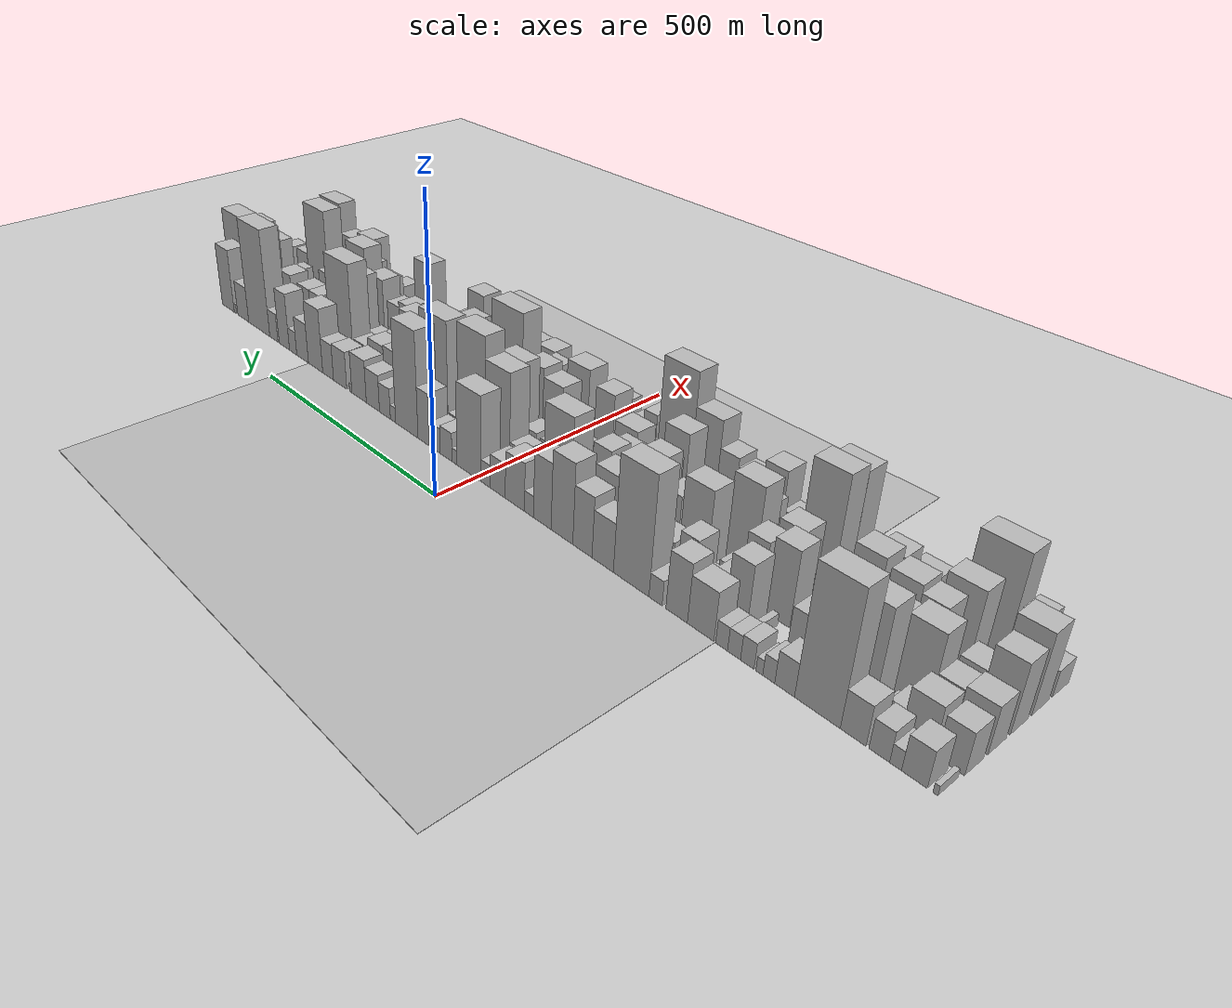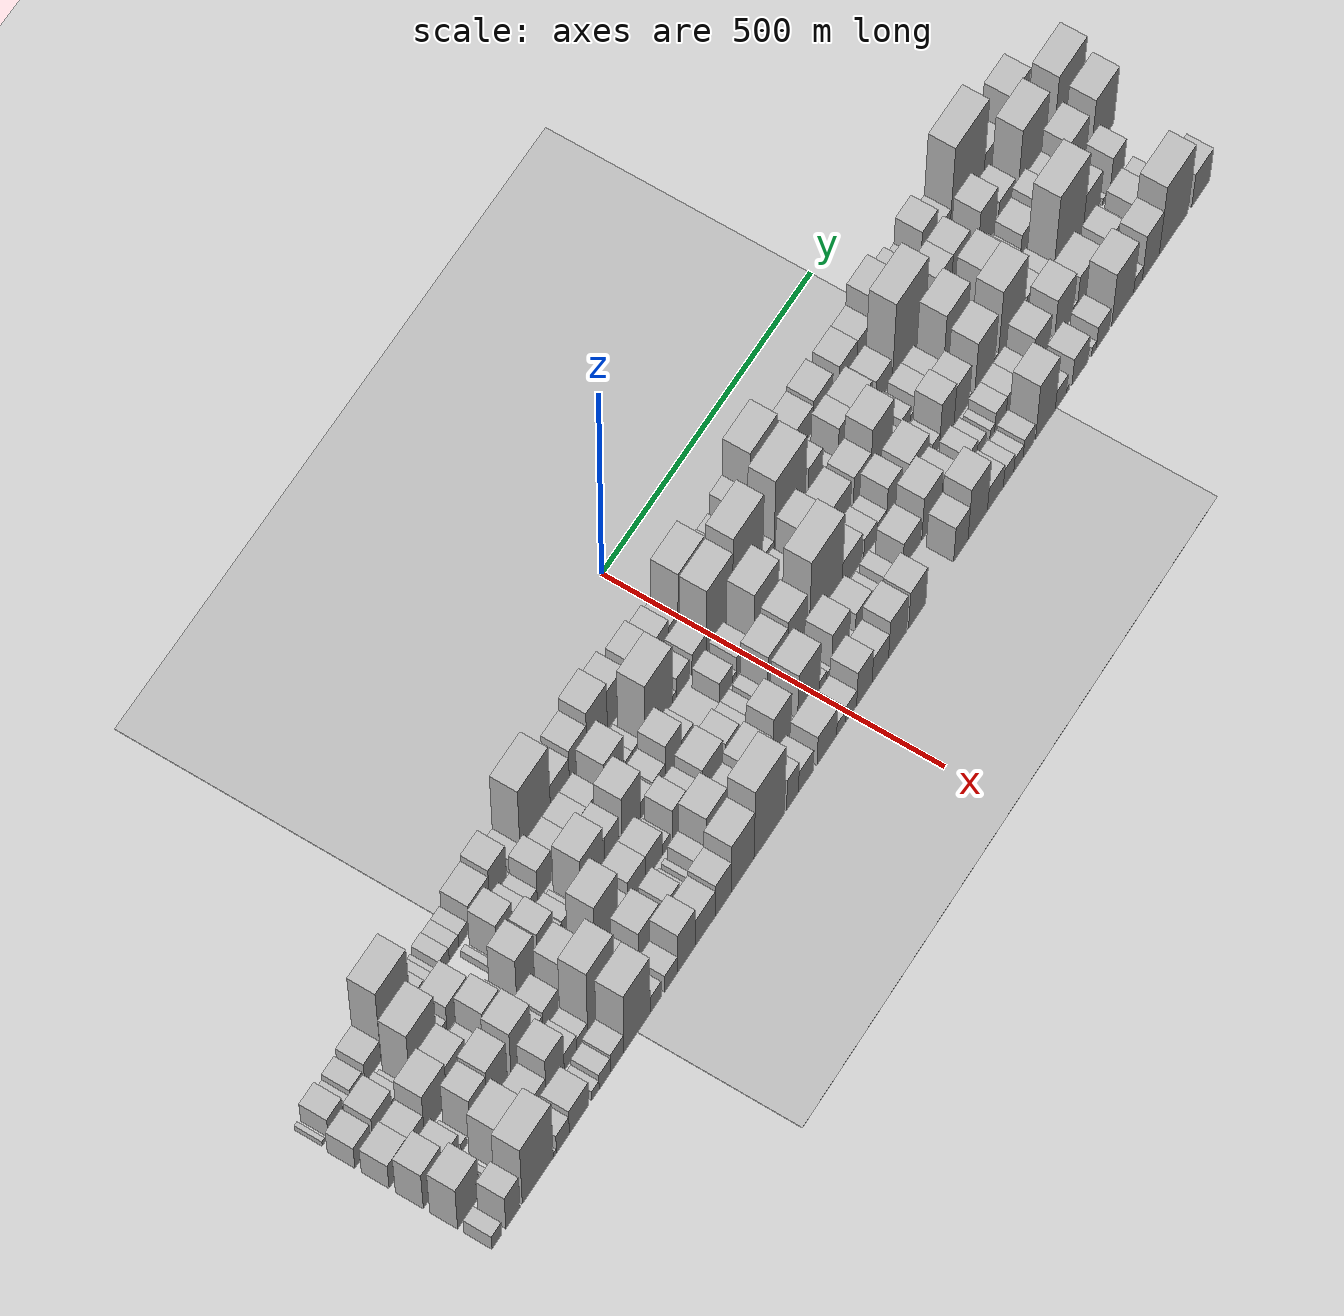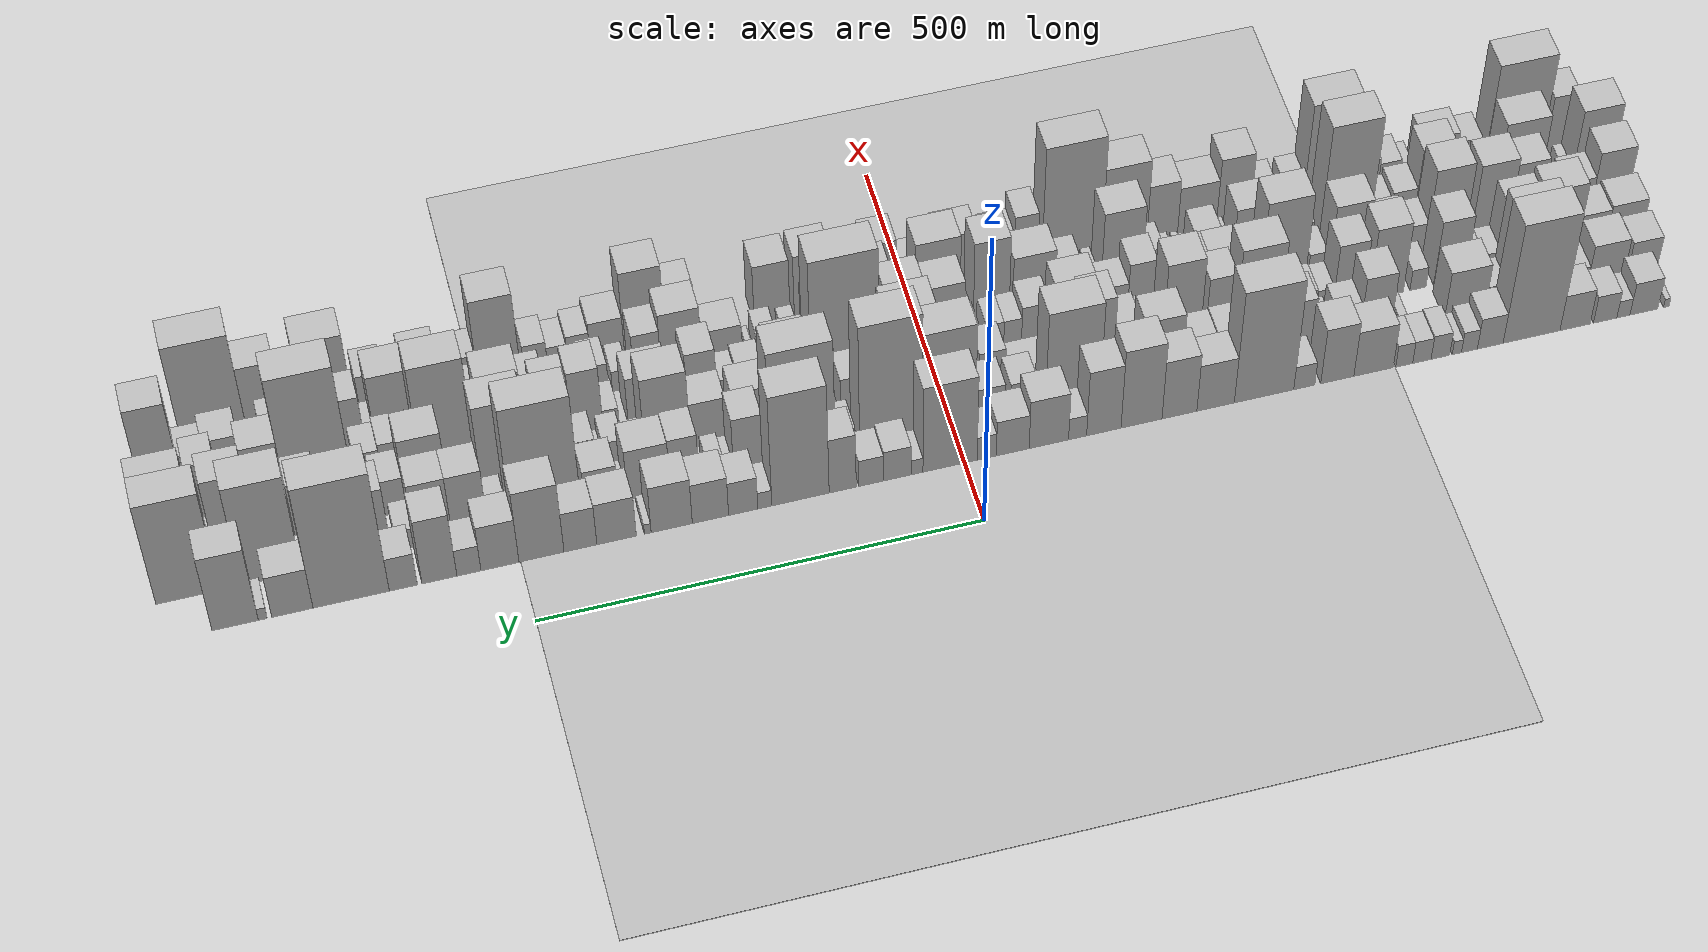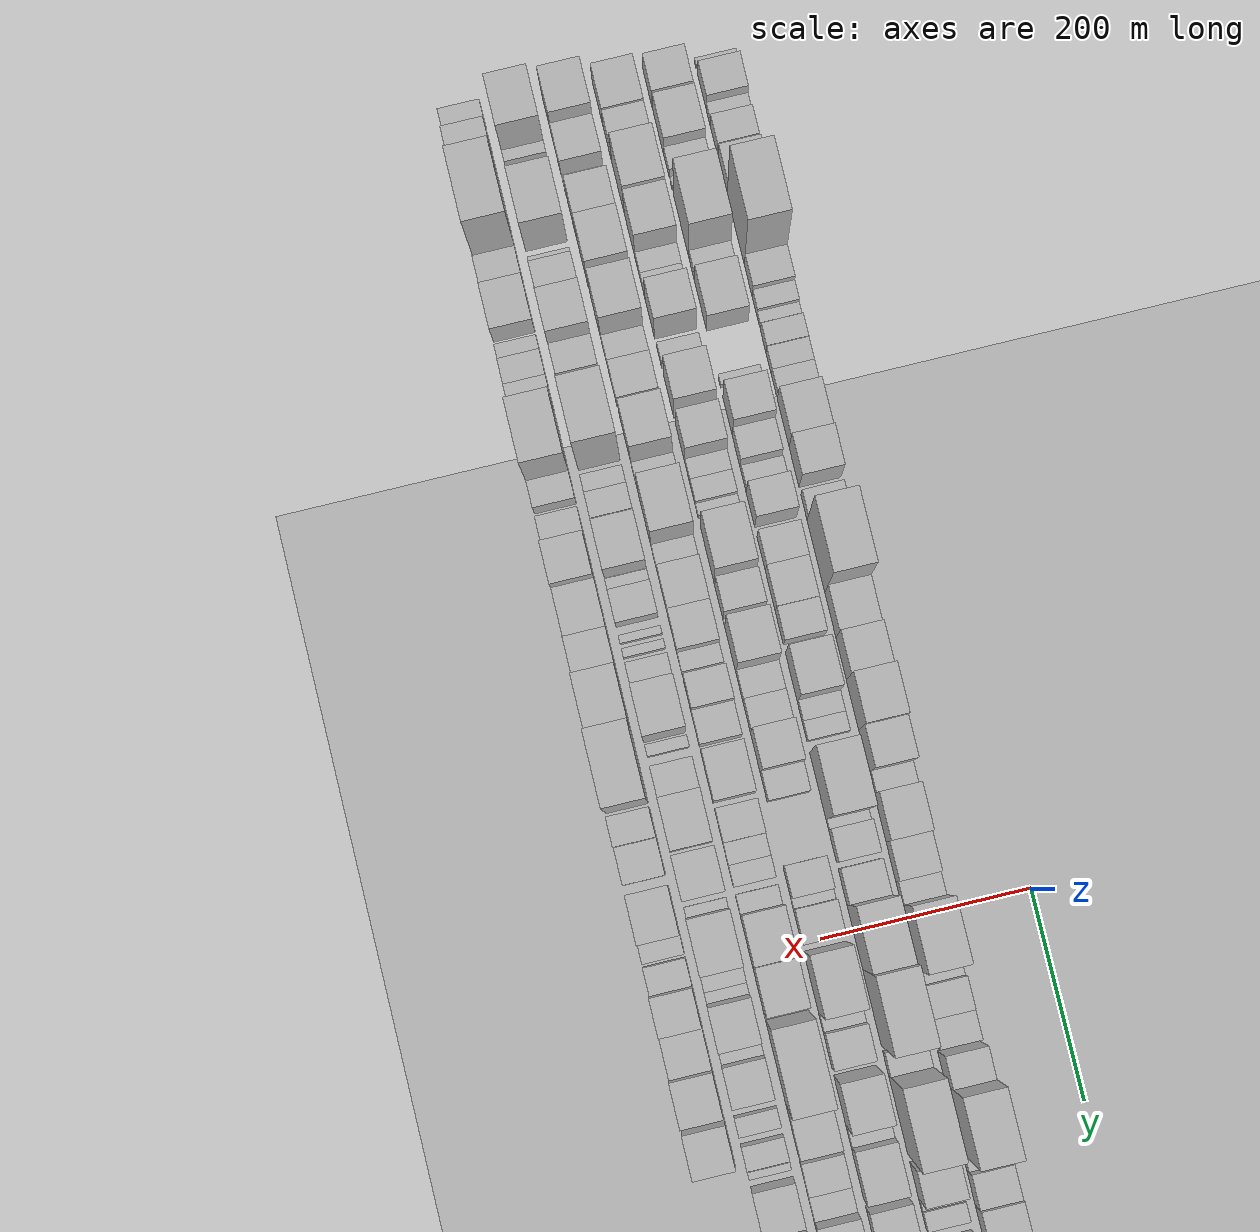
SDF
<?xml version="1.0" encoding="utf-8"?>

<sdf version="1.6">

   <world name="default">

      <gui fullscreen="0">

         <camera name="user_camera">

            <pose>-15 0 4.57585 0 0 0</pose>

            <view_controller>orbit</view_controller>

         </camera>

      </gui>

      <scene>

         <sky>

           <clouds>

             <speed>12</speed>

           </clouds>

         </sky>

         <ambient>0.4 0.4 0.4 1</ambient>

         <background>0.7 0.7 0.7 1</background>

         <shadows>1</shadows>

      </scene>

      <gravity>0 0 -9.8066</gravity>

      <magnetic_field>6e-06 2.3e-05 -4.2e-05</magnetic_field>

      <physics default="0" name="default_physics" type="ode">

         <ode>

            <solver>

               <type>quick</type>

               <iters>10</iters>

               <sor>1.0</sor>

               <use_dynamic_moi_rescaling>0</use_dynamic_moi_rescaling>

            </solver>

            <constraints>

               <cfm>0</cfm>

               <erp>0.2</erp>

               <contact_max_correcting_vel>100</contact_max_correcting_vel>

               <contact_surface_layer>0.001</contact_surface_layer>

            </constraints>

         </ode>

         <max_step_size>0.004</max_step_size>

         <real_time_factor>1</real_time_factor>

         <real_time_update_rate>250</real_time_update_rate>

      </physics>

      <light name="sun" type="directional">

         <cast_shadows>1</cast_shadows>

         <pose>0 0 10 0 0 0</pose>

         <diffuse>0.8 0.8 0.8 1</diffuse>

         <specular>0.2 0.2 0.2 1</specular>

         <attenuation>

            <range>1000</range>

            <constant>0.9</constant>

            <linear>0.01</linear>

            <quadratic>0.001</quadratic>

         </attenuation>

         <direction>-0.5 0.1 -0.9</direction>

      </light>

      <include>

         <name>ground_plane_1</name>

         <uri>model://HANNAS_ground_plane</uri>

         <pose>0 0 0  0 0 0</pose>

      </include>

      <include>

         <name>ground_plane_2</name>

         <uri>model://HANNAS_ground_plane</uri>

         <pose>100 0 0  0 0 0</pose>

      </include>

      <model name="building_1">

         <static>1</static>

         <pose frame="">100.0000 -823.7062 0 0.000000 0.000000 0.000000</pose>

         <link name="link">

            <pose frame="">0 0 7.50 0 0 0</pose>

            <collision name="collision">

               <geometry>

                  <box>

                     <size>40.0000 6.5875 15.0000</size>

                  </box>

               </geometry>

               <max_contacts>10</max_contacts>

               <surface>

                  <contact>

                     <ode/>

                  </contact>

                  <bounce/>

                  <friction>

                     <torsional>

                        <ode/>

                     </torsional>

                     <ode/>

                  </friction>

               </surface>

            </collision>

            <visual name="visual">

               <cast_shadows>0</cast_shadows>

               <geometry>

                  <box>

                     <size>40.0000 6.5875 15.0000</size>

                  </box>

               </geometry>

               <material>

                  <script>

                     <uri>model://HANNAS_wall/materials/scripts</uri>

                     <uri>model://HANNAS_wall/materials/textures</uri>

                     <name>vrc/HANNAS_wall</name>

                  </script>

               </material>

            </visual>

            <self_collide>0</self_collide>

            <enable_wind>0</enable_wind>

            <kinematic>0</kinematic>

         </link>

      </model>

      <model name="building_2">

         <static>1</static>

         <pose frame="">100.0000 -796.6265 0 0.000000 0.000000 0.000000</pose>

         <link name="link">

            <pose frame="">0 0 28.50 0 0 0</pose>

            <collision name="collision">

               <geometry>

                  <box>

                     <size>40.0000 33.5720 57.0000</size>

                  </box>

               </geometry>

               <max_contacts>10</max_contacts>

               <surface>

                  <contact>

                     <ode/>

                  </contact>

                  <bounce/>

                  <friction>

                     <torsional>

                        <ode/>

                     </torsional>

                     <ode/>

                  </friction>

               </surface>

            </collision>

            <visual name="visual">

               <cast_shadows>0</cast_shadows>

               <geometry>

                  <box>

                     <size>40.0000 33.5720 57.0000</size>

                  </box>

               </geometry>

               <material>

                  <script>

                     <uri>model://HANNAS_wall/materials/scripts</uri>

                     <uri>model://HANNAS_wall/materials/textures</uri>

                     <name>vrc/HANNAS_wall</name>

                  </script>

               </material>

            </visual>

            <self_collide>0</self_collide>

            <enable_wind>0</enable_wind>

            <kinematic>0</kinematic>

         </link>

      </model>

      <model name="building_3">

         <static>1</static>

         <pose frame="">100.0000 -771.9704 0 0.000000 0.000000 0.000000</pose>

         <link name="link">

            <pose frame="">0 0 15.00 0 0 0</pose>

            <collision name="collision">

               <geometry>

                  <box>

                     <size>40.0000 15.7402 30.0000</size>

                  </box>

               </geometry>

               <max_contacts>10</max_contacts>

               <surface>

                  <contact>

                     <ode/>

                  </contact>

                  <bounce/>

                  <friction>

                     <torsional>

                        <ode/>

                     </torsional>

                     <ode/>

                  </friction>

               </surface>

            </collision>

            <visual name="visual">

               <cast_shadows>0</cast_shadows>

               <geometry>

                  <box>

                     <size>40.0000 15.7402 30.0000</size>

                  </box>

               </geometry>

               <material>

                  <script>

                     <uri>model://HANNAS_wall/materials/scripts</uri>

                     <uri>model://HANNAS_wall/materials/textures</uri>

                     <name>vrc/HANNAS_wall</name>

                  </script>

               </material>

            </visual>

            <self_collide>0</self_collide>

            <enable_wind>0</enable_wind>

            <kinematic>0</kinematic>

         </link>

      </model>

      <model name="building_4">

         <static>1</static>

         <pose frame="">100.0000 -750.0420 0 0.000000 0.000000 0.000000</pose>

         <link name="link">

            <pose frame="">0 0 24.00 0 0 0</pose>

            <collision name="collision">

               <geometry>

                  <box>

                     <size>40.0000 28.1167 48.0000</size>

                  </box>

               </geometry>

               <max_contacts>10</max_contacts>

               <surface>

                  <contact>

                     <ode/>

                  </contact>

                  <bounce/>

                  <friction>

                     <torsional>

                        <ode/>

                     </torsional>

                     <ode/>

                  </friction>

               </surface>

            </collision>

            <visual name="visual">

               <cast_shadows>0</cast_shadows>

               <geometry>

                  <box>

                     <size>40.0000 28.1167 48.0000</size>

                  </box>

               </geometry>

               <material>

                  <script>

                     <uri>model://HANNAS_wall/materials/scripts</uri>

                     <uri>model://HANNAS_wall/materials/textures</uri>

                     <name>vrc/HANNAS_wall</name>

                  </script>

               </material>

            </visual>

            <self_collide>0</self_collide>

            <enable_wind>0</enable_wind>

            <kinematic>0</kinematic>

         </link>

      </model>

      <model name="building_5">

         <static>1</static>

         <pose frame="">100.0000 -713.9191 0 0.000000 0.000000 0.000000</pose>

         <link name="link">

            <pose frame="">0 0 31.50 0 0 0</pose>

            <collision name="collision">

               <geometry>

                  <box>

                     <size>40.0000 36.1291 63.0000</size>

                  </box>

               </geometry>

               <max_contacts>10</max_contacts>

               <surface>

                  <contact>

                     <ode/>

                  </contact>

                  <bounce/>

                  <friction>

                     <torsional>

                        <ode/>

                     </torsional>

                     <ode/>

                  </friction>

               </surface>

            </collision>

            <visual name="visual">

               <cast_shadows>0</cast_shadows>

               <geometry>

                  <box>

                     <size>40.0000 36.1291 63.0000</size>

                  </box>

               </geometry>

               <material>

                  <script>

                     <uri>model://HANNAS_wall/materials/scripts</uri>

                     <uri>model://HANNAS_wall/materials/textures</uri>

                     <name>vrc/HANNAS_wall</name>

                  </script>

               </material>

            </visual>

            <self_collide>0</self_collide>

            <enable_wind>0</enable_wind>

            <kinematic>0</kinematic>

         </link>

      </model>

      <model name="building_6">

         <static>1</static>

         <pose frame="">100.0000 -661.9510 0 0.000000 0.000000 0.000000</pose>

         <link name="link">

            <pose frame="">0 0 106.50 0 0 0</pose>

            <collision name="collision">

               <geometry>

                  <box>

                     <size>40.0000 67.8070 213.0000</size>

                  </box>

               </geometry>

               <max_contacts>10</max_contacts>

               <surface>

                  <contact>

                     <ode/>

                  </contact>

                  <bounce/>

                  <friction>

                     <torsional>

                        <ode/>

                     </torsional>

                     <ode/>

                  </friction>

               </surface>

            </collision>

            <visual name="visual">

               <cast_shadows>0</cast_shadows>

               <geometry>

                  <box>

                     <size>40.0000 67.8070 213.0000</size>

                  </box>

               </geometry>

               <material>

                  <script>

                     <uri>model://HANNAS_wall/materials/scripts</uri>

                     <uri>model://HANNAS_wall/materials/textures</uri>

                     <name>vrc/HANNAS_wall</name>

                  </script>

               </material>

            </visual>

            <self_collide>0</self_collide>

            <enable_wind>0</enable_wind>

            <kinematic>0</kinematic>

         </link>

      </model>

      <model name="building_7">

         <static>1</static>

         <pose frame="">100.0000 -612.7542 0 0.000000 0.000000 0.000000</pose>

         <link name="link">

            <pose frame="">0 0 27.00 0 0 0</pose>

            <collision name="collision">

               <geometry>

                  <box>

                     <size>40.0000 30.5866 54.0000</size>

                  </box>

               </geometry>

               <max_contacts>10</max_contacts>

               <surface>

                  <contact>

                     <ode/>

                  </contact>

                  <bounce/>

                  <friction>

                     <torsional>

                        <ode/>

                     </torsional>

                     <ode/>

                  </friction>

               </surface>

            </collision>

            <visual name="visual">

               <cast_shadows>0</cast_shadows>

               <geometry>

                  <box>

                     <size>40.0000 30.5866 54.0000</size>

                  </box>

               </geometry>

               <material>

                  <script>

                     <uri>model://HANNAS_wall/materials/scripts</uri>

                     <uri>model://HANNAS_wall/materials/textures</uri>

                     <name>vrc/HANNAS_wall</name>

                  </script>

               </material>

            </visual>

            <self_collide>0</self_collide>

            <enable_wind>0</enable_wind>

            <kinematic>0</kinematic>

         </link>

      </model>

      <model name="building_8">

         <static>1</static>

         <pose frame="">100.0000 -588.0080 0 0.000000 0.000000 0.000000</pose>

         <link name="link">

            <pose frame="">0 0 18.00 0 0 0</pose>

            <collision name="collision">

               <geometry>

                  <box>

                     <size>40.0000 18.9059 36.0000</size>

                  </box>

               </geometry>

               <max_contacts>10</max_contacts>

               <surface>

                  <contact>

                     <ode/>

                  </contact>

                  <bounce/>

                  <friction>

                     <torsional>

                        <ode/>

                     </torsional>

                     <ode/>

                  </friction>

               </surface>

            </collision>

            <visual name="visual">

               <cast_shadows>0</cast_shadows>

               <geometry>

                  <box>

                     <size>40.0000 18.9059 36.0000</size>

                  </box>

               </geometry>

               <material>

                  <script>

                     <uri>model://HANNAS_wall/materials/scripts</uri>

                     <uri>model://HANNAS_wall/materials/textures</uri>

                     <name>vrc/HANNAS_wall</name>

                  </script>

               </material>

            </visual>

            <self_collide>0</self_collide>

            <enable_wind>0</enable_wind>

            <kinematic>0</kinematic>

         </link>

      </model>

      <model name="building_9">

         <static>1</static>

         <pose frame="">100.0000 -573.0209 0 0.000000 0.000000 0.000000</pose>

         <link name="link">

            <pose frame="">0 0 12.00 0 0 0</pose>

            <collision name="collision">

               <geometry>

                  <box>

                     <size>40.0000 11.0684 24.0000</size>

                  </box>

               </geometry>

               <max_contacts>10</max_contacts>

               <surface>

                  <contact>

                     <ode/>

                  </contact>

                  <bounce/>

                  <friction>

                     <torsional>

                        <ode/>

                     </torsional>

                     <ode/>

                  </friction>

               </surface>

            </collision>

            <visual name="visual">

               <cast_shadows>0</cast_shadows>

               <geometry>

                  <box>

                     <size>40.0000 11.0684 24.0000</size>

                  </box>

               </geometry>

               <material>

                  <script>

                     <uri>model://HANNAS_wall/materials/scripts</uri>

                     <uri>model://HANNAS_wall/materials/textures</uri>

                     <name>vrc/HANNAS_wall</name>

                  </script>

               </material>

            </visual>

            <self_collide>0</self_collide>

            <enable_wind>0</enable_wind>

            <kinematic>0</kinematic>

         </link>

      </model>

      <model name="building_10">

         <static>1</static>

         <pose frame="">100.0000 -553.4722 0 0.000000 0.000000 0.000000</pose>

         <link name="link">

            <pose frame="">0 0 21.00 0 0 0</pose>

            <collision name="collision">

               <geometry>

                  <box>

                     <size>40.0000 22.0288 42.0000</size>

                  </box>

               </geometry>

               <max_contacts>10</max_contacts>

               <surface>

                  <contact>

                     <ode/>

                  </contact>

                  <bounce/>

                  <friction>

                     <torsional>

                        <ode/>

                     </torsional>

                     <ode/>

                  </friction>

               </surface>

            </collision>

            <visual name="visual">

               <cast_shadows>0</cast_shadows>

               <geometry>

                  <box>

                     <size>40.0000 22.0288 42.0000</size>

                  </box>

               </geometry>

               <material>

                  <script>

                     <uri>model://HANNAS_wall/materials/scripts</uri>

                     <uri>model://HANNAS_wall/materials/textures</uri>

                     <name>vrc/HANNAS_wall</name>

                  </script>

               </material>

            </visual>

            <self_collide>0</self_collide>

            <enable_wind>0</enable_wind>

            <kinematic>0</kinematic>

         </link>

      </model>

      <model name="building_11">

         <static>1</static>

         <pose frame="">100.0000 -531.5921 0 0.000000 0.000000 0.000000</pose>

         <link name="link">

            <pose frame="">0 0 19.50 0 0 0</pose>

            <collision name="collision">

               <geometry>

                  <box>

                     <size>40.0000 21.7315 39.0000</size>

                  </box>

               </geometry>

               <max_contacts>10</max_contacts>

               <surface>

                  <contact>

                     <ode/>

                  </contact>

                  <bounce/>

                  <friction>

                     <torsional>

                        <ode/>

                     </torsional>

                     <ode/>

                  </friction>

               </surface>

            </collision>

            <visual name="visual">

               <cast_shadows>0</cast_shadows>

               <geometry>

                  <box>

                     <size>40.0000 21.7315 39.0000</size>

                  </box>

               </geometry>

               <material>

                  <script>

                     <uri>model://HANNAS_wall/materials/scripts</uri>

                     <uri>model://HANNAS_wall/materials/textures</uri>

                     <name>vrc/HANNAS_wall</name>

                  </script>

               </material>

            </visual>

            <self_collide>0</self_collide>

            <enable_wind>0</enable_wind>

            <kinematic>0</kinematic>

         </link>

      </model>

      <model name="building_12">

         <static>1</static>

         <pose frame="">100.0000 -510.6498 0 0.000000 0.000000 0.000000</pose>

         <link name="link">

            <pose frame="">0 0 19.50 0 0 0</pose>

            <collision name="collision">

               <geometry>

                  <box>

                     <size>40.0000 20.1530 39.0000</size>

                  </box>

               </geometry>

               <max_contacts>10</max_contacts>

               <surface>

                  <contact>

                     <ode/>

                  </contact>

                  <bounce/>

                  <friction>

                     <torsional>

                        <ode/>

                     </torsional>

                     <ode/>

                  </friction>

               </surface>

            </collision>

            <visual name="visual">

               <cast_shadows>0</cast_shadows>

               <geometry>

                  <box>

                     <size>40.0000 20.1530 39.0000</size>

                  </box>

               </geometry>

               <material>

                  <script>

                     <uri>model://HANNAS_wall/materials/scripts</uri>

                     <uri>model://HANNAS_wall/materials/textures</uri>

                     <name>vrc/HANNAS_wall</name>

                  </script>

               </material>

            </visual>

            <self_collide>0</self_collide>

            <enable_wind>0</enable_wind>

            <kinematic>0</kinematic>

         </link>

      </model>

      <model name="building_13">

         <static>1</static>

         <pose frame="">100.0000 -474.3793 0 0.000000 0.000000 0.000000</pose>

         <link name="link">

            <pose frame="">0 0 40.50 0 0 0</pose>

            <collision name="collision">

               <geometry>

                  <box>

                     <size>40.0000 46.3880 81.0000</size>

                  </box>

               </geometry>

               <max_contacts>10</max_contacts>

               <surface>

                  <contact>

                     <ode/>

                  </contact>

                  <bounce/>

                  <friction>

                     <torsional>

                        <ode/>

                     </torsional>

                     <ode/>

                  </friction>

               </surface>

            </collision>

            <visual name="visual">

               <cast_shadows>0</cast_shadows>

               <geometry>

                  <box>

                     <size>40.0000 46.3880 81.0000</size>

                  </box>

               </geometry>

               <material>

                  <script>

                     <uri>model://HANNAS_wall/materials/scripts</uri>

                     <uri>model://HANNAS_wall/materials/textures</uri>

                     <name>vrc/HANNAS_wall</name>

                  </script>

               </material>

            </visual>

            <self_collide>0</self_collide>

            <enable_wind>0</enable_wind>

            <kinematic>0</kinematic>

         </link>

      </model>

      <model name="building_14">

         <static>1</static>

         <pose frame="">100.0000 -431.7051 0 0.000000 0.000000 0.000000</pose>

         <link name="link">

            <pose frame="">0 0 49.50 0 0 0</pose>

            <collision name="collision">

               <geometry>

                  <box>

                     <size>40.0000 38.9603 99.0000</size>

                  </box>

               </geometry>

               <max_contacts>10</max_contacts>

               <surface>

                  <contact>

                     <ode/>

                  </contact>

                  <bounce/>

                  <friction>

                     <torsional>

                        <ode/>

                     </torsional>

                     <ode/>

                  </friction>

               </surface>

            </collision>

            <visual name="visual">

               <cast_shadows>0</cast_shadows>

               <geometry>

                  <box>

                     <size>40.0000 38.9603 99.0000</size>

                  </box>

               </geometry>

               <material>

                  <script>

                     <uri>model://HANNAS_wall/materials/scripts</uri>

                     <uri>model://HANNAS_wall/materials/textures</uri>

                     <name>vrc/HANNAS_wall</name>

                  </script>

               </material>

            </visual>

            <self_collide>0</self_collide>

            <enable_wind>0</enable_wind>

            <kinematic>0</kinematic>

         </link>

      </model>

      <model name="building_15">

         <static>1</static>

         <pose frame="">100.0000 -392.8743 0 0.000000 0.000000 0.000000</pose>

         <link name="link">

            <pose frame="">0 0 21.00 0 0 0</pose>

            <collision name="collision">

               <geometry>

                  <box>

                     <size>40.0000 24.7014 42.0000</size>

                  </box>

               </geometry>

               <max_contacts>10</max_contacts>

               <surface>

                  <contact>

                     <ode/>

                  </contact>

                  <bounce/>

                  <friction>

                     <torsional>

                        <ode/>

                     </torsional>

                     <ode/>

                  </friction>

               </surface>

            </collision>

            <visual name="visual">

               <cast_shadows>0</cast_shadows>

               <geometry>

                  <box>

                     <size>40.0000 24.7014 42.0000</size>

                  </box>

               </geometry>

               <material>

                  <script>

                     <uri>model://HANNAS_wall/materials/scripts</uri>

                     <uri>model://HANNAS_wall/materials/textures</uri>

                     <name>vrc/HANNAS_wall</name>

                  </script>

               </material>

            </visual>

            <self_collide>0</self_collide>

            <enable_wind>0</enable_wind>

            <kinematic>0</kinematic>

         </link>

      </model>

      <model name="building_16">

         <static>1</static>

         <pose frame="">100.0000 -345.8023 0 0.000000 0.000000 0.000000</pose>

         <link name="link">

            <pose frame="">0 0 100.50 0 0 0</pose>

            <collision name="collision">

               <geometry>

                  <box>

                     <size>40.0000 69.4425 201.0000</size>

                  </box>

               </geometry>

               <max_contacts>10</max_contacts>

               <surface>

                  <contact>

                     <ode/>

                  </contact>

                  <bounce/>

                  <friction>

                     <torsional>

                        <ode/>

                     </torsional>

                     <ode/>

                  </friction>

               </surface>

            </collision>

            <visual name="visual">

               <cast_shadows>0</cast_shadows>

               <geometry>

                  <box>

                     <size>40.0000 69.4425 201.0000</size>

                  </box>

               </geometry>

               <material>

                  <script>

                     <uri>model://HANNAS_wall/materials/scripts</uri>

                     <uri>model://HANNAS_wall/materials/textures</uri>

                     <name>vrc/HANNAS_wall</name>

                  </script>

               </material>

            </visual>

            <self_collide>0</self_collide>

            <enable_wind>0</enable_wind>

            <kinematic>0</kinematic>

         </link>

      </model>

      <model name="building_17">

         <static>1</static>

         <pose frame="">100.0000 -289.2329 0 0.000000 0.000000 0.000000</pose>

         <link name="link">

            <pose frame="">0 0 42.00 0 0 0</pose>

            <collision name="collision">

               <geometry>

                  <box>

                     <size>40.0000 43.6964 84.0000</size>

                  </box>

               </geometry>

               <max_contacts>10</max_contacts>

               <surface>

                  <contact>

                     <ode/>

                  </contact>

                  <bounce/>

                  <friction>

                     <torsional>

                        <ode/>

                     </torsional>

                     <ode/>

                  </friction>

               </surface>

            </collision>

            <visual name="visual">

               <cast_shadows>0</cast_shadows>

               <geometry>

                  <box>

                     <size>40.0000 43.6964 84.0000</size>

                  </box>

               </geometry>

               <material>

                  <script>

                     <uri>model://HANNAS_wall/materials/scripts</uri>

                     <uri>model://HANNAS_wall/materials/textures</uri>

                     <name>vrc/HANNAS_wall</name>

                  </script>

               </material>

            </visual>

            <self_collide>0</self_collide>

            <enable_wind>0</enable_wind>

            <kinematic>0</kinematic>

         </link>

      </model>

      <model name="building_18">

         <static>1</static>

         <pose frame="">100.0000 -247.1147 0 0.000000 0.000000 0.000000</pose>

         <link name="link">

            <pose frame="">0 0 52.50 0 0 0</pose>

            <collision name="collision">

               <geometry>

                  <box>

                     <size>40.0000 40.5399 105.0000</size>

                  </box>

               </geometry>

               <max_contacts>10</max_contacts>

               <surface>

                  <contact>

                     <ode/>

                  </contact>

                  <bounce/>

                  <friction>

                     <torsional>

                        <ode/>

                     </torsional>

                     <ode/>

                  </friction>

               </surface>

            </collision>

            <visual name="visual">

               <cast_shadows>0</cast_shadows>

               <geometry>

                  <box>

                     <size>40.0000 40.5399 105.0000</size>

                  </box>

               </geometry>

               <material>

                  <script>

                     <uri>model://HANNAS_wall/materials/scripts</uri>

                     <uri>model://HANNAS_wall/materials/textures</uri>

                     <name>vrc/HANNAS_wall</name>

                  </script>

               </material>

            </visual>

            <self_collide>0</self_collide>

            <enable_wind>0</enable_wind>

            <kinematic>0</kinematic>

         </link>

      </model>

      <model name="building_19">

         <static>1</static>

         <pose frame="">100.0000 -203.0991 0 0.000000 0.000000 0.000000</pose>

         <link name="link">

            <pose frame="">0 0 70.50 0 0 0</pose>

            <collision name="collision">

               <geometry>

                  <box>

                     <size>40.0000 47.4914 141.0000</size>

                  </box>

               </geometry>

               <max_contacts>10</max_contacts>

               <surface>

                  <contact>

                     <ode/>

                  </contact>

                  <bounce/>

                  <friction>

                     <torsional>

                        <ode/>

                     </torsional>

                     <ode/>

                  </friction>

               </surface>

            </collision>

            <visual name="visual">

               <cast_shadows>0</cast_shadows>

               <geometry>

                  <box>

                     <size>40.0000 47.4914 141.0000</size>

                  </box>

               </geometry>

               <material>

                  <script>

                     <uri>model://HANNAS_wall/materials/scripts</uri>

                     <uri>model://HANNAS_wall/materials/textures</uri>

                     <name>vrc/HANNAS_wall</name>

                  </script>

               </material>

            </visual>

            <self_collide>0</self_collide>

            <enable_wind>0</enable_wind>

            <kinematic>0</kinematic>

         </link>

      </model>

      <model name="building_20">

         <static>1</static>

         <pose frame="">100.0000 -159.4786 0 0.000000 0.000000 0.000000</pose>

         <link name="link">

            <pose frame="">0 0 58.50 0 0 0</pose>

            <collision name="collision">

               <geometry>

                  <box>

                     <size>40.0000 39.7496 117.0000</size>

                  </box>

               </geometry>

               <max_contacts>10</max_contacts>

               <surface>

                  <contact>

                     <ode/>

                  </contact>

                  <bounce/>

                  <friction>

                     <torsional>

                        <ode/>

                     </torsional>

                     <ode/>

                  </friction>

               </surface>

            </collision>

            <visual name="visual">

               <cast_shadows>0</cast_shadows>

               <geometry>

                  <box>

                     <size>40.0000 39.7496 117.0000</size>

                  </box>

               </geometry>

               <material>

                  <script>

                     <uri>model://HANNAS_wall/materials/scripts</uri>

                     <uri>model://HANNAS_wall/materials/textures</uri>

                     <name>vrc/HANNAS_wall</name>

                  </script>

               </material>

            </visual>

            <self_collide>0</self_collide>

            <enable_wind>0</enable_wind>

            <kinematic>0</kinematic>

         </link>

      </model>

      <model name="building_21">

         <static>1</static>

         <pose frame="">100.0000 -129.1754 0 0.000000 0.000000 0.000000</pose>

         <link name="link">

            <pose frame="">0 0 19.50 0 0 0</pose>

            <collision name="collision">

               <geometry>

                  <box>

                     <size>40.0000 20.8567 39.0000</size>

                  </box>

               </geometry>

               <max_contacts>10</max_contacts>

               <surface>

                  <contact>

                     <ode/>

                  </contact>

                  <bounce/>

                  <friction>

                     <torsional>

                        <ode/>

                     </torsional>

                     <ode/>

                  </friction>

               </surface>

            </collision>

            <visual name="visual">

               <cast_shadows>0</cast_shadows>

               <geometry>

                  <box>

                     <size>40.0000 20.8567 39.0000</size>

                  </box>

               </geometry>

               <material>

                  <script>

                     <uri>model://HANNAS_wall/materials/scripts</uri>

                     <uri>model://HANNAS_wall/materials/textures</uri>

                     <name>vrc/HANNAS_wall</name>

                  </script>

               </material>

            </visual>

            <self_collide>0</self_collide>

            <enable_wind>0</enable_wind>

            <kinematic>0</kinematic>

         </link>

      </model>

      <model name="building_22">

         <static>1</static>

         <pose frame="">100.0000 -96.0794 0 0.000000 0.000000 0.000000</pose>

         <link name="link">

            <pose frame="">0 0 43.50 0 0 0</pose>

            <collision name="collision">

               <geometry>

                  <box>

                     <size>40.0000 45.3353 87.0000</size>

                  </box>

               </geometry>

               <max_contacts>10</max_contacts>

               <surface>

                  <contact>

                     <ode/>

                  </contact>

                  <bounce/>

                  <friction>

                     <torsional>

                        <ode/>

                     </torsional>

                     <ode/>

                  </friction>

               </surface>

            </collision>

            <visual name="visual">

               <cast_shadows>0</cast_shadows>

               <geometry>

                  <box>

                     <size>40.0000 45.3353 87.0000</size>

                  </box>

               </geometry>

               <material>

                  <script>

                     <uri>model://HANNAS_wall/materials/scripts</uri>

                     <uri>model://HANNAS_wall/materials/textures</uri>

                     <name>vrc/HANNAS_wall</name>

                  </script>

               </material>

            </visual>

            <self_collide>0</self_collide>

            <enable_wind>0</enable_wind>

            <kinematic>0</kinematic>

         </link>

      </model>

      <model name="building_23">

         <static>1</static>

         <pose frame="">100.0000 -54.5835 0 0.000000 0.000000 0.000000</pose>

         <link name="link">

            <pose frame="">0 0 31.50 0 0 0</pose>

            <collision name="collision">

               <geometry>

                  <box>

                     <size>40.0000 37.6564 63.0000</size>

                  </box>

               </geometry>

               <max_contacts>10</max_contacts>

               <surface>

                  <contact>

                     <ode/>

                  </contact>

                  <bounce/>

                  <friction>

                     <torsional>

                        <ode/>

                     </torsional>

                     <ode/>

                  </friction>

               </surface>

            </collision>

            <visual name="visual">

               <cast_shadows>0</cast_shadows>

               <geometry>

                  <box>

                     <size>40.0000 37.6564 63.0000</size>

                  </box>

               </geometry>

               <material>

                  <script>

                     <uri>model://HANNAS_wall/materials/scripts</uri>

                     <uri>model://HANNAS_wall/materials/textures</uri>

                     <name>vrc/HANNAS_wall</name>

                  </script>

               </material>

            </visual>

            <self_collide>0</self_collide>

            <enable_wind>0</enable_wind>

            <kinematic>0</kinematic>

         </link>

      </model>

      <model name="building_24">

         <static>1</static>

         <pose frame="">100.0000 -24.7409 0 0.000000 0.000000 0.000000</pose>

         <link name="link">

            <pose frame="">0 0 21.00 0 0 0</pose>

            <collision name="collision">

               <geometry>

                  <box>

                     <size>40.0000 22.0289 42.0000</size>

                  </box>

               </geometry>

               <max_contacts>10</max_contacts>

               <surface>

                  <contact>

                     <ode/>

                  </contact>

                  <bounce/>

                  <friction>

                     <torsional>

                        <ode/>

                     </torsional>

                     <ode/>

                  </friction>

               </surface>

            </collision>

            <visual name="visual">

               <cast_shadows>0</cast_shadows>

               <geometry>

                  <box>

                     <size>40.0000 22.0289 42.0000</size>

                  </box>

               </geometry>

               <material>

                  <script>

                     <uri>model://HANNAS_wall/materials/scripts</uri>

                     <uri>model://HANNAS_wall/materials/textures</uri>

                     <name>vrc/HANNAS_wall</name>

                  </script>

               </material>

            </visual>

            <self_collide>0</self_collide>

            <enable_wind>0</enable_wind>

            <kinematic>0</kinematic>

         </link>

      </model>

      <model name="building_25">

         <static>1</static>

         <pose frame="">100.0000 17.2089 0 0.000000 0.000000 0.000000</pose>

         <link name="link">

            <pose frame="">0 0 78.00 0 0 0</pose>

            <collision name="collision">

               <geometry>

                  <box>

                     <size>40.0000 61.8706 156.0000</size>

                  </box>

               </geometry>

               <max_contacts>10</max_contacts>

               <surface>

                  <contact>

                     <ode/>

                  </contact>

                  <bounce/>

                  <friction>

                     <torsional>

                        <ode/>

                     </torsional>

                     <ode/>

                  </friction>

               </surface>

            </collision>

            <visual name="visual">

               <cast_shadows>0</cast_shadows>

               <geometry>

                  <box>

                     <size>40.0000 61.8706 156.0000</size>

                  </box>

               </geometry>

               <material>

                  <script>

                     <uri>model://HANNAS_wall/materials/scripts</uri>

                     <uri>model://HANNAS_wall/materials/textures</uri>

                     <name>vrc/HANNAS_wall</name>

                  </script>

               </material>

            </visual>

            <self_collide>0</self_collide>

            <enable_wind>0</enable_wind>

            <kinematic>0</kinematic>

         </link>

      </model>

      <model name="building_26">

         <static>1</static>

         <pose frame="">100.0000 54.8192 0 0.000000 0.000000 0.000000</pose>

         <link name="link">

            <pose frame="">0 0 13.50 0 0 0</pose>

            <collision name="collision">

               <geometry>

                  <box>

                     <size>40.0000 13.3501 27.0000</size>

                  </box>

               </geometry>

               <max_contacts>10</max_contacts>

               <surface>

                  <contact>

                     <ode/>

                  </contact>

                  <bounce/>

                  <friction>

                     <torsional>

                        <ode/>

                     </torsional>

                     <ode/>

                  </friction>

               </surface>

            </collision>

            <visual name="visual">

               <cast_shadows>0</cast_shadows>

               <geometry>

                  <box>

                     <size>40.0000 13.3501 27.0000</size>

                  </box>

               </geometry>

               <material>

                  <script>

                     <uri>model://HANNAS_wall/materials/scripts</uri>

                     <uri>model://HANNAS_wall/materials/textures</uri>

                     <name>vrc/HANNAS_wall</name>

                  </script>

               </material>

            </visual>

            <self_collide>0</self_collide>

            <enable_wind>0</enable_wind>

            <kinematic>0</kinematic>

         </link>

      </model>

      <model name="building_27">

         <static>1</static>

         <pose frame="">100.0000 77.1365 0 0.000000 0.000000 0.000000</pose>

         <link name="link">

            <pose frame="">0 0 27.00 0 0 0</pose>

            <collision name="collision">

               <geometry>

                  <box>

                     <size>40.0000 31.2846 54.0000</size>

                  </box>

               </geometry>

               <max_contacts>10</max_contacts>

               <surface>

                  <contact>

                     <ode/>

                  </contact>

                  <bounce/>

                  <friction>

                     <torsional>

                        <ode/>

                     </torsional>

                     <ode/>

                  </friction>

               </surface>

            </collision>

            <visual name="visual">

               <cast_shadows>0</cast_shadows>

               <geometry>

                  <box>

                     <size>40.0000 31.2846 54.0000</size>

                  </box>

               </geometry>

               <material>

                  <script>

                     <uri>model://HANNAS_wall/materials/scripts</uri>

                     <uri>model://HANNAS_wall/materials/textures</uri>

                     <name>vrc/HANNAS_wall</name>

                  </script>

               </material>

            </visual>

            <self_collide>0</self_collide>

            <enable_wind>0</enable_wind>

            <kinematic>0</kinematic>

         </link>

      </model>

      <model name="building_28">

         <static>1</static>

         <pose frame="">100.0000 106.9000 0 0.000000 0.000000 0.000000</pose>

         <link name="link">

            <pose frame="">0 0 24.00 0 0 0</pose>

            <collision name="collision">

               <geometry>

                  <box>

                     <size>40.0000 28.2425 48.0000</size>

                  </box>

               </geometry>

               <max_contacts>10</max_contacts>

               <surface>

                  <contact>

                     <ode/>

                  </contact>

                  <bounce/>

                  <friction>

                     <torsional>

                        <ode/>

                     </torsional>

                     <ode/>

                  </friction>

               </surface>

            </collision>

            <visual name="visual">

               <cast_shadows>0</cast_shadows>

               <geometry>

                  <box>

                     <size>40.0000 28.2425 48.0000</size>

                  </box>

               </geometry>

               <material>

                  <script>

                     <uri>model://HANNAS_wall/materials/scripts</uri>

                     <uri>model://HANNAS_wall/materials/textures</uri>

                     <name>vrc/HANNAS_wall</name>

                  </script>

               </material>

            </visual>

            <self_collide>0</self_collide>

            <enable_wind>0</enable_wind>

            <kinematic>0</kinematic>

         </link>

      </model>

      <model name="building_29">

         <static>1</static>

         <pose frame="">100.0000 139.3594 0 0.000000 0.000000 0.000000</pose>

         <link name="link">

            <pose frame="">0 0 49.50 0 0 0</pose>

            <collision name="collision">

               <geometry>

                  <box>

                     <size>40.0000 30.6763 99.0000</size>

                  </box>

               </geometry>

               <max_contacts>10</max_contacts>

               <surface>

                  <contact>

                     <ode/>

                  </contact>

                  <bounce/>

                  <friction>

                     <torsional>

                        <ode/>

                     </torsional>

                     <ode/>

                  </friction>

               </surface>

            </collision>

            <visual name="visual">

               <cast_shadows>0</cast_shadows>

               <geometry>

                  <box>

                     <size>40.0000 30.6763 99.0000</size>

                  </box>

               </geometry>

               <material>

                  <script>

                     <uri>model://HANNAS_wall/materials/scripts</uri>

                     <uri>model://HANNAS_wall/materials/textures</uri>

                     <name>vrc/HANNAS_wall</name>

                  </script>

               </material>

            </visual>

            <self_collide>0</self_collide>

            <enable_wind>0</enable_wind>

            <kinematic>0</kinematic>

         </link>

      </model>

      <model name="building_30">

         <static>1</static>

         <pose frame="">100.0000 187.0730 0 0.000000 0.000000 0.000000</pose>

         <link name="link">

            <pose frame="">0 0 100.50 0 0 0</pose>

            <collision name="collision">

               <geometry>

                  <box>

                     <size>40.0000 64.7509 201.0000</size>

                  </box>

               </geometry>

               <max_contacts>10</max_contacts>

               <surface>

                  <contact>

                     <ode/>

                  </contact>

                  <bounce/>

                  <friction>

                     <torsional>

                        <ode/>

                     </torsional>

                     <ode/>

                  </friction>

               </surface>

            </collision>

            <visual name="visual">

               <cast_shadows>0</cast_shadows>

               <geometry>

                  <box>

                     <size>40.0000 64.7509 201.0000</size>

                  </box>

               </geometry>

               <material>

                  <script>

                     <uri>model://HANNAS_wall/materials/scripts</uri>

                     <uri>model://HANNAS_wall/materials/textures</uri>

                     <name>vrc/HANNAS_wall</name>

                  </script>

               </material>

            </visual>

            <self_collide>0</self_collide>

            <enable_wind>0</enable_wind>

            <kinematic>0</kinematic>

         </link>

      </model>

      <model name="building_31">

         <static>1</static>

         <pose frame="">100.0000 227.3169 0 0.000000 0.000000 0.000000</pose>

         <link name="link">

            <pose frame="">0 0 15.00 0 0 0</pose>

            <collision name="collision">

               <geometry>

                  <box>

                     <size>40.0000 15.7369 30.0000</size>

                  </box>

               </geometry>

               <max_contacts>10</max_contacts>

               <surface>

                  <contact>

                     <ode/>

                  </contact>

                  <bounce/>

                  <friction>

                     <torsional>

                        <ode/>

                     </torsional>

                     <ode/>

                  </friction>

               </surface>

            </collision>

            <visual name="visual">

               <cast_shadows>0</cast_shadows>

               <geometry>

                  <box>

                     <size>40.0000 15.7369 30.0000</size>

                  </box>

               </geometry>

               <material>

                  <script>

                     <uri>model://HANNAS_wall/materials/scripts</uri>

                     <uri>model://HANNAS_wall/materials/textures</uri>

                     <name>vrc/HANNAS_wall</name>

                  </script>

               </material>

            </visual>

            <self_collide>0</self_collide>

            <enable_wind>0</enable_wind>

            <kinematic>0</kinematic>

         </link>

      </model>

      <model name="building_32">

         <static>1</static>

         <pose frame="">100.0000 251.6223 0 0.000000 0.000000 0.000000</pose>

         <link name="link">

            <pose frame="">0 0 30.00 0 0 0</pose>

            <collision name="collision">

               <geometry>

                  <box>

                     <size>40.0000 32.8740 60.0000</size>

                  </box>

               </geometry>

               <max_contacts>10</max_contacts>

               <surface>

                  <contact>

                     <ode/>

                  </contact>

                  <bounce/>

                  <friction>

                     <torsional>

                        <ode/>

                     </torsional>

                     <ode/>

                  </friction>

               </surface>

            </collision>

            <visual name="visual">

               <cast_shadows>0</cast_shadows>

               <geometry>

                  <box>

                     <size>40.0000 32.8740 60.0000</size>

                  </box>

               </geometry>

               <material>

                  <script>

                     <uri>model://HANNAS_wall/materials/scripts</uri>

                     <uri>model://HANNAS_wall/materials/textures</uri>

                     <name>vrc/HANNAS_wall</name>

                  </script>

               </material>

            </visual>

            <self_collide>0</self_collide>

            <enable_wind>0</enable_wind>

            <kinematic>0</kinematic>

         </link>

      </model>

      <model name="building_33">

         <static>1</static>

         <pose frame="">100.0000 288.4616 0 0.000000 0.000000 0.000000</pose>

         <link name="link">

            <pose frame="">0 0 36.00 0 0 0</pose>

            <collision name="collision">

               <geometry>

                  <box>

                     <size>40.0000 40.8045 72.0000</size>

                  </box>

               </geometry>

               <max_contacts>10</max_contacts>

               <surface>

                  <contact>

                     <ode/>

                  </contact>

                  <bounce/>

                  <friction>

                     <torsional>

                        <ode/>

                     </torsional>

                     <ode/>

                  </friction>

               </surface>

            </collision>

            <visual name="visual">

               <cast_shadows>0</cast_shadows>

               <geometry>

                  <box>

                     <size>40.0000 40.8045 72.0000</size>

                  </box>

               </geometry>

               <material>

                  <script>

                     <uri>model://HANNAS_wall/materials/scripts</uri>

                     <uri>model://HANNAS_wall/materials/textures</uri>

                     <name>vrc/HANNAS_wall</name>

                  </script>

               </material>

            </visual>

            <self_collide>0</self_collide>

            <enable_wind>0</enable_wind>

            <kinematic>0</kinematic>

         </link>

      </model>

      <model name="building_34">

         <static>1</static>

         <pose frame="">100.0000 331.8879 0 0.000000 0.000000 0.000000</pose>

         <link name="link">

            <pose frame="">0 0 42.00 0 0 0</pose>

            <collision name="collision">

               <geometry>

                  <box>

                     <size>40.0000 46.0480 84.0000</size>

                  </box>

               </geometry>

               <max_contacts>10</max_contacts>

               <surface>

                  <contact>

                     <ode/>

                  </contact>

                  <bounce/>

                  <friction>

                     <torsional>

                        <ode/>

                     </torsional>

                     <ode/>

                  </friction>

               </surface>

            </collision>

            <visual name="visual">

               <cast_shadows>0</cast_shadows>

               <geometry>

                  <box>

                     <size>40.0000 46.0480 84.0000</size>

                  </box>

               </geometry>

               <material>

                  <script>

                     <uri>model://HANNAS_wall/materials/scripts</uri>

                     <uri>model://HANNAS_wall/materials/textures</uri>

                     <name>vrc/HANNAS_wall</name>

                  </script>

               </material>

            </visual>

            <self_collide>0</self_collide>

            <enable_wind>0</enable_wind>

            <kinematic>0</kinematic>

         </link>

      </model>

      <model name="building_35">

         <static>1</static>

         <pose frame="">100.0000 358.6798 0 0.000000 0.000000 0.000000</pose>

         <link name="link">

            <pose frame="">0 0 9.00 0 0 0</pose>

            <collision name="collision">

               <geometry>

                  <box>

                     <size>40.0000 7.5359 18.0000</size>

                  </box>

               </geometry>

               <max_contacts>10</max_contacts>

               <surface>

                  <contact>

                     <ode/>

                  </contact>

                  <bounce/>

                  <friction>

                     <torsional>

                        <ode/>

                     </torsional>

                     <ode/>

                  </friction>

               </surface>

            </collision>

            <visual name="visual">

               <cast_shadows>0</cast_shadows>

               <geometry>

                  <box>

                     <size>40.0000 7.5359 18.0000</size>

                  </box>

               </geometry>

               <material>

                  <script>

                     <uri>model://HANNAS_wall/materials/scripts</uri>

                     <uri>model://HANNAS_wall/materials/textures</uri>

                     <name>vrc/HANNAS_wall</name>

                  </script>

               </material>

            </visual>

            <self_collide>0</self_collide>

            <enable_wind>0</enable_wind>

            <kinematic>0</kinematic>

         </link>

      </model>

      <model name="building_36">

         <static>1</static>

         <pose frame="">100.0000 393.4195 0 0.000000 0.000000 0.000000</pose>

         <link name="link">

            <pose frame="">0 0 37.50 0 0 0</pose>

            <collision name="collision">

               <geometry>

                  <box>

                     <size>40.0000 43.9435 75.0000</size>

                  </box>

               </geometry>

               <max_contacts>10</max_contacts>

               <surface>

                  <contact>

                     <ode/>

                  </contact>

                  <bounce/>

                  <friction>

                     <torsional>

                        <ode/>

                     </torsional>

                     <ode/>

                  </friction>

               </surface>

            </collision>

            <visual name="visual">

               <cast_shadows>0</cast_shadows>

               <geometry>

                  <box>

                     <size>40.0000 43.9435 75.0000</size>

                  </box>

               </geometry>

               <material>

                  <script>

                     <uri>model://HANNAS_wall/materials/scripts</uri>

                     <uri>model://HANNAS_wall/materials/textures</uri>

                     <name>vrc/HANNAS_wall</name>

                  </script>

               </material>

            </visual>

            <self_collide>0</self_collide>

            <enable_wind>0</enable_wind>

            <kinematic>0</kinematic>

         </link>

      </model>

      <model name="building_37">

         <static>1</static>

         <pose frame="">100.0000 433.6537 0 0.000000 0.000000 0.000000</pose>

         <link name="link">

            <pose frame="">0 0 36.00 0 0 0</pose>

            <collision name="collision">

               <geometry>

                  <box>

                     <size>40.0000 36.5249 72.0000</size>

                  </box>

               </geometry>

               <max_contacts>10</max_contacts>

               <surface>

                  <contact>

                     <ode/>

                  </contact>

                  <bounce/>

                  <friction>

                     <torsional>

                        <ode/>

                     </torsional>

                     <ode/>

                  </friction>

               </surface>

            </collision>

            <visual name="visual">

               <cast_shadows>0</cast_shadows>

               <geometry>

                  <box>

                     <size>40.0000 36.5249 72.0000</size>

                  </box>

               </geometry>

               <material>

                  <script>

                     <uri>model://HANNAS_wall/materials/scripts</uri>

                     <uri>model://HANNAS_wall/materials/textures</uri>

                     <name>vrc/HANNAS_wall</name>

                  </script>

               </material>

            </visual>

            <self_collide>0</self_collide>

            <enable_wind>0</enable_wind>

            <kinematic>0</kinematic>

         </link>

      </model>

      <model name="building_38">

         <static>1</static>

         <pose frame="">100.0000 476.8780 0 0.000000 0.000000 0.000000</pose>

         <link name="link">

            <pose frame="">0 0 64.50 0 0 0</pose>

            <collision name="collision">

               <geometry>

                  <box>

                     <size>40.0000 49.9238 129.0000</size>

                  </box>

               </geometry>

               <max_contacts>10</max_contacts>

               <surface>

                  <contact>

                     <ode/>

                  </contact>

                  <bounce/>

                  <friction>

                     <torsional>

                        <ode/>

                     </torsional>

                     <ode/>

                  </friction>

               </surface>

            </collision>

            <visual name="visual">

               <cast_shadows>0</cast_shadows>

               <geometry>

                  <box>

                     <size>40.0000 49.9238 129.0000</size>

                  </box>

               </geometry>

               <material>

                  <script>

                     <uri>model://HANNAS_wall/materials/scripts</uri>

                     <uri>model://HANNAS_wall/materials/textures</uri>

                     <name>vrc/HANNAS_wall</name>

                  </script>

               </material>

            </visual>

            <self_collide>0</self_collide>

            <enable_wind>0</enable_wind>

            <kinematic>0</kinematic>

         </link>

      </model>

      <model name="building_39">

         <static>1</static>

         <pose frame="">100.0000 522.8641 0 0.000000 0.000000 0.000000</pose>

         <link name="link">

            <pose frame="">0 0 40.50 0 0 0</pose>

            <collision name="collision">

               <geometry>

                  <box>

                     <size>40.0000 42.0485 81.0000</size>

                  </box>

               </geometry>

               <max_contacts>10</max_contacts>

               <surface>

                  <contact>

                     <ode/>

                  </contact>

                  <bounce/>

                  <friction>

                     <torsional>

                        <ode/>

                     </torsional>

                     <ode/>

                  </friction>

               </surface>

            </collision>

            <visual name="visual">

               <cast_shadows>0</cast_shadows>

               <geometry>

                  <box>

                     <size>40.0000 42.0485 81.0000</size>

                  </box>

               </geometry>

               <material>

                  <script>

                     <uri>model://HANNAS_wall/materials/scripts</uri>

                     <uri>model://HANNAS_wall/materials/textures</uri>

                     <name>vrc/HANNAS_wall</name>

                  </script>

               </material>

            </visual>

            <self_collide>0</self_collide>

            <enable_wind>0</enable_wind>

            <kinematic>0</kinematic>

         </link>

      </model>

      <model name="building_40">

         <static>1</static>

         <pose frame="">100.0000 557.1545 0 0.000000 0.000000 0.000000</pose>

         <link name="link">

            <pose frame="">0 0 24.00 0 0 0</pose>

            <collision name="collision">

               <geometry>

                  <box>

                     <size>40.0000 26.5323 48.0000</size>

                  </box>

               </geometry>

               <max_contacts>10</max_contacts>

               <surface>

                  <contact>

                     <ode/>

                  </contact>

                  <bounce/>

                  <friction>

                     <torsional>

                        <ode/>

                     </torsional>

                     <ode/>

                  </friction>

               </surface>

            </collision>

            <visual name="visual">

               <cast_shadows>0</cast_shadows>

               <geometry>

                  <box>

                     <size>40.0000 26.5323 48.0000</size>

                  </box>

               </geometry>

               <material>

                  <script>

                     <uri>model://HANNAS_wall/materials/scripts</uri>

                     <uri>model://HANNAS_wall/materials/textures</uri>

                     <name>vrc/HANNAS_wall</name>

                  </script>

               </material>

            </visual>

            <self_collide>0</self_collide>

            <enable_wind>0</enable_wind>

            <kinematic>0</kinematic>

         </link>

      </model>

      <model name="building_41">

         <static>1</static>

         <pose frame="">100.0000 589.6250 0 0.000000 0.000000 0.000000</pose>

         <link name="link">

            <pose frame="">0 0 58.50 0 0 0</pose>

            <collision name="collision">

               <geometry>

                  <box>

                     <size>40.0000 38.4087 117.0000</size>

                  </box>

               </geometry>

               <max_contacts>10</max_contacts>

               <surface>

                  <contact>

                     <ode/>

                  </contact>

                  <bounce/>

                  <friction>

                     <torsional>

                        <ode/>

                     </torsional>

                     <ode/>

                  </friction>

               </surface>

            </collision>

            <visual name="visual">

               <cast_shadows>0</cast_shadows>

               <geometry>

                  <box>

                     <size>40.0000 38.4087 117.0000</size>

                  </box>

               </geometry>

               <material>

                  <script>

                     <uri>model://HANNAS_wall/materials/scripts</uri>

                     <uri>model://HANNAS_wall/materials/textures</uri>

                     <name>vrc/HANNAS_wall</name>

                  </script>

               </material>

            </visual>

            <self_collide>0</self_collide>

            <enable_wind>0</enable_wind>

            <kinematic>0</kinematic>

         </link>

      </model>

      <model name="building_42">

         <static>1</static>

         <pose frame="">100.0000 629.2663 0 0.000000 0.000000 0.000000</pose>

         <link name="link">

            <pose frame="">0 0 30.00 0 0 0</pose>

            <collision name="collision">

               <geometry>

                  <box>

                     <size>40.0000 30.8738 60.0000</size>

                  </box>

               </geometry>

               <max_contacts>10</max_contacts>

               <surface>

                  <contact>

                     <ode/>

                  </contact>

                  <bounce/>

                  <friction>

                     <torsional>

                        <ode/>

                     </torsional>

                     <ode/>

                  </friction>

               </surface>

            </collision>

            <visual name="visual">

               <cast_shadows>0</cast_shadows>

               <geometry>

                  <box>

                     <size>40.0000 30.8738 60.0000</size>

                  </box>

               </geometry>

               <material>

                  <script>

                     <uri>model://HANNAS_wall/materials/scripts</uri>

                     <uri>model://HANNAS_wall/materials/textures</uri>

                     <name>vrc/HANNAS_wall</name>

                  </script>

               </material>

            </visual>

            <self_collide>0</self_collide>

            <enable_wind>0</enable_wind>

            <kinematic>0</kinematic>

         </link>

      </model>

      <model name="building_43">

         <static>1</static>

         <pose frame="">100.0000 686.3726 0 0.000000 0.000000 0.000000</pose>

         <link name="link">

            <pose frame="">0 0 111.00 0 0 0</pose>

            <collision name="collision">

               <geometry>

                  <box>

                     <size>40.0000 83.3390 222.0000</size>

                  </box>

               </geometry>

               <max_contacts>10</max_contacts>

               <surface>

                  <contact>

                     <ode/>

                  </contact>

                  <bounce/>

                  <friction>

                     <torsional>

                        <ode/>

                     </torsional>

                     <ode/>

                  </friction>

               </surface>

            </collision>

            <visual name="visual">

               <cast_shadows>0</cast_shadows>

               <geometry>

                  <box>

                     <size>40.0000 83.3390 222.0000</size>

                  </box>

               </geometry>

               <material>

                  <script>

                     <uri>model://HANNAS_wall/materials/scripts</uri>

                     <uri>model://HANNAS_wall/materials/textures</uri>

                     <name>vrc/HANNAS_wall</name>

                  </script>

               </material>

            </visual>

            <self_collide>0</self_collide>

            <enable_wind>0</enable_wind>

            <kinematic>0</kinematic>

         </link>

      </model>

      <model name="building_44">

         <static>1</static>

         <pose frame="">100.0000 750.5234 0 0.000000 0.000000 0.000000</pose>

         <link name="link">

            <pose frame="">0 0 37.50 0 0 0</pose>

            <collision name="collision">

               <geometry>

                  <box>

                     <size>40.0000 44.9625 75.0000</size>

                  </box>

               </geometry>

               <max_contacts>10</max_contacts>

               <surface>

                  <contact>

                     <ode/>

                  </contact>

                  <bounce/>

                  <friction>

                     <torsional>

                        <ode/>

                     </torsional>

                     <ode/>

                  </friction>

               </surface>

            </collision>

            <visual name="visual">

               <cast_shadows>0</cast_shadows>

               <geometry>

                  <box>

                     <size>40.0000 44.9625 75.0000</size>

                  </box>

               </geometry>

               <material>

                  <script>

                     <uri>model://HANNAS_wall/materials/scripts</uri>

                     <uri>model://HANNAS_wall/materials/textures</uri>

                     <name>vrc/HANNAS_wall</name>

                  </script>

               </material>

            </visual>

            <self_collide>0</self_collide>

            <enable_wind>0</enable_wind>

            <kinematic>0</kinematic>

         </link>

      </model>

      <model name="building_45">

         <static>1</static>

         <pose frame="">100.0000 782.7815 0 0.000000 0.000000 0.000000</pose>

         <link name="link">

            <pose frame="">0 0 10.50 0 0 0</pose>

            <collision name="collision">

               <geometry>

                  <box>

                     <size>40.0000 9.5538 21.0000</size>

                  </box>

               </geometry>

               <max_contacts>10</max_contacts>

               <surface>

                  <contact>

                     <ode/>

                  </contact>

                  <bounce/>

                  <friction>

                     <torsional>

                        <ode/>

                     </torsional>

                     <ode/>

                  </friction>

               </surface>

            </collision>

            <visual name="visual">

               <cast_shadows>0</cast_shadows>

               <geometry>

                  <box>

                     <size>40.0000 9.5538 21.0000</size>

                  </box>

               </geometry>

               <material>

                  <script>

                     <uri>model://HANNAS_wall/materials/scripts</uri>

                     <uri>model://HANNAS_wall/materials/textures</uri>

                     <name>vrc/HANNAS_wall</name>

                  </script>

               </material>

            </visual>

            <self_collide>0</self_collide>

            <enable_wind>0</enable_wind>

            <kinematic>0</kinematic>

         </link>

      </model>

      <model name="building_46">

         <static>1</static>

         <pose frame="">100.0000 812.7004 0 0.000000 0.000000 0.000000</pose>

         <link name="link">

            <pose frame="">0 0 67.50 0 0 0</pose>

            <collision name="collision">

               <geometry>

                  <box>

                     <size>40.0000 50.2839 135.0000</size>

                  </box>

               </geometry>

               <max_contacts>10</max_contacts>

               <surface>

                  <contact>

                     <ode/>

                  </contact>

                  <bounce/>

                  <friction>

                     <torsional>

                        <ode/>

                     </torsional>

                     <ode/>

                  </friction>

               </surface>

            </collision>

            <visual name="visual">

               <cast_shadows>0</cast_shadows>

               <geometry>

                  <box>

                     <size>40.0000 50.2839 135.0000</size>

                  </box>

               </geometry>

               <material>

                  <script>

                     <uri>model://HANNAS_wall/materials/scripts</uri>

                     <uri>model://HANNAS_wall/materials/textures</uri>

                     <name>vrc/HANNAS_wall</name>

                  </script>

               </material>

            </visual>

            <self_collide>0</self_collide>

            <enable_wind>0</enable_wind>

            <kinematic>0</kinematic>

         </link>

      </model>

      <model name="building_47">

         <static>1</static>

         <pose frame="">149.0000 -811.9938 0 0.000000 0.000000 0.000000</pose>

         <link name="link">

            <pose frame="">0 0 33.00 0 0 0</pose>

            <collision name="collision">

               <geometry>

                  <box>

                     <size>40.0000 36.0124 66.0000</size>

                  </box>

               </geometry>

               <max_contacts>10</max_contacts>

               <surface>

                  <contact>

                     <ode/>

                  </contact>

                  <bounce/>

                  <friction>

                     <torsional>

                        <ode/>

                     </torsional>

                     <ode/>

                  </friction>

               </surface>

            </collision>

            <visual name="visual">

               <cast_shadows>0</cast_shadows>

               <geometry>

                  <box>

                     <size>40.0000 36.0124 66.0000</size>

                  </box>

               </geometry>

               <material>

                  <script>

                     <uri>model://HANNAS_wall/materials/scripts</uri>

                     <uri>model://HANNAS_wall/materials/textures</uri>

                     <name>vrc/HANNAS_wall</name>

                  </script>

               </material>

            </visual>

            <self_collide>0</self_collide>

            <enable_wind>0</enable_wind>

            <kinematic>0</kinematic>

         </link>

      </model>

      <model name="building_48">

         <static>1</static>

         <pose frame="">149.0000 -768.1969 0 0.000000 0.000000 0.000000</pose>

         <link name="link">

            <pose frame="">0 0 37.50 0 0 0</pose>

            <collision name="collision">

               <geometry>

                  <box>

                     <size>40.0000 43.5815 75.0000</size>

                  </box>

               </geometry>

               <max_contacts>10</max_contacts>

               <surface>

                  <contact>

                     <ode/>

                  </contact>

                  <bounce/>

                  <friction>

                     <torsional>

                        <ode/>

                     </torsional>

                     <ode/>

                  </friction>

               </surface>

            </collision>

            <visual name="visual">

               <cast_shadows>0</cast_shadows>

               <geometry>

                  <box>

                     <size>40.0000 43.5815 75.0000</size>

                  </box>

               </geometry>

               <material>

                  <script>

                     <uri>model://HANNAS_wall/materials/scripts</uri>

                     <uri>model://HANNAS_wall/materials/textures</uri>

                     <name>vrc/HANNAS_wall</name>

                  </script>

               </material>

            </visual>

            <self_collide>0</self_collide>

            <enable_wind>0</enable_wind>

            <kinematic>0</kinematic>

         </link>

      </model>

      <model name="building_49">

         <static>1</static>

         <pose frame="">149.0000 -735.5091 0 0.000000 0.000000 0.000000</pose>

         <link name="link">

            <pose frame="">0 0 19.50 0 0 0</pose>

            <collision name="collision">

               <geometry>

                  <box>

                     <size>40.0000 21.7940 39.0000</size>

                  </box>

               </geometry>

               <max_contacts>10</max_contacts>

               <surface>

                  <contact>

                     <ode/>

                  </contact>

                  <bounce/>

                  <friction>

                     <torsional>

                        <ode/>

                     </torsional>

                     <ode/>

                  </friction>

               </surface>

            </collision>

            <visual name="visual">

               <cast_shadows>0</cast_shadows>

               <geometry>

                  <box>

                     <size>40.0000 21.7940 39.0000</size>

                  </box>

               </geometry>

               <material>

                  <script>

                     <uri>model://HANNAS_wall/materials/scripts</uri>

                     <uri>model://HANNAS_wall/materials/textures</uri>

                     <name>vrc/HANNAS_wall</name>

                  </script>

               </material>

            </visual>

            <self_collide>0</self_collide>

            <enable_wind>0</enable_wind>

            <kinematic>0</kinematic>

         </link>

      </model>

      <model name="building_50">

         <static>1</static>

         <pose frame="">149.0000 -717.2508 0 0.000000 0.000000 0.000000</pose>

         <link name="link">

            <pose frame="">0 0 10.50 0 0 0</pose>

            <collision name="collision">

               <geometry>

                  <box>

                     <size>40.0000 8.7227 21.0000</size>

                  </box>

               </geometry>

               <max_contacts>10</max_contacts>

               <surface>

                  <contact>

                     <ode/>

                  </contact>

                  <bounce/>

                  <friction>

                     <torsional>

                        <ode/>

                     </torsional>

                     <ode/>

                  </friction>

               </surface>

            </collision>

            <visual name="visual">

               <cast_shadows>0</cast_shadows>

               <geometry>

                  <box>

                     <size>40.0000 8.7227 21.0000</size>

                  </box>

               </geometry>

               <material>

                  <script>

                     <uri>model://HANNAS_wall/materials/scripts</uri>

                     <uri>model://HANNAS_wall/materials/textures</uri>

                     <name>vrc/HANNAS_wall</name>

                  </script>

               </material>

            </visual>

            <self_collide>0</self_collide>

            <enable_wind>0</enable_wind>

            <kinematic>0</kinematic>

         </link>

      </model>

      <model name="building_51">

         <static>1</static>

         <pose frame="">149.0000 -676.4024 0 0.000000 0.000000 0.000000</pose>

         <link name="link">

            <pose frame="">0 0 82.50 0 0 0</pose>

            <collision name="collision">

               <geometry>

                  <box>

                     <size>40.0000 60.9741 165.0000</size>

                  </box>

               </geometry>

               <max_contacts>10</max_contacts>

               <surface>

                  <contact>

                     <ode/>

                  </contact>

                  <bounce/>

                  <friction>

                     <torsional>

                        <ode/>

                     </torsional>

                     <ode/>

                  </friction>

               </surface>

            </collision>

            <visual name="visual">

               <cast_shadows>0</cast_shadows>

               <geometry>

                  <box>

                     <size>40.0000 60.9741 165.0000</size>

                  </box>

               </geometry>

               <material>

                  <script>

                     <uri>model://HANNAS_wall/materials/scripts</uri>

                     <uri>model://HANNAS_wall/materials/textures</uri>

                     <name>vrc/HANNAS_wall</name>

                  </script>

               </material>

            </visual>

            <self_collide>0</self_collide>

            <enable_wind>0</enable_wind>

            <kinematic>0</kinematic>

         </link>

      </model>

      <model name="building_52">

         <static>1</static>

         <pose frame="">149.0000 -634.8059 0 0.000000 0.000000 0.000000</pose>

         <link name="link">

            <pose frame="">0 0 21.00 0 0 0</pose>

            <collision name="collision">

               <geometry>

                  <box>

                     <size>40.0000 22.2190 42.0000</size>

                  </box>

               </geometry>

               <max_contacts>10</max_contacts>

               <surface>

                  <contact>

                     <ode/>

                  </contact>

                  <bounce/>

                  <friction>

                     <torsional>

                        <ode/>

                     </torsional>

                     <ode/>

                  </friction>

               </surface>

            </collision>

            <visual name="visual">

               <cast_shadows>0</cast_shadows>

               <geometry>

                  <box>

                     <size>40.0000 22.2190 42.0000</size>

                  </box>

               </geometry>

               <material>

                  <script>

                     <uri>model://HANNAS_wall/materials/scripts</uri>

                     <uri>model://HANNAS_wall/materials/textures</uri>

                     <name>vrc/HANNAS_wall</name>

                  </script>

               </material>

            </visual>

            <self_collide>0</self_collide>

            <enable_wind>0</enable_wind>

            <kinematic>0</kinematic>

         </link>

      </model>

      <model name="building_53">

         <static>1</static>

         <pose frame="">149.0000 -599.6774 0 0.000000 0.000000 0.000000</pose>

         <link name="link">

            <pose frame="">0 0 42.00 0 0 0</pose>

            <collision name="collision">

               <geometry>

                  <box>

                     <size>40.0000 48.0381 84.0000</size>

                  </box>

               </geometry>

               <max_contacts>10</max_contacts>

               <surface>

                  <contact>

                     <ode/>

                  </contact>

                  <bounce/>

                  <friction>

                     <torsional>

                        <ode/>

                     </torsional>

                     <ode/>

                  </friction>

               </surface>

            </collision>

            <visual name="visual">

               <cast_shadows>0</cast_shadows>

               <geometry>

                  <box>

                     <size>40.0000 48.0381 84.0000</size>

                  </box>

               </geometry>

               <material>

                  <script>

                     <uri>model://HANNAS_wall/materials/scripts</uri>

                     <uri>model://HANNAS_wall/materials/textures</uri>

                     <name>vrc/HANNAS_wall</name>

                  </script>

               </material>

            </visual>

            <self_collide>0</self_collide>

            <enable_wind>0</enable_wind>

            <kinematic>0</kinematic>

         </link>

      </model>

      <model name="building_54">

         <static>1</static>

         <pose frame="">149.0000 -525.3291 0 0.000000 0.000000 0.000000</pose>

         <link name="link">

            <pose frame="">0 0 10.50 0 0 0</pose>

            <collision name="collision">

               <geometry>

                  <box>

                     <size>40.0000 10.2195 21.0000</size>

                  </box>

               </geometry>

               <max_contacts>10</max_contacts>

               <surface>

                  <contact>

                     <ode/>

                  </contact>

                  <bounce/>

                  <friction>

                     <torsional>

                        <ode/>

                     </torsional>

                     <ode/>

                  </friction>

               </surface>

            </collision>

            <visual name="visual">

               <cast_shadows>0</cast_shadows>

               <geometry>

                  <box>

                     <size>40.0000 10.2195 21.0000</size>

                  </box>

               </geometry>

               <material>

                  <script>

                     <uri>model://HANNAS_wall/materials/scripts</uri>

                     <uri>model://HANNAS_wall/materials/textures</uri>

                     <name>vrc/HANNAS_wall</name>

                  </script>

               </material>

            </visual>

            <self_collide>0</self_collide>

            <enable_wind>0</enable_wind>

            <kinematic>0</kinematic>

         </link>

      </model>

      <model name="building_55">

         <static>1</static>

         <pose frame="">149.0000 -492.6339 0 0.000000 0.000000 0.000000</pose>

         <link name="link">

            <pose frame="">0 0 54.00 0 0 0</pose>

            <collision name="collision">

               <geometry>

                  <box>

                     <size>40.0000 37.1709 108.0000</size>

                  </box>

               </geometry>

               <max_contacts>10</max_contacts>

               <surface>

                  <contact>

                     <ode/>

                  </contact>

                  <bounce/>

                  <friction>

                     <torsional>

                        <ode/>

                     </torsional>

                     <ode/>

                  </friction>

               </surface>

            </collision>

            <visual name="visual">

               <cast_shadows>0</cast_shadows>

               <geometry>

                  <box>

                     <size>40.0000 37.1709 108.0000</size>

                  </box>

               </geometry>

               <material>

                  <script>

                     <uri>model://HANNAS_wall/materials/scripts</uri>

                     <uri>model://HANNAS_wall/materials/textures</uri>

                     <name>vrc/HANNAS_wall</name>

                  </script>

               </material>

            </visual>

            <self_collide>0</self_collide>

            <enable_wind>0</enable_wind>

            <kinematic>0</kinematic>

         </link>

      </model>

      <model name="building_56">

         <static>1</static>

         <pose frame="">149.0000 -458.8344 0 0.000000 0.000000 0.000000</pose>

         <link name="link">

            <pose frame="">0 0 30.00 0 0 0</pose>

            <collision name="collision">

               <geometry>

                  <box>

                     <size>40.0000 30.4283 60.0000</size>

                  </box>

               </geometry>

               <max_contacts>10</max_contacts>

               <surface>

                  <contact>

                     <ode/>

                  </contact>

                  <bounce/>

                  <friction>

                     <torsional>

                        <ode/>

                     </torsional>

                     <ode/>

                  </friction>

               </surface>

            </collision>

            <visual name="visual">

               <cast_shadows>0</cast_shadows>

               <geometry>

                  <box>

                     <size>40.0000 30.4283 60.0000</size>

                  </box>

               </geometry>

               <material>

                  <script>

                     <uri>model://HANNAS_wall/materials/scripts</uri>

                     <uri>model://HANNAS_wall/materials/textures</uri>

                     <name>vrc/HANNAS_wall</name>

                  </script>

               </material>

            </visual>

            <self_collide>0</self_collide>

            <enable_wind>0</enable_wind>

            <kinematic>0</kinematic>

         </link>

      </model>

      <model name="building_57">

         <static>1</static>

         <pose frame="">149.0000 -429.7689 0 0.000000 0.000000 0.000000</pose>

         <link name="link">

            <pose frame="">0 0 19.50 0 0 0</pose>

            <collision name="collision">

               <geometry>

                  <box>

                     <size>40.0000 21.7026 39.0000</size>

                  </box>

               </geometry>

               <max_contacts>10</max_contacts>

               <surface>

                  <contact>

                     <ode/>

                  </contact>

                  <bounce/>

                  <friction>

                     <torsional>

                        <ode/>

                     </torsional>

                     <ode/>

                  </friction>

               </surface>

            </collision>

            <visual name="visual">

               <cast_shadows>0</cast_shadows>

               <geometry>

                  <box>

                     <size>40.0000 21.7026 39.0000</size>

                  </box>

               </geometry>

               <material>

                  <script>

                     <uri>model://HANNAS_wall/materials/scripts</uri>

                     <uri>model://HANNAS_wall/materials/textures</uri>

                     <name>vrc/HANNAS_wall</name>

                  </script>

               </material>

            </visual>

            <self_collide>0</self_collide>

            <enable_wind>0</enable_wind>

            <kinematic>0</kinematic>

         </link>

      </model>

      <model name="building_58">

         <static>1</static>

         <pose frame="">149.0000 -402.2383 0 0.000000 0.000000 0.000000</pose>

         <link name="link">

            <pose frame="">0 0 46.50 0 0 0</pose>

            <collision name="collision">

               <geometry>

                  <box>

                     <size>40.0000 33.3585 93.0000</size>

                  </box>

               </geometry>

               <max_contacts>10</max_contacts>

               <surface>

                  <contact>

                     <ode/>

                  </contact>

                  <bounce/>

                  <friction>

                     <torsional>

                        <ode/>

                     </torsional>

                     <ode/>

                  </friction>

               </surface>

            </collision>

            <visual name="visual">

               <cast_shadows>0</cast_shadows>

               <geometry>

                  <box>

                     <size>40.0000 33.3585 93.0000</size>

                  </box>

               </geometry>

               <material>

                  <script>

                     <uri>model://HANNAS_wall/materials/scripts</uri>

                     <uri>model://HANNAS_wall/materials/textures</uri>

                     <name>vrc/HANNAS_wall</name>

                  </script>

               </material>

            </visual>

            <self_collide>0</self_collide>

            <enable_wind>0</enable_wind>

            <kinematic>0</kinematic>

         </link>

      </model>

      <model name="building_59">

         <static>1</static>

         <pose frame="">149.0000 -360.0440 0 0.000000 0.000000 0.000000</pose>

         <link name="link">

            <pose frame="">0 0 33.00 0 0 0</pose>

            <collision name="collision">

               <geometry>

                  <box>

                     <size>40.0000 33.0301 66.0000</size>

                  </box>

               </geometry>

               <max_contacts>10</max_contacts>

               <surface>

                  <contact>

                     <ode/>

                  </contact>

                  <bounce/>

                  <friction>

                     <torsional>

                        <ode/>

                     </torsional>

                     <ode/>

                  </friction>

               </surface>

            </collision>

            <visual name="visual">

               <cast_shadows>0</cast_shadows>

               <geometry>

                  <box>

                     <size>40.0000 33.0301 66.0000</size>

                  </box>

               </geometry>

               <material>

                  <script>

                     <uri>model://HANNAS_wall/materials/scripts</uri>

                     <uri>model://HANNAS_wall/materials/textures</uri>

                     <name>vrc/HANNAS_wall</name>

                  </script>

               </material>

            </visual>

            <self_collide>0</self_collide>

            <enable_wind>0</enable_wind>

            <kinematic>0</kinematic>

         </link>

      </model>

      <model name="building_60">

         <static>1</static>

         <pose frame="">149.0000 -323.9631 0 0.000000 0.000000 0.000000</pose>

         <link name="link">

            <pose frame="">0 0 33.00 0 0 0</pose>

            <collision name="collision">

               <geometry>

                  <box>

                     <size>40.0000 39.1316 66.0000</size>

                  </box>

               </geometry>

               <max_contacts>10</max_contacts>

               <surface>

                  <contact>

                     <ode/>

                  </contact>

                  <bounce/>

                  <friction>

                     <torsional>

                        <ode/>

                     </torsional>

                     <ode/>

                  </friction>

               </surface>

            </collision>

            <visual name="visual">

               <cast_shadows>0</cast_shadows>

               <geometry>

                  <box>

                     <size>40.0000 39.1316 66.0000</size>

                  </box>

               </geometry>

               <material>

                  <script>

                     <uri>model://HANNAS_wall/materials/scripts</uri>

                     <uri>model://HANNAS_wall/materials/textures</uri>

                     <name>vrc/HANNAS_wall</name>

                  </script>

               </material>

            </visual>

            <self_collide>0</self_collide>

            <enable_wind>0</enable_wind>

            <kinematic>0</kinematic>

         </link>

      </model>

      <model name="building_61">

         <static>1</static>

         <pose frame="">149.0000 -288.6069 0 0.000000 0.000000 0.000000</pose>

         <link name="link">

            <pose frame="">0 0 31.50 0 0 0</pose>

            <collision name="collision">

               <geometry>

                  <box>

                     <size>40.0000 31.5810 63.0000</size>

                  </box>

               </geometry>

               <max_contacts>10</max_contacts>

               <surface>

                  <contact>

                     <ode/>

                  </contact>

                  <bounce/>

                  <friction>

                     <torsional>

                        <ode/>

                     </torsional>

                     <ode/>

                  </friction>

               </surface>

            </collision>

            <visual name="visual">

               <cast_shadows>0</cast_shadows>

               <geometry>

                  <box>

                     <size>40.0000 31.5810 63.0000</size>

                  </box>

               </geometry>

               <material>

                  <script>

                     <uri>model://HANNAS_wall/materials/scripts</uri>

                     <uri>model://HANNAS_wall/materials/textures</uri>

                     <name>vrc/HANNAS_wall</name>

                  </script>

               </material>

            </visual>

            <self_collide>0</self_collide>

            <enable_wind>0</enable_wind>

            <kinematic>0</kinematic>

         </link>

      </model>

      <model name="building_62">

         <static>1</static>

         <pose frame="">149.0000 -241.5577 0 0.000000 0.000000 0.000000</pose>

         <link name="link">

            <pose frame="">0 0 58.50 0 0 0</pose>

            <collision name="collision">

               <geometry>

                  <box>

                     <size>40.0000 46.5174 117.0000</size>

                  </box>

               </geometry>

               <max_contacts>10</max_contacts>

               <surface>

                  <contact>

                     <ode/>

                  </contact>

                  <bounce/>

                  <friction>

                     <torsional>

                        <ode/>

                     </torsional>

                     <ode/>

                  </friction>

               </surface>

            </collision>

            <visual name="visual">

               <cast_shadows>0</cast_shadows>

               <geometry>

                  <box>

                     <size>40.0000 46.5174 117.0000</size>

                  </box>

               </geometry>

               <material>

                  <script>

                     <uri>model://HANNAS_wall/materials/scripts</uri>

                     <uri>model://HANNAS_wall/materials/textures</uri>

                     <name>vrc/HANNAS_wall</name>

                  </script>

               </material>

            </visual>

            <self_collide>0</self_collide>

            <enable_wind>0</enable_wind>

            <kinematic>0</kinematic>

         </link>

      </model>

      <model name="building_63">

         <static>1</static>

         <pose frame="">149.0000 -208.4302 0 0.000000 0.000000 0.000000</pose>

         <link name="link">

            <pose frame="">0 0 16.50 0 0 0</pose>

            <collision name="collision">

               <geometry>

                  <box>

                     <size>40.0000 19.7375 33.0000</size>

                  </box>

               </geometry>

               <max_contacts>10</max_contacts>

               <surface>

                  <contact>

                     <ode/>

                  </contact>

                  <bounce/>

                  <friction>

                     <torsional>

                        <ode/>

                     </torsional>

                     <ode/>

                  </friction>

               </surface>

            </collision>

            <visual name="visual">

               <cast_shadows>0</cast_shadows>

               <geometry>

                  <box>

                     <size>40.0000 19.7375 33.0000</size>

                  </box>

               </geometry>

               <material>

                  <script>

                     <uri>model://HANNAS_wall/materials/scripts</uri>

                     <uri>model://HANNAS_wall/materials/textures</uri>

                     <name>vrc/HANNAS_wall</name>

                  </script>

               </material>

            </visual>

            <self_collide>0</self_collide>

            <enable_wind>0</enable_wind>

            <kinematic>0</kinematic>

         </link>

      </model>

      <model name="building_64">

         <static>1</static>

         <pose frame="">149.0000 -189.3045 0 0.000000 0.000000 0.000000</pose>

         <link name="link">

            <pose frame="">0 0 16.50 0 0 0</pose>

            <collision name="collision">

               <geometry>

                  <box>

                     <size>40.0000 18.5139 33.0000</size>

                  </box>

               </geometry>

               <max_contacts>10</max_contacts>

               <surface>

                  <contact>

                     <ode/>

                  </contact>

                  <bounce/>

                  <friction>

                     <torsional>

                        <ode/>

                     </torsional>

                     <ode/>

                  </friction>

               </surface>

            </collision>

            <visual name="visual">

               <cast_shadows>0</cast_shadows>

               <geometry>

                  <box>

                     <size>40.0000 18.5139 33.0000</size>

                  </box>

               </geometry>

               <material>

                  <script>

                     <uri>model://HANNAS_wall/materials/scripts</uri>

                     <uri>model://HANNAS_wall/materials/textures</uri>

                     <name>vrc/HANNAS_wall</name>

                  </script>

               </material>

            </visual>

            <self_collide>0</self_collide>

            <enable_wind>0</enable_wind>

            <kinematic>0</kinematic>

         </link>

      </model>

      <model name="building_65">

         <static>1</static>

         <pose frame="">149.0000 -138.1636 0 0.000000 0.000000 0.000000</pose>

         <link name="link">

            <pose frame="">0 0 85.50 0 0 0</pose>

            <collision name="collision">

               <geometry>

                  <box>

                     <size>40.0000 63.7679 171.0000</size>

                  </box>

               </geometry>

               <max_contacts>10</max_contacts>

               <surface>

                  <contact>

                     <ode/>

                  </contact>

                  <bounce/>

                  <friction>

                     <torsional>

                        <ode/>

                     </torsional>

                     <ode/>

                  </friction>

               </surface>

            </collision>

            <visual name="visual">

               <cast_shadows>0</cast_shadows>

               <geometry>

                  <box>

                     <size>40.0000 63.7679 171.0000</size>

                  </box>

               </geometry>

               <material>

                  <script>

                     <uri>model://HANNAS_wall/materials/scripts</uri>

                     <uri>model://HANNAS_wall/materials/textures</uri>

                     <name>vrc/HANNAS_wall</name>

                  </script>

               </material>

            </visual>

            <self_collide>0</self_collide>

            <enable_wind>0</enable_wind>

            <kinematic>0</kinematic>

         </link>

      </model>

      <model name="building_66">

         <static>1</static>

         <pose frame="">149.0000 -101.3950 0 0.000000 0.000000 0.000000</pose>

         <link name="link">

            <pose frame="">0 0 10.50 0 0 0</pose>

            <collision name="collision">

               <geometry>

                  <box>

                     <size>40.0000 9.7692 21.0000</size>

                  </box>

               </geometry>

               <max_contacts>10</max_contacts>

               <surface>

                  <contact>

                     <ode/>

                  </contact>

                  <bounce/>

                  <friction>

                     <torsional>

                        <ode/>

                     </torsional>

                     <ode/>

                  </friction>

               </surface>

            </collision>

            <visual name="visual">

               <cast_shadows>0</cast_shadows>

               <geometry>

                  <box>

                     <size>40.0000 9.7692 21.0000</size>

                  </box>

               </geometry>

               <material>

                  <script>

                     <uri>model://HANNAS_wall/materials/scripts</uri>

                     <uri>model://HANNAS_wall/materials/textures</uri>

                     <name>vrc/HANNAS_wall</name>

                  </script>

               </material>

            </visual>

            <self_collide>0</self_collide>

            <enable_wind>0</enable_wind>

            <kinematic>0</kinematic>

         </link>

      </model>

      <model name="building_67">

         <static>1</static>

         <pose frame="">149.0000 -81.0653 0 0.000000 0.000000 0.000000</pose>

         <link name="link">

            <pose frame="">0 0 28.50 0 0 0</pose>

            <collision name="collision">

               <geometry>

                  <box>

                     <size>40.0000 30.8902 57.0000</size>

                  </box>

               </geometry>

               <max_contacts>10</max_contacts>

               <surface>

                  <contact>

                     <ode/>

                  </contact>

                  <bounce/>

                  <friction>

                     <torsional>

                        <ode/>

                     </torsional>

                     <ode/>

                  </friction>

               </surface>

            </collision>

            <visual name="visual">

               <cast_shadows>0</cast_shadows>

               <geometry>

                  <box>

                     <size>40.0000 30.8902 57.0000</size>

                  </box>

               </geometry>

               <material>

                  <script>

                     <uri>model://HANNAS_wall/materials/scripts</uri>

                     <uri>model://HANNAS_wall/materials/textures</uri>

                     <name>vrc/HANNAS_wall</name>

                  </script>

               </material>

            </visual>

            <self_collide>0</self_collide>

            <enable_wind>0</enable_wind>

            <kinematic>0</kinematic>

         </link>

      </model>

      <model name="building_68">

         <static>1</static>

         <pose frame="">149.0000 -42.6213 0 0.000000 0.000000 0.000000</pose>

         <link name="link">

            <pose frame="">0 0 30.00 0 0 0</pose>

            <collision name="collision">

               <geometry>

                  <box>

                     <size>40.0000 33.9979 60.0000</size>

                  </box>

               </geometry>

               <max_contacts>10</max_contacts>

               <surface>

                  <contact>

                     <ode/>

                  </contact>

                  <bounce/>

                  <friction>

                     <torsional>

                        <ode/>

                     </torsional>

                     <ode/>

                  </friction>

               </surface>

            </collision>

            <visual name="visual">

               <cast_shadows>0</cast_shadows>

               <geometry>

                  <box>

                     <size>40.0000 33.9979 60.0000</size>

                  </box>

               </geometry>

               <material>

                  <script>

                     <uri>model://HANNAS_wall/materials/scripts</uri>

                     <uri>model://HANNAS_wall/materials/textures</uri>

                     <name>vrc/HANNAS_wall</name>

                  </script>

               </material>

            </visual>

            <self_collide>0</self_collide>

            <enable_wind>0</enable_wind>

            <kinematic>0</kinematic>

         </link>

      </model>

      <model name="building_69">

         <static>1</static>

         <pose frame="">149.0000 4.9177 0 0.000000 0.000000 0.000000</pose>

         <link name="link">

            <pose frame="">0 0 91.50 0 0 0</pose>

            <collision name="collision">

               <geometry>

                  <box>

                     <size>40.0000 61.0801 183.0000</size>

                  </box>

               </geometry>

               <max_contacts>10</max_contacts>

               <surface>

                  <contact>

                     <ode/>

                  </contact>

                  <bounce/>

                  <friction>

                     <torsional>

                        <ode/>

                     </torsional>

                     <ode/>

                  </friction>

               </surface>

            </collision>

            <visual name="visual">

               <cast_shadows>0</cast_shadows>

               <geometry>

                  <box>

                     <size>40.0000 61.0801 183.0000</size>

                  </box>

               </geometry>

               <material>

                  <script>

                     <uri>model://HANNAS_wall/materials/scripts</uri>

                     <uri>model://HANNAS_wall/materials/textures</uri>

                     <name>vrc/HANNAS_wall</name>

                  </script>

               </material>

            </visual>

            <self_collide>0</self_collide>

            <enable_wind>0</enable_wind>

            <kinematic>0</kinematic>

         </link>

      </model>

      <model name="building_70">

         <static>1</static>

         <pose frame="">149.0000 71.3182 0 0.000000 0.000000 0.000000</pose>

         <link name="link">

            <pose frame="">0 0 111.00 0 0 0</pose>

            <collision name="collision">

               <geometry>

                  <box>

                     <size>40.0000 71.7209 222.0000</size>

                  </box>

               </geometry>

               <max_contacts>10</max_contacts>

               <surface>

                  <contact>

                     <ode/>

                  </contact>

                  <bounce/>

                  <friction>

                     <torsional>

                        <ode/>

                     </torsional>

                     <ode/>

                  </friction>

               </surface>

            </collision>

            <visual name="visual">

               <cast_shadows>0</cast_shadows>

               <geometry>

                  <box>

                     <size>40.0000 71.7209 222.0000</size>

                  </box>

               </geometry>

               <material>

                  <script>

                     <uri>model://HANNAS_wall/materials/scripts</uri>

                     <uri>model://HANNAS_wall/materials/textures</uri>

                     <name>vrc/HANNAS_wall</name>

                  </script>

               </material>

            </visual>

            <self_collide>0</self_collide>

            <enable_wind>0</enable_wind>

            <kinematic>0</kinematic>

         </link>

      </model>

      <model name="building_71">

         <static>1</static>

         <pose frame="">149.0000 123.4965 0 0.000000 0.000000 0.000000</pose>

         <link name="link">

            <pose frame="">0 0 21.00 0 0 0</pose>

            <collision name="collision">

               <geometry>

                  <box>

                     <size>40.0000 22.6356 42.0000</size>

                  </box>

               </geometry>

               <max_contacts>10</max_contacts>

               <surface>

                  <contact>

                     <ode/>

                  </contact>

                  <bounce/>

                  <friction>

                     <torsional>

                        <ode/>

                     </torsional>

                     <ode/>

                  </friction>

               </surface>

            </collision>

            <visual name="visual">

               <cast_shadows>0</cast_shadows>

               <geometry>

                  <box>

                     <size>40.0000 22.6356 42.0000</size>

                  </box>

               </geometry>

               <material>

                  <script>

                     <uri>model://HANNAS_wall/materials/scripts</uri>

                     <uri>model://HANNAS_wall/materials/textures</uri>

                     <name>vrc/HANNAS_wall</name>

                  </script>

               </material>

            </visual>

            <self_collide>0</self_collide>

            <enable_wind>0</enable_wind>

            <kinematic>0</kinematic>

         </link>

      </model>

      <model name="building_72">

         <static>1</static>

         <pose frame="">149.0000 171.9671 0 0.000000 0.000000 0.000000</pose>

         <link name="link">

            <pose frame="">0 0 105.00 0 0 0</pose>

            <collision name="collision">

               <geometry>

                  <box>

                     <size>40.0000 74.3057 210.0000</size>

                  </box>

               </geometry>

               <max_contacts>10</max_contacts>

               <surface>

                  <contact>

                     <ode/>

                  </contact>

                  <bounce/>

                  <friction>

                     <torsional>

                        <ode/>

                     </torsional>

                     <ode/>

                  </friction>

               </surface>

            </collision>

            <visual name="visual">

               <cast_shadows>0</cast_shadows>

               <geometry>

                  <box>

                     <size>40.0000 74.3057 210.0000</size>

                  </box>

               </geometry>

               <material>

                  <script>

                     <uri>model://HANNAS_wall/materials/scripts</uri>

                     <uri>model://HANNAS_wall/materials/textures</uri>

                     <name>vrc/HANNAS_wall</name>

                  </script>

               </material>

            </visual>

            <self_collide>0</self_collide>

            <enable_wind>0</enable_wind>

            <kinematic>0</kinematic>

         </link>

      </model>

      <model name="building_73">

         <static>1</static>

         <pose frame="">149.0000 233.1478 0 0.000000 0.000000 0.000000</pose>

         <link name="link">

            <pose frame="">0 0 52.50 0 0 0</pose>

            <collision name="collision">

               <geometry>

                  <box>

                     <size>40.0000 34.0557 105.0000</size>

                  </box>

               </geometry>

               <max_contacts>10</max_contacts>

               <surface>

                  <contact>

                     <ode/>

                  </contact>

                  <bounce/>

                  <friction>

                     <torsional>

                        <ode/>

                     </torsional>

                     <ode/>

                  </friction>

               </surface>

            </collision>

            <visual name="visual">

               <cast_shadows>0</cast_shadows>

               <geometry>

                  <box>

                     <size>40.0000 34.0557 105.0000</size>

                  </box>

               </geometry>

               <material>

                  <script>

                     <uri>model://HANNAS_wall/materials/scripts</uri>

                     <uri>model://HANNAS_wall/materials/textures</uri>

                     <name>vrc/HANNAS_wall</name>

                  </script>

               </material>

            </visual>

            <self_collide>0</self_collide>

            <enable_wind>0</enable_wind>

            <kinematic>0</kinematic>

         </link>

      </model>

      <model name="building_74">

         <static>1</static>

         <pose frame="">149.0000 255.2530 0 0.000000 0.000000 0.000000</pose>

         <link name="link">

            <pose frame="">0 0 12.00 0 0 0</pose>

            <collision name="collision">

               <geometry>

                  <box>

                     <size>40.0000 10.1547 24.0000</size>

                  </box>

               </geometry>

               <max_contacts>10</max_contacts>

               <surface>

                  <contact>

                     <ode/>

                  </contact>

                  <bounce/>

                  <friction>

                     <torsional>

                        <ode/>

                     </torsional>

                     <ode/>

                  </friction>

               </surface>

            </collision>

            <visual name="visual">

               <cast_shadows>0</cast_shadows>

               <geometry>

                  <box>

                     <size>40.0000 10.1547 24.0000</size>

                  </box>

               </geometry>

               <material>

                  <script>

                     <uri>model://HANNAS_wall/materials/scripts</uri>

                     <uri>model://HANNAS_wall/materials/textures</uri>

                     <name>vrc/HANNAS_wall</name>

                  </script>

               </material>

            </visual>

            <self_collide>0</self_collide>

            <enable_wind>0</enable_wind>

            <kinematic>0</kinematic>

         </link>

      </model>

      <model name="building_75">

         <static>1</static>

         <pose frame="">149.0000 269.5884 0 0.000000 0.000000 0.000000</pose>

         <link name="link">

            <pose frame="">0 0 16.50 0 0 0</pose>

            <collision name="collision">

               <geometry>

                  <box>

                     <size>40.0000 18.5161 33.0000</size>

                  </box>

               </geometry>

               <max_contacts>10</max_contacts>

               <surface>

                  <contact>

                     <ode/>

                  </contact>

                  <bounce/>

                  <friction>

                     <torsional>

                        <ode/>

                     </torsional>

                     <ode/>

                  </friction>

               </surface>

            </collision>

            <visual name="visual">

               <cast_shadows>0</cast_shadows>

               <geometry>

                  <box>

                     <size>40.0000 18.5161 33.0000</size>

                  </box>

               </geometry>

               <material>

                  <script>

                     <uri>model://HANNAS_wall/materials/scripts</uri>

                     <uri>model://HANNAS_wall/materials/textures</uri>

                     <name>vrc/HANNAS_wall</name>

                  </script>

               </material>

            </visual>

            <self_collide>0</self_collide>

            <enable_wind>0</enable_wind>

            <kinematic>0</kinematic>

         </link>

      </model>

      <model name="building_76">

         <static>1</static>

         <pose frame="">149.0000 305.3534 0 0.000000 0.000000 0.000000</pose>

         <link name="link">

            <pose frame="">0 0 46.50 0 0 0</pose>

            <collision name="collision">

               <geometry>

                  <box>

                     <size>40.0000 33.0138 93.0000</size>

                  </box>

               </geometry>

               <max_contacts>10</max_contacts>

               <surface>

                  <contact>

                     <ode/>

                  </contact>

                  <bounce/>

                  <friction>

                     <torsional>

                        <ode/>

                     </torsional>

                     <ode/>

                  </friction>

               </surface>

            </collision>

            <visual name="visual">

               <cast_shadows>0</cast_shadows>

               <geometry>

                  <box>

                     <size>40.0000 33.0138 93.0000</size>

                  </box>

               </geometry>

               <material>

                  <script>

                     <uri>model://HANNAS_wall/materials/scripts</uri>

                     <uri>model://HANNAS_wall/materials/textures</uri>

                     <name>vrc/HANNAS_wall</name>

                  </script>

               </material>

            </visual>

            <self_collide>0</self_collide>

            <enable_wind>0</enable_wind>

            <kinematic>0</kinematic>

         </link>

      </model>

      <model name="building_77">

         <static>1</static>

         <pose frame="">149.0000 345.8923 0 0.000000 0.000000 0.000000</pose>

         <link name="link">

            <pose frame="">0 0 45.00 0 0 0</pose>

            <collision name="collision">

               <geometry>

                  <box>

                     <size>40.0000 48.0641 90.0000</size>

                  </box>

               </geometry>

               <max_contacts>10</max_contacts>

               <surface>

                  <contact>

                     <ode/>

                  </contact>

                  <bounce/>

                  <friction>

                     <torsional>

                        <ode/>

                     </torsional>

                     <ode/>

                  </friction>

               </surface>

            </collision>

            <visual name="visual">

               <cast_shadows>0</cast_shadows>

               <geometry>

                  <box>

                     <size>40.0000 48.0641 90.0000</size>

                  </box>

               </geometry>

               <material>

                  <script>

                     <uri>model://HANNAS_wall/materials/scripts</uri>

                     <uri>model://HANNAS_wall/materials/textures</uri>

                     <name>vrc/HANNAS_wall</name>

                  </script>

               </material>

            </visual>

            <self_collide>0</self_collide>

            <enable_wind>0</enable_wind>

            <kinematic>0</kinematic>

         </link>

      </model>

      <model name="building_78">

         <static>1</static>

         <pose frame="">149.0000 374.8563 0 0.000000 0.000000 0.000000</pose>

         <link name="link">

            <pose frame="">0 0 10.50 0 0 0</pose>

            <collision name="collision">

               <geometry>

                  <box>

                     <size>40.0000 9.8639 21.0000</size>

                  </box>

               </geometry>

               <max_contacts>10</max_contacts>

               <surface>

                  <contact>

                     <ode/>

                  </contact>

                  <bounce/>

                  <friction>

                     <torsional>

                        <ode/>

                     </torsional>

                     <ode/>

                  </friction>

               </surface>

            </collision>

            <visual name="visual">

               <cast_shadows>0</cast_shadows>

               <geometry>

                  <box>

                     <size>40.0000 9.8639 21.0000</size>

                  </box>

               </geometry>

               <material>

                  <script>

                     <uri>model://HANNAS_wall/materials/scripts</uri>

                     <uri>model://HANNAS_wall/materials/textures</uri>

                     <name>vrc/HANNAS_wall</name>

                  </script>

               </material>

            </visual>

            <self_collide>0</self_collide>

            <enable_wind>0</enable_wind>

            <kinematic>0</kinematic>

         </link>

      </model>

      <model name="building_79">

         <static>1</static>

         <pose frame="">149.0000 398.5782 0 0.000000 0.000000 0.000000</pose>

         <link name="link">

            <pose frame="">0 0 34.50 0 0 0</pose>

            <collision name="collision">

               <geometry>

                  <box>

                     <size>40.0000 37.5798 69.0000</size>

                  </box>

               </geometry>

               <max_contacts>10</max_contacts>

               <surface>

                  <contact>

                     <ode/>

                  </contact>

                  <bounce/>

                  <friction>

                     <torsional>

                        <ode/>

                     </torsional>

                     <ode/>

                  </friction>

               </surface>

            </collision>

            <visual name="visual">

               <cast_shadows>0</cast_shadows>

               <geometry>

                  <box>

                     <size>40.0000 37.5798 69.0000</size>

                  </box>

               </geometry>

               <material>

                  <script>

                     <uri>model://HANNAS_wall/materials/scripts</uri>

                     <uri>model://HANNAS_wall/materials/textures</uri>

                     <name>vrc/HANNAS_wall</name>

                  </script>

               </material>

            </visual>

            <self_collide>0</self_collide>

            <enable_wind>0</enable_wind>

            <kinematic>0</kinematic>

         </link>

      </model>

      <model name="building_80">

         <static>1</static>

         <pose frame="">149.0000 460.5223 0 0.000000 0.000000 0.000000</pose>

         <link name="link">

            <pose frame="">0 0 106.50 0 0 0</pose>

            <collision name="collision">

               <geometry>

                  <box>

                     <size>40.0000 78.3085 213.0000</size>

                  </box>

               </geometry>

               <max_contacts>10</max_contacts>

               <surface>

                  <contact>

                     <ode/>

                  </contact>

                  <bounce/>

                  <friction>

                     <torsional>

                        <ode/>

                     </torsional>

                     <ode/>

                  </friction>

               </surface>

            </collision>

            <visual name="visual">

               <cast_shadows>0</cast_shadows>

               <geometry>

                  <box>

                     <size>40.0000 78.3085 213.0000</size>

                  </box>

               </geometry>

               <material>

                  <script>

                     <uri>model://HANNAS_wall/materials/scripts</uri>

                     <uri>model://HANNAS_wall/materials/textures</uri>

                     <name>vrc/HANNAS_wall</name>

                  </script>

               </material>

            </visual>

            <self_collide>0</self_collide>

            <enable_wind>0</enable_wind>

            <kinematic>0</kinematic>

         </link>

      </model>

      <model name="building_81">

         <static>1</static>

         <pose frame="">149.0000 513.9437 0 0.000000 0.000000 0.000000</pose>

         <link name="link">

            <pose frame="">0 0 22.50 0 0 0</pose>

            <collision name="collision">

               <geometry>

                  <box>

                     <size>40.0000 22.5342 45.0000</size>

                  </box>

               </geometry>

               <max_contacts>10</max_contacts>

               <surface>

                  <contact>

                     <ode/>

                  </contact>

                  <bounce/>

                  <friction>

                     <torsional>

                        <ode/>

                     </torsional>

                     <ode/>

                  </friction>

               </surface>

            </collision>

            <visual name="visual">

               <cast_shadows>0</cast_shadows>

               <geometry>

                  <box>

                     <size>40.0000 22.5342 45.0000</size>

                  </box>

               </geometry>

               <material>

                  <script>

                     <uri>model://HANNAS_wall/materials/scripts</uri>

                     <uri>model://HANNAS_wall/materials/textures</uri>

                     <name>vrc/HANNAS_wall</name>

                  </script>

               </material>

            </visual>

            <self_collide>0</self_collide>

            <enable_wind>0</enable_wind>

            <kinematic>0</kinematic>

         </link>

      </model>

      <model name="building_82">

         <static>1</static>

         <pose frame="">149.0000 545.0869 0 0.000000 0.000000 0.000000</pose>

         <link name="link">

            <pose frame="">0 0 57.00 0 0 0</pose>

            <collision name="collision">

               <geometry>

                  <box>

                     <size>40.0000 39.7520 114.0000</size>

                  </box>

               </geometry>

               <max_contacts>10</max_contacts>

               <surface>

                  <contact>

                     <ode/>

                  </contact>

                  <bounce/>

                  <friction>

                     <torsional>

                        <ode/>

                     </torsional>

                     <ode/>

                  </friction>

               </surface>

            </collision>

            <visual name="visual">

               <cast_shadows>0</cast_shadows>

               <geometry>

                  <box>

                     <size>40.0000 39.7520 114.0000</size>

                  </box>

               </geometry>

               <material>

                  <script>

                     <uri>model://HANNAS_wall/materials/scripts</uri>

                     <uri>model://HANNAS_wall/materials/textures</uri>

                     <name>vrc/HANNAS_wall</name>

                  </script>

               </material>

            </visual>

            <self_collide>0</self_collide>

            <enable_wind>0</enable_wind>

            <kinematic>0</kinematic>

         </link>

      </model>

      <model name="building_83">

         <static>1</static>

         <pose frame="">149.0000 585.7108 0 0.000000 0.000000 0.000000</pose>

         <link name="link">

            <pose frame="">0 0 57.00 0 0 0</pose>

            <collision name="collision">

               <geometry>

                  <box>

                     <size>40.0000 41.4958 114.0000</size>

                  </box>

               </geometry>

               <max_contacts>10</max_contacts>

               <surface>

                  <contact>

                     <ode/>

                  </contact>

                  <bounce/>

                  <friction>

                     <torsional>

                        <ode/>

                     </torsional>

                     <ode/>

                  </friction>

               </surface>

            </collision>

            <visual name="visual">

               <cast_shadows>0</cast_shadows>

               <geometry>

                  <box>

                     <size>40.0000 41.4958 114.0000</size>

                  </box>

               </geometry>

               <material>

                  <script>

                     <uri>model://HANNAS_wall/materials/scripts</uri>

                     <uri>model://HANNAS_wall/materials/textures</uri>

                     <name>vrc/HANNAS_wall</name>

                  </script>

               </material>

            </visual>

            <self_collide>0</self_collide>

            <enable_wind>0</enable_wind>

            <kinematic>0</kinematic>

         </link>

      </model>

      <model name="building_84">

         <static>1</static>

         <pose frame="">149.0000 616.3062 0 0.000000 0.000000 0.000000</pose>

         <link name="link">

            <pose frame="">0 0 18.00 0 0 0</pose>

            <collision name="collision">

               <geometry>

                  <box>

                     <size>40.0000 19.6950 36.0000</size>

                  </box>

               </geometry>

               <max_contacts>10</max_contacts>

               <surface>

                  <contact>

                     <ode/>

                  </contact>

                  <bounce/>

                  <friction>

                     <torsional>

                        <ode/>

                     </torsional>

                     <ode/>

                  </friction>

               </surface>

            </collision>

            <visual name="visual">

               <cast_shadows>0</cast_shadows>

               <geometry>

                  <box>

                     <size>40.0000 19.6950 36.0000</size>

                  </box>

               </geometry>

               <material>

                  <script>

                     <uri>model://HANNAS_wall/materials/scripts</uri>

                     <uri>model://HANNAS_wall/materials/textures</uri>

                     <name>vrc/HANNAS_wall</name>

                  </script>

               </material>

            </visual>

            <self_collide>0</self_collide>

            <enable_wind>0</enable_wind>

            <kinematic>0</kinematic>

         </link>

      </model>

      <model name="building_85">

         <static>1</static>

         <pose frame="">149.0000 653.4569 0 0.000000 0.000000 0.000000</pose>

         <link name="link">

            <pose frame="">0 0 60.00 0 0 0</pose>

            <collision name="collision">

               <geometry>

                  <box>

                     <size>40.0000 42.6064 120.0000</size>

                  </box>

               </geometry>

               <max_contacts>10</max_contacts>

               <surface>

                  <contact>

                     <ode/>

                  </contact>

                  <bounce/>

                  <friction>

                     <torsional>

                        <ode/>

                     </torsional>

                     <ode/>

                  </friction>

               </surface>

            </collision>

            <visual name="visual">

               <cast_shadows>0</cast_shadows>

               <geometry>

                  <box>

                     <size>40.0000 42.6064 120.0000</size>

                  </box>

               </geometry>

               <material>

                  <script>

                     <uri>model://HANNAS_wall/materials/scripts</uri>

                     <uri>model://HANNAS_wall/materials/textures</uri>

                     <name>vrc/HANNAS_wall</name>

                  </script>

               </material>

            </visual>

            <self_collide>0</self_collide>

            <enable_wind>0</enable_wind>

            <kinematic>0</kinematic>

         </link>

      </model>

      <model name="building_86">

         <static>1</static>

         <pose frame="">149.0000 702.0932 0 0.000000 0.000000 0.000000</pose>

         <link name="link">

            <pose frame="">0 0 34.50 0 0 0</pose>

            <collision name="collision">

               <geometry>

                  <box>

                     <size>40.0000 40.6661 69.0000</size>

                  </box>

               </geometry>

               <max_contacts>10</max_contacts>

               <surface>

                  <contact>

                     <ode/>

                  </contact>

                  <bounce/>

                  <friction>

                     <torsional>

                        <ode/>

                     </torsional>

                     <ode/>

                  </friction>

               </surface>

            </collision>

            <visual name="visual">

               <cast_shadows>0</cast_shadows>

               <geometry>

                  <box>

                     <size>40.0000 40.6661 69.0000</size>

                  </box>

               </geometry>

               <material>

                  <script>

                     <uri>model://HANNAS_wall/materials/scripts</uri>

                     <uri>model://HANNAS_wall/materials/textures</uri>

                     <name>vrc/HANNAS_wall</name>

                  </script>

               </material>

            </visual>

            <self_collide>0</self_collide>

            <enable_wind>0</enable_wind>

            <kinematic>0</kinematic>

         </link>

      </model>

      <model name="building_87">

         <static>1</static>

         <pose frame="">149.0000 764.3944 0 0.000000 0.000000 0.000000</pose>

         <link name="link">

            <pose frame="">0 0 90.00 0 0 0</pose>

            <collision name="collision">

               <geometry>

                  <box>

                     <size>40.0000 65.9363 180.0000</size>

                  </box>

               </geometry>

               <max_contacts>10</max_contacts>

               <surface>

                  <contact>

                     <ode/>

                  </contact>

                  <bounce/>

                  <friction>

                     <torsional>

                        <ode/>

                     </torsional>

                     <ode/>

                  </friction>

               </surface>

            </collision>

            <visual name="visual">

               <cast_shadows>0</cast_shadows>

               <geometry>

                  <box>

                     <size>40.0000 65.9363 180.0000</size>

                  </box>

               </geometry>

               <material>

                  <script>

                     <uri>model://HANNAS_wall/materials/scripts</uri>

                     <uri>model://HANNAS_wall/materials/textures</uri>

                     <name>vrc/HANNAS_wall</name>

                  </script>

               </material>

            </visual>

            <self_collide>0</self_collide>

            <enable_wind>0</enable_wind>

            <kinematic>0</kinematic>

         </link>

      </model>

      <model name="building_88">

         <static>1</static>

         <pose frame="">149.0000 809.0454 0 0.000000 0.000000 0.000000</pose>

         <link name="link">

            <pose frame="">0 0 22.50 0 0 0</pose>

            <collision name="collision">

               <geometry>

                  <box>

                     <size>40.0000 23.3656 45.0000</size>

                  </box>

               </geometry>

               <max_contacts>10</max_contacts>

               <surface>

                  <contact>

                     <ode/>

                  </contact>

                  <bounce/>

                  <friction>

                     <torsional>

                        <ode/>

                     </torsional>

                     <ode/>

                  </friction>

               </surface>

            </collision>

            <visual name="visual">

               <cast_shadows>0</cast_shadows>

               <geometry>

                  <box>

                     <size>40.0000 23.3656 45.0000</size>

                  </box>

               </geometry>

               <material>

                  <script>

                     <uri>model://HANNAS_wall/materials/scripts</uri>

                     <uri>model://HANNAS_wall/materials/textures</uri>

                     <name>vrc/HANNAS_wall</name>

                  </script>

               </material>

            </visual>

            <self_collide>0</self_collide>

            <enable_wind>0</enable_wind>

            <kinematic>0</kinematic>

         </link>

      </model>

      <model name="building_89">

         <static>1</static>

         <pose frame="">149.0000 855.6148 0 0.000000 0.000000 0.000000</pose>

         <link name="link">

            <pose frame="">0 0 91.50 0 0 0</pose>

            <collision name="collision">

               <geometry>

                  <box>

                     <size>40.0000 69.7732 183.0000</size>

                  </box>

               </geometry>

               <max_contacts>10</max_contacts>

               <surface>

                  <contact>

                     <ode/>

                  </contact>

                  <bounce/>

                  <friction>

                     <torsional>

                        <ode/>

                     </torsional>

                     <ode/>

                  </friction>

               </surface>

            </collision>

            <visual name="visual">

               <cast_shadows>0</cast_shadows>

               <geometry>

                  <box>

                     <size>40.0000 69.7732 183.0000</size>

                  </box>

               </geometry>

               <material>

                  <script>

                     <uri>model://HANNAS_wall/materials/scripts</uri>

                     <uri>model://HANNAS_wall/materials/textures</uri>

                     <name>vrc/HANNAS_wall</name>

                  </script>

               </material>

            </visual>

            <self_collide>0</self_collide>

            <enable_wind>0</enable_wind>

            <kinematic>0</kinematic>

         </link>

      </model>

      <model name="building_90">

         <static>1</static>

         <pose frame="">198.0000 -808.3081 0 0.000000 0.000000 0.000000</pose>

         <link name="link">

            <pose frame="">0 0 37.50 0 0 0</pose>

            <collision name="collision">

               <geometry>

                  <box>

                     <size>40.0000 43.3838 75.0000</size>

                  </box>

               </geometry>

               <max_contacts>10</max_contacts>

               <surface>

                  <contact>

                     <ode/>

                  </contact>

                  <bounce/>

                  <friction>

                     <torsional>

                        <ode/>

                     </torsional>

                     <ode/>

                  </friction>

               </surface>

            </collision>

            <visual name="visual">

               <cast_shadows>0</cast_shadows>

               <geometry>

                  <box>

                     <size>40.0000 43.3838 75.0000</size>

                  </box>

               </geometry>

               <material>

                  <script>

                     <uri>model://HANNAS_wall/materials/scripts</uri>

                     <uri>model://HANNAS_wall/materials/textures</uri>

                     <name>vrc/HANNAS_wall</name>

                  </script>

               </material>

            </visual>

            <self_collide>0</self_collide>

            <enable_wind>0</enable_wind>

            <kinematic>0</kinematic>

         </link>

      </model>

      <model name="building_91">

         <static>1</static>

         <pose frame="">198.0000 -768.8196 0 0.000000 0.000000 0.000000</pose>

         <link name="link">

            <pose frame="">0 0 34.50 0 0 0</pose>

            <collision name="collision">

               <geometry>

                  <box>

                     <size>40.0000 35.5933 69.0000</size>

                  </box>

               </geometry>

               <max_contacts>10</max_contacts>

               <surface>

                  <contact>

                     <ode/>

                  </contact>

                  <bounce/>

                  <friction>

                     <torsional>

                        <ode/>

                     </torsional>

                     <ode/>

                  </friction>

               </surface>

            </collision>

            <visual name="visual">

               <cast_shadows>0</cast_shadows>

               <geometry>

                  <box>

                     <size>40.0000 35.5933 69.0000</size>

                  </box>

               </geometry>

               <material>

                  <script>

                     <uri>model://HANNAS_wall/materials/scripts</uri>

                     <uri>model://HANNAS_wall/materials/textures</uri>

                     <name>vrc/HANNAS_wall</name>

                  </script>

               </material>

            </visual>

            <self_collide>0</self_collide>

            <enable_wind>0</enable_wind>

            <kinematic>0</kinematic>

         </link>

      </model>

      <model name="building_92">

         <static>1</static>

         <pose frame="">198.0000 -725.7471 0 0.000000 0.000000 0.000000</pose>

         <link name="link">

            <pose frame="">0 0 64.50 0 0 0</pose>

            <collision name="collision">

               <geometry>

                  <box>

                     <size>40.0000 50.5516 129.0000</size>

                  </box>

               </geometry>

               <max_contacts>10</max_contacts>

               <surface>

                  <contact>

                     <ode/>

                  </contact>

                  <bounce/>

                  <friction>

                     <torsional>

                        <ode/>

                     </torsional>

                     <ode/>

                  </friction>

               </surface>

            </collision>

            <visual name="visual">

               <cast_shadows>0</cast_shadows>

               <geometry>

                  <box>

                     <size>40.0000 50.5516 129.0000</size>

                  </box>

               </geometry>

               <material>

                  <script>

                     <uri>model://HANNAS_wall/materials/scripts</uri>

                     <uri>model://HANNAS_wall/materials/textures</uri>

                     <name>vrc/HANNAS_wall</name>

                  </script>

               </material>

            </visual>

            <self_collide>0</self_collide>

            <enable_wind>0</enable_wind>

            <kinematic>0</kinematic>

         </link>

      </model>

      <model name="building_93">

         <static>1</static>

         <pose frame="">198.0000 -678.8159 0 0.000000 0.000000 0.000000</pose>

         <link name="link">

            <pose frame="">0 0 58.50 0 0 0</pose>

            <collision name="collision">

               <geometry>

                  <box>

                     <size>40.0000 43.3109 117.0000</size>

                  </box>

               </geometry>

               <max_contacts>10</max_contacts>

               <surface>

                  <contact>

                     <ode/>

                  </contact>

                  <bounce/>

                  <friction>

                     <torsional>

                        <ode/>

                     </torsional>

                     <ode/>

                  </friction>

               </surface>

            </collision>

            <visual name="visual">

               <cast_shadows>0</cast_shadows>

               <geometry>

                  <box>

                     <size>40.0000 43.3109 117.0000</size>

                  </box>

               </geometry>

               <material>

                  <script>

                     <uri>model://HANNAS_wall/materials/scripts</uri>

                     <uri>model://HANNAS_wall/materials/textures</uri>

                     <name>vrc/HANNAS_wall</name>

                  </script>

               </material>

            </visual>

            <self_collide>0</self_collide>

            <enable_wind>0</enable_wind>

            <kinematic>0</kinematic>

         </link>

      </model>

      <model name="building_94">

         <static>1</static>

         <pose frame="">198.0000 -647.2400 0 0.000000 0.000000 0.000000</pose>

         <link name="link">

            <pose frame="">0 0 18.00 0 0 0</pose>

            <collision name="collision">

               <geometry>

                  <box>

                     <size>40.0000 19.8408 36.0000</size>

                  </box>

               </geometry>

               <max_contacts>10</max_contacts>

               <surface>

                  <contact>

                     <ode/>

                  </contact>

                  <bounce/>

                  <friction>

                     <torsional>

                        <ode/>

                     </torsional>

                     <ode/>

                  </friction>

               </surface>

            </collision>

            <visual name="visual">

               <cast_shadows>0</cast_shadows>

               <geometry>

                  <box>

                     <size>40.0000 19.8408 36.0000</size>

                  </box>

               </geometry>

               <material>

                  <script>

                     <uri>model://HANNAS_wall/materials/scripts</uri>

                     <uri>model://HANNAS_wall/materials/textures</uri>

                     <name>vrc/HANNAS_wall</name>

                  </script>

               </material>

            </visual>

            <self_collide>0</self_collide>

            <enable_wind>0</enable_wind>

            <kinematic>0</kinematic>

         </link>

      </model>

      <model name="building_95">

         <static>1</static>

         <pose frame="">198.0000 -627.5197 0 0.000000 0.000000 0.000000</pose>

         <link name="link">

            <pose frame="">0 0 18.00 0 0 0</pose>

            <collision name="collision">

               <geometry>

                  <box>

                     <size>40.0000 19.5999 36.0000</size>

                  </box>

               </geometry>

               <max_contacts>10</max_contacts>

               <surface>

                  <contact>

                     <ode/>

                  </contact>

                  <bounce/>

                  <friction>

                     <torsional>

                        <ode/>

                     </torsional>

                     <ode/>

                  </friction>

               </surface>

            </collision>

            <visual name="visual">

               <cast_shadows>0</cast_shadows>

               <geometry>

                  <box>

                     <size>40.0000 19.5999 36.0000</size>

                  </box>

               </geometry>

               <material>

                  <script>

                     <uri>model://HANNAS_wall/materials/scripts</uri>

                     <uri>model://HANNAS_wall/materials/textures</uri>

                     <name>vrc/HANNAS_wall</name>

                  </script>

               </material>

            </visual>

            <self_collide>0</self_collide>

            <enable_wind>0</enable_wind>

            <kinematic>0</kinematic>

         </link>

      </model>

      <model name="building_96">

         <static>1</static>

         <pose frame="">198.0000 -598.6498 0 0.000000 0.000000 0.000000</pose>

         <link name="link">

            <pose frame="">0 0 57.00 0 0 0</pose>

            <collision name="collision">

               <geometry>

                  <box>

                     <size>40.0000 38.1397 114.0000</size>

                  </box>

               </geometry>

               <max_contacts>10</max_contacts>

               <surface>

                  <contact>

                     <ode/>

                  </contact>

                  <bounce/>

                  <friction>

                     <torsional>

                        <ode/>

                     </torsional>

                     <ode/>

                  </friction>

               </surface>

            </collision>

            <visual name="visual">

               <cast_shadows>0</cast_shadows>

               <geometry>

                  <box>

                     <size>40.0000 38.1397 114.0000</size>

                  </box>

               </geometry>

               <material>

                  <script>

                     <uri>model://HANNAS_wall/materials/scripts</uri>

                     <uri>model://HANNAS_wall/materials/textures</uri>

                     <name>vrc/HANNAS_wall</name>

                  </script>

               </material>

            </visual>

            <self_collide>0</self_collide>

            <enable_wind>0</enable_wind>

            <kinematic>0</kinematic>

         </link>

      </model>

      <model name="building_97">

         <static>1</static>

         <pose frame="">198.0000 -560.9689 0 0.000000 0.000000 0.000000</pose>

         <link name="link">

            <pose frame="">0 0 18.00 0 0 0</pose>

            <collision name="collision">

               <geometry>

                  <box>

                     <size>40.0000 19.2221 36.0000</size>

                  </box>

               </geometry>

               <max_contacts>10</max_contacts>

               <surface>

                  <contact>

                     <ode/>

                  </contact>

                  <bounce/>

                  <friction>

                     <torsional>

                        <ode/>

                     </torsional>

                     <ode/>

                  </friction>

               </surface>

            </collision>

            <visual name="visual">

               <cast_shadows>0</cast_shadows>

               <geometry>

                  <box>

                     <size>40.0000 19.2221 36.0000</size>

                  </box>

               </geometry>

               <material>

                  <script>

                     <uri>model://HANNAS_wall/materials/scripts</uri>

                     <uri>model://HANNAS_wall/materials/textures</uri>

                     <name>vrc/HANNAS_wall</name>

                  </script>

               </material>

            </visual>

            <self_collide>0</self_collide>

            <enable_wind>0</enable_wind>

            <kinematic>0</kinematic>

         </link>

      </model>

      <model name="building_98">

         <static>1</static>

         <pose frame="">198.0000 -522.9137 0 0.000000 0.000000 0.000000</pose>

         <link name="link">

            <pose frame="">0 0 63.00 0 0 0</pose>

            <collision name="collision">

               <geometry>

                  <box>

                     <size>40.0000 40.8884 126.0000</size>

                  </box>

               </geometry>

               <max_contacts>10</max_contacts>

               <surface>

                  <contact>

                     <ode/>

                  </contact>

                  <bounce/>

                  <friction>

                     <torsional>

                        <ode/>

                     </torsional>

                     <ode/>

                  </friction>

               </surface>

            </collision>

            <visual name="visual">

               <cast_shadows>0</cast_shadows>

               <geometry>

                  <box>

                     <size>40.0000 40.8884 126.0000</size>

                  </box>

               </geometry>

               <material>

                  <script>

                     <uri>model://HANNAS_wall/materials/scripts</uri>

                     <uri>model://HANNAS_wall/materials/textures</uri>

                     <name>vrc/HANNAS_wall</name>

                  </script>

               </material>

            </visual>

            <self_collide>0</self_collide>

            <enable_wind>0</enable_wind>

            <kinematic>0</kinematic>

         </link>

      </model>

      <model name="building_99">

         <static>1</static>

         <pose frame="">198.0000 -477.2465 0 0.000000 0.000000 0.000000</pose>

         <link name="link">

            <pose frame="">0 0 55.50 0 0 0</pose>

            <collision name="collision">

               <geometry>

                  <box>

                     <size>40.0000 36.4458 111.0000</size>

                  </box>

               </geometry>

               <max_contacts>10</max_contacts>

               <surface>

                  <contact>

                     <ode/>

                  </contact>

                  <bounce/>

                  <friction>

                     <torsional>

                        <ode/>

                     </torsional>

                     <ode/>

                  </friction>

               </surface>

            </collision>

            <visual name="visual">

               <cast_shadows>0</cast_shadows>

               <geometry>

                  <box>

                     <size>40.0000 36.4458 111.0000</size>

                  </box>

               </geometry>

               <material>

                  <script>

                     <uri>model://HANNAS_wall/materials/scripts</uri>

                     <uri>model://HANNAS_wall/materials/textures</uri>

                     <name>vrc/HANNAS_wall</name>

                  </script>

               </material>

            </visual>

            <self_collide>0</self_collide>

            <enable_wind>0</enable_wind>

            <kinematic>0</kinematic>

         </link>

      </model>

      <model name="building_100">

         <static>1</static>

         <pose frame="">198.0000 -449.1602 0 0.000000 0.000000 0.000000</pose>

         <link name="link">

            <pose frame="">0 0 18.00 0 0 0</pose>

            <collision name="collision">

               <geometry>

                  <box>

                     <size>40.0000 19.7269 36.0000</size>

                  </box>

               </geometry>

               <max_contacts>10</max_contacts>

               <surface>

                  <contact>

                     <ode/>

                  </contact>

                  <bounce/>

                  <friction>

                     <torsional>

                        <ode/>

                     </torsional>

                     <ode/>

                  </friction>

               </surface>

            </collision>

            <visual name="visual">

               <cast_shadows>0</cast_shadows>

               <geometry>

                  <box>

                     <size>40.0000 19.7269 36.0000</size>

                  </box>

               </geometry>

               <material>

                  <script>

                     <uri>model://HANNAS_wall/materials/scripts</uri>

                     <uri>model://HANNAS_wall/materials/textures</uri>

                     <name>vrc/HANNAS_wall</name>

                  </script>

               </material>

            </visual>

            <self_collide>0</self_collide>

            <enable_wind>0</enable_wind>

            <kinematic>0</kinematic>

         </link>

      </model>

      <model name="building_101">

         <static>1</static>

         <pose frame="">198.0000 -428.5297 0 0.000000 0.000000 0.000000</pose>

         <link name="link">

            <pose frame="">0 0 19.50 0 0 0</pose>

            <collision name="collision">

               <geometry>

                  <box>

                     <size>40.0000 21.5340 39.0000</size>

                  </box>

               </geometry>

               <max_contacts>10</max_contacts>

               <surface>

                  <contact>

                     <ode/>

                  </contact>

                  <bounce/>

                  <friction>

                     <torsional>

                        <ode/>

                     </torsional>

                     <ode/>

                  </friction>

               </surface>

            </collision>

            <visual name="visual">

               <cast_shadows>0</cast_shadows>

               <geometry>

                  <box>

                     <size>40.0000 21.5340 39.0000</size>

                  </box>

               </geometry>

               <material>

                  <script>

                     <uri>model://HANNAS_wall/materials/scripts</uri>

                     <uri>model://HANNAS_wall/materials/textures</uri>

                     <name>vrc/HANNAS_wall</name>

                  </script>

               </material>

            </visual>

            <self_collide>0</self_collide>

            <enable_wind>0</enable_wind>

            <kinematic>0</kinematic>

         </link>

      </model>

      <model name="building_102">

         <static>1</static>

         <pose frame="">198.0000 -411.8034 0 0.000000 0.000000 0.000000</pose>

         <link name="link">

            <pose frame="">0 0 12.00 0 0 0</pose>

            <collision name="collision">

               <geometry>

                  <box>

                     <size>40.0000 11.9186 24.0000</size>

                  </box>

               </geometry>

               <max_contacts>10</max_contacts>

               <surface>

                  <contact>

                     <ode/>

                  </contact>

                  <bounce/>

                  <friction>

                     <torsional>

                        <ode/>

                     </torsional>

                     <ode/>

                  </friction>

               </surface>

            </collision>

            <visual name="visual">

               <cast_shadows>0</cast_shadows>

               <geometry>

                  <box>

                     <size>40.0000 11.9186 24.0000</size>

                  </box>

               </geometry>

               <material>

                  <script>

                     <uri>model://HANNAS_wall/materials/scripts</uri>

                     <uri>model://HANNAS_wall/materials/textures</uri>

                     <name>vrc/HANNAS_wall</name>

                  </script>

               </material>

            </visual>

            <self_collide>0</self_collide>

            <enable_wind>0</enable_wind>

            <kinematic>0</kinematic>

         </link>

      </model>

      <model name="building_103">

         <static>1</static>

         <pose frame="">198.0000 -370.4230 0 0.000000 0.000000 0.000000</pose>

         <link name="link">

            <pose frame="">0 0 70.50 0 0 0</pose>

            <collision name="collision">

               <geometry>

                  <box>

                     <size>40.0000 52.8423 141.0000</size>

                  </box>

               </geometry>

               <max_contacts>10</max_contacts>

               <surface>

                  <contact>

                     <ode/>

                  </contact>

                  <bounce/>

                  <friction>

                     <torsional>

                        <ode/>

                     </torsional>

                     <ode/>

                  </friction>

               </surface>

            </collision>

            <visual name="visual">

               <cast_shadows>0</cast_shadows>

               <geometry>

                  <box>

                     <size>40.0000 52.8423 141.0000</size>

                  </box>

               </geometry>

               <material>

                  <script>

                     <uri>model://HANNAS_wall/materials/scripts</uri>

                     <uri>model://HANNAS_wall/materials/textures</uri>

                     <name>vrc/HANNAS_wall</name>

                  </script>

               </material>

            </visual>

            <self_collide>0</self_collide>

            <enable_wind>0</enable_wind>

            <kinematic>0</kinematic>

         </link>

      </model>

      <model name="building_104">

         <static>1</static>

         <pose frame="">198.0000 -324.5464 0 0.000000 0.000000 0.000000</pose>

         <link name="link">

            <pose frame="">0 0 51.00 0 0 0</pose>

            <collision name="collision">

               <geometry>

                  <box>

                     <size>40.0000 32.9109 102.0000</size>

                  </box>

               </geometry>

               <max_contacts>10</max_contacts>

               <surface>

                  <contact>

                     <ode/>

                  </contact>

                  <bounce/>

                  <friction>

                     <torsional>

                        <ode/>

                     </torsional>

                     <ode/>

                  </friction>

               </surface>

            </collision>

            <visual name="visual">

               <cast_shadows>0</cast_shadows>

               <geometry>

                  <box>

                     <size>40.0000 32.9109 102.0000</size>

                  </box>

               </geometry>

               <material>

                  <script>

                     <uri>model://HANNAS_wall/materials/scripts</uri>

                     <uri>model://HANNAS_wall/materials/textures</uri>

                     <name>vrc/HANNAS_wall</name>

                  </script>

               </material>

            </visual>

            <self_collide>0</self_collide>

            <enable_wind>0</enable_wind>

            <kinematic>0</kinematic>

         </link>

      </model>

      <model name="building_105">

         <static>1</static>

         <pose frame="">198.0000 -305.0614 0 0.000000 0.000000 0.000000</pose>

         <link name="link">

            <pose frame="">0 0 7.50 0 0 0</pose>

            <collision name="collision">

               <geometry>

                  <box>

                     <size>40.0000 6.0591 15.0000</size>

                  </box>

               </geometry>

               <max_contacts>10</max_contacts>

               <surface>

                  <contact>

                     <ode/>

                  </contact>

                  <bounce/>

                  <friction>

                     <torsional>

                        <ode/>

                     </torsional>

                     <ode/>

                  </friction>

               </surface>

            </collision>

            <visual name="visual">

               <cast_shadows>0</cast_shadows>

               <geometry>

                  <box>

                     <size>40.0000 6.0591 15.0000</size>

                  </box>

               </geometry>

               <material>

                  <script>

                     <uri>model://HANNAS_wall/materials/scripts</uri>

                     <uri>model://HANNAS_wall/materials/textures</uri>

                     <name>vrc/HANNAS_wall</name>

                  </script>

               </material>

            </visual>

            <self_collide>0</self_collide>

            <enable_wind>0</enable_wind>

            <kinematic>0</kinematic>

         </link>

      </model>

      <model name="building_106">

         <static>1</static>

         <pose frame="">198.0000 -279.8752 0 0.000000 0.000000 0.000000</pose>

         <link name="link">

            <pose frame="">0 0 72.00 0 0 0</pose>

            <collision name="collision">

               <geometry>

                  <box>

                     <size>40.0000 44.3132 144.0000</size>

                  </box>

               </geometry>

               <max_contacts>10</max_contacts>

               <surface>

                  <contact>

                     <ode/>

                  </contact>

                  <bounce/>

                  <friction>

                     <torsional>

                        <ode/>

                     </torsional>

                     <ode/>

                  </friction>

               </surface>

            </collision>

            <visual name="visual">

               <cast_shadows>0</cast_shadows>

               <geometry>

                  <box>

                     <size>40.0000 44.3132 144.0000</size>

                  </box>

               </geometry>

               <material>

                  <script>

                     <uri>model://HANNAS_wall/materials/scripts</uri>

                     <uri>model://HANNAS_wall/materials/textures</uri>

                     <name>vrc/HANNAS_wall</name>

                  </script>

               </material>

            </visual>

            <self_collide>0</self_collide>

            <enable_wind>0</enable_wind>

            <kinematic>0</kinematic>

         </link>

      </model>

      <model name="building_107">

         <static>1</static>

         <pose frame="">198.0000 -244.0266 0 0.000000 0.000000 0.000000</pose>

         <link name="link">

            <pose frame="">0 0 24.00 0 0 0</pose>

            <collision name="collision">

               <geometry>

                  <box>

                     <size>40.0000 27.3840 48.0000</size>

                  </box>

               </geometry>

               <max_contacts>10</max_contacts>

               <surface>

                  <contact>

                     <ode/>

                  </contact>

                  <bounce/>

                  <friction>

                     <torsional>

                        <ode/>

                     </torsional>

                     <ode/>

                  </friction>

               </surface>

            </collision>

            <visual name="visual">

               <cast_shadows>0</cast_shadows>

               <geometry>

                  <box>

                     <size>40.0000 27.3840 48.0000</size>

                  </box>

               </geometry>

               <material>

                  <script>

                     <uri>model://HANNAS_wall/materials/scripts</uri>

                     <uri>model://HANNAS_wall/materials/textures</uri>

                     <name>vrc/HANNAS_wall</name>

                  </script>

               </material>

            </visual>

            <self_collide>0</self_collide>

            <enable_wind>0</enable_wind>

            <kinematic>0</kinematic>

         </link>

      </model>

      <model name="building_108">

         <static>1</static>

         <pose frame="">198.0000 -215.6127 0 0.000000 0.000000 0.000000</pose>

         <link name="link">

            <pose frame="">0 0 28.50 0 0 0</pose>

            <collision name="collision">

               <geometry>

                  <box>

                     <size>40.0000 29.4438 57.0000</size>

                  </box>

               </geometry>

               <max_contacts>10</max_contacts>

               <surface>

                  <contact>

                     <ode/>

                  </contact>

                  <bounce/>

                  <friction>

                     <torsional>

                        <ode/>

                     </torsional>

                     <ode/>

                  </friction>

               </surface>

            </collision>

            <visual name="visual">

               <cast_shadows>0</cast_shadows>

               <geometry>

                  <box>

                     <size>40.0000 29.4438 57.0000</size>

                  </box>

               </geometry>

               <material>

                  <script>

                     <uri>model://HANNAS_wall/materials/scripts</uri>

                     <uri>model://HANNAS_wall/materials/textures</uri>

                     <name>vrc/HANNAS_wall</name>

                  </script>

               </material>

            </visual>

            <self_collide>0</self_collide>

            <enable_wind>0</enable_wind>

            <kinematic>0</kinematic>

         </link>

      </model>

      <model name="building_109">

         <static>1</static>

         <pose frame="">198.0000 -181.6042 0 0.000000 0.000000 0.000000</pose>

         <link name="link">

            <pose frame="">0 0 54.00 0 0 0</pose>

            <collision name="collision">

               <geometry>

                  <box>

                     <size>40.0000 38.5733 108.0000</size>

                  </box>

               </geometry>

               <max_contacts>10</max_contacts>

               <surface>

                  <contact>

                     <ode/>

                  </contact>

                  <bounce/>

                  <friction>

                     <torsional>

                        <ode/>

                     </torsional>

                     <ode/>

                  </friction>

               </surface>

            </collision>

            <visual name="visual">

               <cast_shadows>0</cast_shadows>

               <geometry>

                  <box>

                     <size>40.0000 38.5733 108.0000</size>

                  </box>

               </geometry>

               <material>

                  <script>

                     <uri>model://HANNAS_wall/materials/scripts</uri>

                     <uri>model://HANNAS_wall/materials/textures</uri>

                     <name>vrc/HANNAS_wall</name>

                  </script>

               </material>

            </visual>

            <self_collide>0</self_collide>

            <enable_wind>0</enable_wind>

            <kinematic>0</kinematic>

         </link>

      </model>

      <model name="building_110">

         <static>1</static>

         <pose frame="">198.0000 -148.4506 0 0.000000 0.000000 0.000000</pose>

         <link name="link">

            <pose frame="">0 0 27.00 0 0 0</pose>

            <collision name="collision">

               <geometry>

                  <box>

                     <size>40.0000 27.7338 54.0000</size>

                  </box>

               </geometry>

               <max_contacts>10</max_contacts>

               <surface>

                  <contact>

                     <ode/>

                  </contact>

                  <bounce/>

                  <friction>

                     <torsional>

                        <ode/>

                     </torsional>

                     <ode/>

                  </friction>

               </surface>

            </collision>

            <visual name="visual">

               <cast_shadows>0</cast_shadows>

               <geometry>

                  <box>

                     <size>40.0000 27.7338 54.0000</size>

                  </box>

               </geometry>

               <material>

                  <script>

                     <uri>model://HANNAS_wall/materials/scripts</uri>

                     <uri>model://HANNAS_wall/materials/textures</uri>

                     <name>vrc/HANNAS_wall</name>

                  </script>

               </material>

            </visual>

            <self_collide>0</self_collide>

            <enable_wind>0</enable_wind>

            <kinematic>0</kinematic>

         </link>

      </model>

      <model name="building_111">

         <static>1</static>

         <pose frame="">198.0000 -58.6402 0 0.000000 0.000000 0.000000</pose>

         <link name="link">

            <pose frame="">0 0 28.50 0 0 0</pose>

            <collision name="collision">

               <geometry>

                  <box>

                     <size>40.0000 30.6290 57.0000</size>

                  </box>

               </geometry>

               <max_contacts>10</max_contacts>

               <surface>

                  <contact>

                     <ode/>

                  </contact>

                  <bounce/>

                  <friction>

                     <torsional>

                        <ode/>

                     </torsional>

                     <ode/>

                  </friction>

               </surface>

            </collision>

            <visual name="visual">

               <cast_shadows>0</cast_shadows>

               <geometry>

                  <box>

                     <size>40.0000 30.6290 57.0000</size>

                  </box>

               </geometry>

               <material>

                  <script>

                     <uri>model://HANNAS_wall/materials/scripts</uri>

                     <uri>model://HANNAS_wall/materials/textures</uri>

                     <name>vrc/HANNAS_wall</name>

                  </script>

               </material>

            </visual>

            <self_collide>0</self_collide>

            <enable_wind>0</enable_wind>

            <kinematic>0</kinematic>

         </link>

      </model>

      <model name="building_112">

         <static>1</static>

         <pose frame="">198.0000 -38.4091 0 0.000000 0.000000 0.000000</pose>

         <link name="link">

            <pose frame="">0 0 10.50 0 0 0</pose>

            <collision name="collision">

               <geometry>

                  <box>

                     <size>40.0000 9.8333 21.0000</size>

                  </box>

               </geometry>

               <max_contacts>10</max_contacts>

               <surface>

                  <contact>

                     <ode/>

                  </contact>

                  <bounce/>

                  <friction>

                     <torsional>

                        <ode/>

                     </torsional>

                     <ode/>

                  </friction>

               </surface>

            </collision>

            <visual name="visual">

               <cast_shadows>0</cast_shadows>

               <geometry>

                  <box>

                     <size>40.0000 9.8333 21.0000</size>

                  </box>

               </geometry>

               <material>

                  <script>

                     <uri>model://HANNAS_wall/materials/scripts</uri>

                     <uri>model://HANNAS_wall/materials/textures</uri>

                     <name>vrc/HANNAS_wall</name>

                  </script>

               </material>

            </visual>

            <self_collide>0</self_collide>

            <enable_wind>0</enable_wind>

            <kinematic>0</kinematic>

         </link>

      </model>

      <model name="building_113">

         <static>1</static>

         <pose frame="">198.0000 -16.9381 0 0.000000 0.000000 0.000000</pose>

         <link name="link">

            <pose frame="">0 0 30.00 0 0 0</pose>

            <collision name="collision">

               <geometry>

                  <box>

                     <size>40.0000 33.1088 60.0000</size>

                  </box>

               </geometry>

               <max_contacts>10</max_contacts>

               <surface>

                  <contact>

                     <ode/>

                  </contact>

                  <bounce/>

                  <friction>

                     <torsional>

                        <ode/>

                     </torsional>

                     <ode/>

                  </friction>

               </surface>

            </collision>

            <visual name="visual">

               <cast_shadows>0</cast_shadows>

               <geometry>

                  <box>

                     <size>40.0000 33.1088 60.0000</size>

                  </box>

               </geometry>

               <material>

                  <script>

                     <uri>model://HANNAS_wall/materials/scripts</uri>

                     <uri>model://HANNAS_wall/materials/textures</uri>

                     <name>vrc/HANNAS_wall</name>

                  </script>

               </material>

            </visual>

            <self_collide>0</self_collide>

            <enable_wind>0</enable_wind>

            <kinematic>0</kinematic>

         </link>

      </model>

      <model name="building_114">

         <static>1</static>

         <pose frame="">198.0000 35.4168 0 0.000000 0.000000 0.000000</pose>

         <link name="link">

            <pose frame="">0 0 84.00 0 0 0</pose>

            <collision name="collision">

               <geometry>

                  <box>

                     <size>40.0000 57.6009 168.0000</size>

                  </box>

               </geometry>

               <max_contacts>10</max_contacts>

               <surface>

                  <contact>

                     <ode/>

                  </contact>

                  <bounce/>

                  <friction>

                     <torsional>

                        <ode/>

                     </torsional>

                     <ode/>

                  </friction>

               </surface>

            </collision>

            <visual name="visual">

               <cast_shadows>0</cast_shadows>

               <geometry>

                  <box>

                     <size>40.0000 57.6009 168.0000</size>

                  </box>

               </geometry>

               <material>

                  <script>

                     <uri>model://HANNAS_wall/materials/scripts</uri>

                     <uri>model://HANNAS_wall/materials/textures</uri>

                     <name>vrc/HANNAS_wall</name>

                  </script>

               </material>

            </visual>

            <self_collide>0</self_collide>

            <enable_wind>0</enable_wind>

            <kinematic>0</kinematic>

         </link>

      </model>

      <model name="building_115">

         <static>1</static>

         <pose frame="">198.0000 72.8613 0 0.000000 0.000000 0.000000</pose>

         <link name="link">

            <pose frame="">0 0 16.50 0 0 0</pose>

            <collision name="collision">

               <geometry>

                  <box>

                     <size>40.0000 17.2882 33.0000</size>

                  </box>

               </geometry>

               <max_contacts>10</max_contacts>

               <surface>

                  <contact>

                     <ode/>

                  </contact>

                  <bounce/>

                  <friction>

                     <torsional>

                        <ode/>

                     </torsional>

                     <ode/>

                  </friction>

               </surface>

            </collision>

            <visual name="visual">

               <cast_shadows>0</cast_shadows>

               <geometry>

                  <box>

                     <size>40.0000 17.2882 33.0000</size>

                  </box>

               </geometry>

               <material>

                  <script>

                     <uri>model://HANNAS_wall/materials/scripts</uri>

                     <uri>model://HANNAS_wall/materials/textures</uri>

                     <name>vrc/HANNAS_wall</name>

                  </script>

               </material>

            </visual>

            <self_collide>0</self_collide>

            <enable_wind>0</enable_wind>

            <kinematic>0</kinematic>

         </link>

      </model>

      <model name="building_116">

         <static>1</static>

         <pose frame="">198.0000 98.7716 0 0.000000 0.000000 0.000000</pose>

         <link name="link">

            <pose frame="">0 0 33.00 0 0 0</pose>

            <collision name="collision">

               <geometry>

                  <box>

                     <size>40.0000 34.5324 66.0000</size>

                  </box>

               </geometry>

               <max_contacts>10</max_contacts>

               <surface>

                  <contact>

                     <ode/>

                  </contact>

                  <bounce/>

                  <friction>

                     <torsional>

                        <ode/>

                     </torsional>

                     <ode/>

                  </friction>

               </surface>

            </collision>

            <visual name="visual">

               <cast_shadows>0</cast_shadows>

               <geometry>

                  <box>

                     <size>40.0000 34.5324 66.0000</size>

                  </box>

               </geometry>

               <material>

                  <script>

                     <uri>model://HANNAS_wall/materials/scripts</uri>

                     <uri>model://HANNAS_wall/materials/textures</uri>

                     <name>vrc/HANNAS_wall</name>

                  </script>

               </material>

            </visual>

            <self_collide>0</self_collide>

            <enable_wind>0</enable_wind>

            <kinematic>0</kinematic>

         </link>

      </model>

      <model name="building_117">

         <static>1</static>

         <pose frame="">198.0000 146.1506 0 0.000000 0.000000 0.000000</pose>

         <link name="link">

            <pose frame="">0 0 70.50 0 0 0</pose>

            <collision name="collision">

               <geometry>

                  <box>

                     <size>40.0000 46.2255 141.0000</size>

                  </box>

               </geometry>

               <max_contacts>10</max_contacts>

               <surface>

                  <contact>

                     <ode/>

                  </contact>

                  <bounce/>

                  <friction>

                     <torsional>

                        <ode/>

                     </torsional>

                     <ode/>

                  </friction>

               </surface>

            </collision>

            <visual name="visual">

               <cast_shadows>0</cast_shadows>

               <geometry>

                  <box>

                     <size>40.0000 46.2255 141.0000</size>

                  </box>

               </geometry>

               <material>

                  <script>

                     <uri>model://HANNAS_wall/materials/scripts</uri>

                     <uri>model://HANNAS_wall/materials/textures</uri>

                     <name>vrc/HANNAS_wall</name>

                  </script>

               </material>

            </visual>

            <self_collide>0</self_collide>

            <enable_wind>0</enable_wind>

            <kinematic>0</kinematic>

         </link>

      </model>

      <model name="building_118">

         <static>1</static>

         <pose frame="">198.0000 178.9549 0 0.000000 0.000000 0.000000</pose>

         <link name="link">

            <pose frame="">0 0 18.00 0 0 0</pose>

            <collision name="collision">

               <geometry>

                  <box>

                     <size>40.0000 19.3832 36.0000</size>

                  </box>

               </geometry>

               <max_contacts>10</max_contacts>

               <surface>

                  <contact>

                     <ode/>

                  </contact>

                  <bounce/>

                  <friction>

                     <torsional>

                        <ode/>

                     </torsional>

                     <ode/>

                  </friction>

               </surface>

            </collision>

            <visual name="visual">

               <cast_shadows>0</cast_shadows>

               <geometry>

                  <box>

                     <size>40.0000 19.3832 36.0000</size>

                  </box>

               </geometry>

               <material>

                  <script>

                     <uri>model://HANNAS_wall/materials/scripts</uri>

                     <uri>model://HANNAS_wall/materials/textures</uri>

                     <name>vrc/HANNAS_wall</name>

                  </script>

               </material>

            </visual>

            <self_collide>0</self_collide>

            <enable_wind>0</enable_wind>

            <kinematic>0</kinematic>

         </link>

      </model>

      <model name="building_119">

         <static>1</static>

         <pose frame="">198.0000 213.5854 0 0.000000 0.000000 0.000000</pose>

         <link name="link">

            <pose frame="">0 0 42.00 0 0 0</pose>

            <collision name="collision">

               <geometry>

                  <box>

                     <size>40.0000 49.8778 84.0000</size>

                  </box>

               </geometry>

               <max_contacts>10</max_contacts>

               <surface>

                  <contact>

                     <ode/>

                  </contact>

                  <bounce/>

                  <friction>

                     <torsional>

                        <ode/>

                     </torsional>

                     <ode/>

                  </friction>

               </surface>

            </collision>

            <visual name="visual">

               <cast_shadows>0</cast_shadows>

               <geometry>

                  <box>

                     <size>40.0000 49.8778 84.0000</size>

                  </box>

               </geometry>

               <material>

                  <script>

                     <uri>model://HANNAS_wall/materials/scripts</uri>

                     <uri>model://HANNAS_wall/materials/textures</uri>

                     <name>vrc/HANNAS_wall</name>

                  </script>

               </material>

            </visual>

            <self_collide>0</self_collide>

            <enable_wind>0</enable_wind>

            <kinematic>0</kinematic>

         </link>

      </model>

      <model name="building_120">

         <static>1</static>

         <pose frame="">198.0000 266.2450 0 0.000000 0.000000 0.000000</pose>

         <link name="link">

            <pose frame="">0 0 40.50 0 0 0</pose>

            <collision name="collision">

               <geometry>

                  <box>

                     <size>40.0000 41.4412 81.0000</size>

                  </box>

               </geometry>

               <max_contacts>10</max_contacts>

               <surface>

                  <contact>

                     <ode/>

                  </contact>

                  <bounce/>

                  <friction>

                     <torsional>

                        <ode/>

                     </torsional>

                     <ode/>

                  </friction>

               </surface>

            </collision>

            <visual name="visual">

               <cast_shadows>0</cast_shadows>

               <geometry>

                  <box>

                     <size>40.0000 41.4412 81.0000</size>

                  </box>

               </geometry>

               <material>

                  <script>

                     <uri>model://HANNAS_wall/materials/scripts</uri>

                     <uri>model://HANNAS_wall/materials/textures</uri>

                     <name>vrc/HANNAS_wall</name>

                  </script>

               </material>

            </visual>

            <self_collide>0</self_collide>

            <enable_wind>0</enable_wind>

            <kinematic>0</kinematic>

         </link>

      </model>

      <model name="building_121">

         <static>1</static>

         <pose frame="">198.0000 312.8597 0 0.000000 0.000000 0.000000</pose>

         <link name="link">

            <pose frame="">0 0 72.00 0 0 0</pose>

            <collision name="collision">

               <geometry>

                  <box>

                     <size>40.0000 51.7882 144.0000</size>

                  </box>

               </geometry>

               <max_contacts>10</max_contacts>

               <surface>

                  <contact>

                     <ode/>

                  </contact>

                  <bounce/>

                  <friction>

                     <torsional>

                        <ode/>

                     </torsional>

                     <ode/>

                  </friction>

               </surface>

            </collision>

            <visual name="visual">

               <cast_shadows>0</cast_shadows>

               <geometry>

                  <box>

                     <size>40.0000 51.7882 144.0000</size>

                  </box>

               </geometry>

               <material>

                  <script>

                     <uri>model://HANNAS_wall/materials/scripts</uri>

                     <uri>model://HANNAS_wall/materials/textures</uri>

                     <name>vrc/HANNAS_wall</name>

                  </script>

               </material>

            </visual>

            <self_collide>0</self_collide>

            <enable_wind>0</enable_wind>

            <kinematic>0</kinematic>

         </link>

      </model>

      <model name="building_122">

         <static>1</static>

         <pose frame="">198.0000 343.7553 0 0.000000 0.000000 0.000000</pose>

         <link name="link">

            <pose frame="">0 0 12.00 0 0 0</pose>

            <collision name="collision">

               <geometry>

                  <box>

                     <size>40.0000 10.0031 24.0000</size>

                  </box>

               </geometry>

               <max_contacts>10</max_contacts>

               <surface>

                  <contact>

                     <ode/>

                  </contact>

                  <bounce/>

                  <friction>

                     <torsional>

                        <ode/>

                     </torsional>

                     <ode/>

                  </friction>

               </surface>

            </collision>

            <visual name="visual">

               <cast_shadows>0</cast_shadows>

               <geometry>

                  <box>

                     <size>40.0000 10.0031 24.0000</size>

                  </box>

               </geometry>

               <material>

                  <script>

                     <uri>model://HANNAS_wall/materials/scripts</uri>

                     <uri>model://HANNAS_wall/materials/textures</uri>

                     <name>vrc/HANNAS_wall</name>

                  </script>

               </material>

            </visual>

            <self_collide>0</self_collide>

            <enable_wind>0</enable_wind>

            <kinematic>0</kinematic>

         </link>

      </model>

      <model name="building_123">

         <static>1</static>

         <pose frame="">198.0000 356.6241 0 0.000000 0.000000 0.000000</pose>

         <link name="link">

            <pose frame="">0 0 10.50 0 0 0</pose>

            <collision name="collision">

               <geometry>

                  <box>

                     <size>40.0000 9.7346 21.0000</size>

                  </box>

               </geometry>

               <max_contacts>10</max_contacts>

               <surface>

                  <contact>

                     <ode/>

                  </contact>

                  <bounce/>

                  <friction>

                     <torsional>

                        <ode/>

                     </torsional>

                     <ode/>

                  </friction>

               </surface>

            </collision>

            <visual name="visual">

               <cast_shadows>0</cast_shadows>

               <geometry>

                  <box>

                     <size>40.0000 9.7346 21.0000</size>

                  </box>

               </geometry>

               <material>

                  <script>

                     <uri>model://HANNAS_wall/materials/scripts</uri>

                     <uri>model://HANNAS_wall/materials/textures</uri>

                     <name>vrc/HANNAS_wall</name>

                  </script>

               </material>

            </visual>

            <self_collide>0</self_collide>

            <enable_wind>0</enable_wind>

            <kinematic>0</kinematic>

         </link>

      </model>

      <model name="building_124">

         <static>1</static>

         <pose frame="">198.0000 373.1696 0 0.000000 0.000000 0.000000</pose>

         <link name="link">

            <pose frame="">0 0 22.50 0 0 0</pose>

            <collision name="collision">

               <geometry>

                  <box>

                     <size>40.0000 23.3564 45.0000</size>

                  </box>

               </geometry>

               <max_contacts>10</max_contacts>

               <surface>

                  <contact>

                     <ode/>

                  </contact>

                  <bounce/>

                  <friction>

                     <torsional>

                        <ode/>

                     </torsional>

                     <ode/>

                  </friction>

               </surface>

            </collision>

            <visual name="visual">

               <cast_shadows>0</cast_shadows>

               <geometry>

                  <box>

                     <size>40.0000 23.3564 45.0000</size>

                  </box>

               </geometry>

               <material>

                  <script>

                     <uri>model://HANNAS_wall/materials/scripts</uri>

                     <uri>model://HANNAS_wall/materials/textures</uri>

                     <name>vrc/HANNAS_wall</name>

                  </script>

               </material>

            </visual>

            <self_collide>0</self_collide>

            <enable_wind>0</enable_wind>

            <kinematic>0</kinematic>

         </link>

      </model>

      <model name="building_125">

         <static>1</static>

         <pose frame="">198.0000 388.9677 0 0.000000 0.000000 0.000000</pose>

         <link name="link">

            <pose frame="">0 0 9.00 0 0 0</pose>

            <collision name="collision">

               <geometry>

                  <box>

                     <size>40.0000 8.2398 18.0000</size>

                  </box>

               </geometry>

               <max_contacts>10</max_contacts>

               <surface>

                  <contact>

                     <ode/>

                  </contact>

                  <bounce/>

                  <friction>

                     <torsional>

                        <ode/>

                     </torsional>

                     <ode/>

                  </friction>

               </surface>

            </collision>

            <visual name="visual">

               <cast_shadows>0</cast_shadows>

               <geometry>

                  <box>

                     <size>40.0000 8.2398 18.0000</size>

                  </box>

               </geometry>

               <material>

                  <script>

                     <uri>model://HANNAS_wall/materials/scripts</uri>

                     <uri>model://HANNAS_wall/materials/textures</uri>

                     <name>vrc/HANNAS_wall</name>

                  </script>

               </material>

            </visual>

            <self_collide>0</self_collide>

            <enable_wind>0</enable_wind>

            <kinematic>0</kinematic>

         </link>

      </model>

      <model name="building_126">

         <static>1</static>

         <pose frame="">198.0000 409.4354 0 0.000000 0.000000 0.000000</pose>

         <link name="link">

            <pose frame="">0 0 28.50 0 0 0</pose>

            <collision name="collision">

               <geometry>

                  <box>

                     <size>40.0000 32.6957 57.0000</size>

                  </box>

               </geometry>

               <max_contacts>10</max_contacts>

               <surface>

                  <contact>

                     <ode/>

                  </contact>

                  <bounce/>

                  <friction>

                     <torsional>

                        <ode/>

                     </torsional>

                     <ode/>

                  </friction>

               </surface>

            </collision>

            <visual name="visual">

               <cast_shadows>0</cast_shadows>

               <geometry>

                  <box>

                     <size>40.0000 32.6957 57.0000</size>

                  </box>

               </geometry>

               <material>

                  <script>

                     <uri>model://HANNAS_wall/materials/scripts</uri>

                     <uri>model://HANNAS_wall/materials/textures</uri>

                     <name>vrc/HANNAS_wall</name>

                  </script>

               </material>

            </visual>

            <self_collide>0</self_collide>

            <enable_wind>0</enable_wind>

            <kinematic>0</kinematic>

         </link>

      </model>

      <model name="building_127">

         <static>1</static>

         <pose frame="">198.0000 440.8544 0 0.000000 0.000000 0.000000</pose>

         <link name="link">

            <pose frame="">0 0 27.00 0 0 0</pose>

            <collision name="collision">

               <geometry>

                  <box>

                     <size>40.0000 30.1423 54.0000</size>

                  </box>

               </geometry>

               <max_contacts>10</max_contacts>

               <surface>

                  <contact>

                     <ode/>

                  </contact>

                  <bounce/>

                  <friction>

                     <torsional>

                        <ode/>

                     </torsional>

                     <ode/>

                  </friction>

               </surface>

            </collision>

            <visual name="visual">

               <cast_shadows>0</cast_shadows>

               <geometry>

                  <box>

                     <size>40.0000 30.1423 54.0000</size>

                  </box>

               </geometry>

               <material>

                  <script>

                     <uri>model://HANNAS_wall/materials/scripts</uri>

                     <uri>model://HANNAS_wall/materials/textures</uri>

                     <name>vrc/HANNAS_wall</name>

                  </script>

               </material>

            </visual>

            <self_collide>0</self_collide>

            <enable_wind>0</enable_wind>

            <kinematic>0</kinematic>

         </link>

      </model>

      <model name="building_128">

         <static>1</static>

         <pose frame="">198.0000 493.3075 0 0.000000 0.000000 0.000000</pose>

         <link name="link">

            <pose frame="">0 0 79.50 0 0 0</pose>

            <collision name="collision">

               <geometry>

                  <box>

                     <size>40.0000 56.7640 159.0000</size>

                  </box>

               </geometry>

               <max_contacts>10</max_contacts>

               <surface>

                  <contact>

                     <ode/>

                  </contact>

                  <bounce/>

                  <friction>

                     <torsional>

                        <ode/>

                     </torsional>

                     <ode/>

                  </friction>

               </surface>

            </collision>

            <visual name="visual">

               <cast_shadows>0</cast_shadows>

               <geometry>

                  <box>

                     <size>40.0000 56.7640 159.0000</size>

                  </box>

               </geometry>

               <material>

                  <script>

                     <uri>model://HANNAS_wall/materials/scripts</uri>

                     <uri>model://HANNAS_wall/materials/textures</uri>

                     <name>vrc/HANNAS_wall</name>

                  </script>

               </material>

            </visual>

            <self_collide>0</self_collide>

            <enable_wind>0</enable_wind>

            <kinematic>0</kinematic>

         </link>

      </model>

      <model name="building_129">

         <static>1</static>

         <pose frame="">198.0000 539.8741 0 0.000000 0.000000 0.000000</pose>

         <link name="link">

            <pose frame="">0 0 16.50 0 0 0</pose>

            <collision name="collision">

               <geometry>

                  <box>

                     <size>40.0000 18.3693 33.0000</size>

                  </box>

               </geometry>

               <max_contacts>10</max_contacts>

               <surface>

                  <contact>

                     <ode/>

                  </contact>

                  <bounce/>

                  <friction>

                     <torsional>

                        <ode/>

                     </torsional>

                     <ode/>

                  </friction>

               </surface>

            </collision>

            <visual name="visual">

               <cast_shadows>0</cast_shadows>

               <geometry>

                  <box>

                     <size>40.0000 18.3693 33.0000</size>

                  </box>

               </geometry>

               <material>

                  <script>

                     <uri>model://HANNAS_wall/materials/scripts</uri>

                     <uri>model://HANNAS_wall/materials/textures</uri>

                     <name>vrc/HANNAS_wall</name>

                  </script>

               </material>

            </visual>

            <self_collide>0</self_collide>

            <enable_wind>0</enable_wind>

            <kinematic>0</kinematic>

         </link>

      </model>

      <model name="building_130">

         <static>1</static>

         <pose frame="">198.0000 581.9942 0 0.000000 0.000000 0.000000</pose>

         <link name="link">

            <pose frame="">0 0 64.50 0 0 0</pose>

            <collision name="collision">

               <geometry>

                  <box>

                     <size>40.0000 47.8707 129.0000</size>

                  </box>

               </geometry>

               <max_contacts>10</max_contacts>

               <surface>

                  <contact>

                     <ode/>

                  </contact>

                  <bounce/>

                  <friction>

                     <torsional>

                        <ode/>

                     </torsional>

                     <ode/>

                  </friction>

               </surface>

            </collision>

            <visual name="visual">

               <cast_shadows>0</cast_shadows>

               <geometry>

                  <box>

                     <size>40.0000 47.8707 129.0000</size>

                  </box>

               </geometry>

               <material>

                  <script>

                     <uri>model://HANNAS_wall/materials/scripts</uri>

                     <uri>model://HANNAS_wall/materials/textures</uri>

                     <name>vrc/HANNAS_wall</name>

                  </script>

               </material>

            </visual>

            <self_collide>0</self_collide>

            <enable_wind>0</enable_wind>

            <kinematic>0</kinematic>

         </link>

      </model>

      <model name="building_131">

         <static>1</static>

         <pose frame="">198.0000 622.1985 0 0.000000 0.000000 0.000000</pose>

         <link name="link">

            <pose frame="">0 0 31.50 0 0 0</pose>

            <collision name="collision">

               <geometry>

                  <box>

                     <size>40.0000 32.5380 63.0000</size>

                  </box>

               </geometry>

               <max_contacts>10</max_contacts>

               <surface>

                  <contact>

                     <ode/>

                  </contact>

                  <bounce/>

                  <friction>

                     <torsional>

                        <ode/>

                     </torsional>

                     <ode/>

                  </friction>

               </surface>

            </collision>

            <visual name="visual">

               <cast_shadows>0</cast_shadows>

               <geometry>

                  <box>

                     <size>40.0000 32.5380 63.0000</size>

                  </box>

               </geometry>

               <material>

                  <script>

                     <uri>model://HANNAS_wall/materials/scripts</uri>

                     <uri>model://HANNAS_wall/materials/textures</uri>

                     <name>vrc/HANNAS_wall</name>

                  </script>

               </material>

            </visual>

            <self_collide>0</self_collide>

            <enable_wind>0</enable_wind>

            <kinematic>0</kinematic>

         </link>

      </model>

      <model name="building_132">

         <static>1</static>

         <pose frame="">198.0000 647.0825 0 0.000000 0.000000 0.000000</pose>

         <link name="link">

            <pose frame="">0 0 16.50 0 0 0</pose>

            <collision name="collision">

               <geometry>

                  <box>

                     <size>40.0000 17.2300 33.0000</size>

                  </box>

               </geometry>

               <max_contacts>10</max_contacts>

               <surface>

                  <contact>

                     <ode/>

                  </contact>

                  <bounce/>

                  <friction>

                     <torsional>

                        <ode/>

                     </torsional>

                     <ode/>

                  </friction>

               </surface>

            </collision>

            <visual name="visual">

               <cast_shadows>0</cast_shadows>

               <geometry>

                  <box>

                     <size>40.0000 17.2300 33.0000</size>

                  </box>

               </geometry>

               <material>

                  <script>

                     <uri>model://HANNAS_wall/materials/scripts</uri>

                     <uri>model://HANNAS_wall/materials/textures</uri>

                     <name>vrc/HANNAS_wall</name>

                  </script>

               </material>

            </visual>

            <self_collide>0</self_collide>

            <enable_wind>0</enable_wind>

            <kinematic>0</kinematic>

         </link>

      </model>

      <model name="building_133">

         <static>1</static>

         <pose frame="">198.0000 675.9786 0 0.000000 0.000000 0.000000</pose>

         <link name="link">

            <pose frame="">0 0 34.50 0 0 0</pose>

            <collision name="collision">

               <geometry>

                  <box>

                     <size>40.0000 40.5622 69.0000</size>

                  </box>

               </geometry>

               <max_contacts>10</max_contacts>

               <surface>

                  <contact>

                     <ode/>

                  </contact>

                  <bounce/>

                  <friction>

                     <torsional>

                        <ode/>

                     </torsional>

                     <ode/>

                  </friction>

               </surface>

            </collision>

            <visual name="visual">

               <cast_shadows>0</cast_shadows>

               <geometry>

                  <box>

                     <size>40.0000 40.5622 69.0000</size>

                  </box>

               </geometry>

               <material>

                  <script>

                     <uri>model://HANNAS_wall/materials/scripts</uri>

                     <uri>model://HANNAS_wall/materials/textures</uri>

                     <name>vrc/HANNAS_wall</name>

                  </script>

               </material>

            </visual>

            <self_collide>0</self_collide>

            <enable_wind>0</enable_wind>

            <kinematic>0</kinematic>

         </link>

      </model>

      <model name="building_134">

         <static>1</static>

         <pose frame="">198.0000 713.1552 0 0.000000 0.000000 0.000000</pose>

         <link name="link">

            <pose frame="">0 0 46.50 0 0 0</pose>

            <collision name="collision">

               <geometry>

                  <box>

                     <size>40.0000 33.7910 93.0000</size>

                  </box>

               </geometry>

               <max_contacts>10</max_contacts>

               <surface>

                  <contact>

                     <ode/>

                  </contact>

                  <bounce/>

                  <friction>

                     <torsional>

                        <ode/>

                     </torsional>

                     <ode/>

                  </friction>

               </surface>

            </collision>

            <visual name="visual">

               <cast_shadows>0</cast_shadows>

               <geometry>

                  <box>

                     <size>40.0000 33.7910 93.0000</size>

                  </box>

               </geometry>

               <material>

                  <script>

                     <uri>model://HANNAS_wall/materials/scripts</uri>

                     <uri>model://HANNAS_wall/materials/textures</uri>

                     <name>vrc/HANNAS_wall</name>

                  </script>

               </material>

            </visual>

            <self_collide>0</self_collide>

            <enable_wind>0</enable_wind>

            <kinematic>0</kinematic>

         </link>

      </model>

      <model name="building_135">

         <static>1</static>

         <pose frame="">198.0000 750.3197 0 0.000000 0.000000 0.000000</pose>

         <link name="link">

            <pose frame="">0 0 37.50 0 0 0</pose>

            <collision name="collision">

               <geometry>

                  <box>

                     <size>40.0000 40.5381 75.0000</size>

                  </box>

               </geometry>

               <max_contacts>10</max_contacts>

               <surface>

                  <contact>

                     <ode/>

                  </contact>

                  <bounce/>

                  <friction>

                     <torsional>

                        <ode/>

                     </torsional>

                     <ode/>

                  </friction>

               </surface>

            </collision>

            <visual name="visual">

               <cast_shadows>0</cast_shadows>

               <geometry>

                  <box>

                     <size>40.0000 40.5381 75.0000</size>

                  </box>

               </geometry>

               <material>

                  <script>

                     <uri>model://HANNAS_wall/materials/scripts</uri>

                     <uri>model://HANNAS_wall/materials/textures</uri>

                     <name>vrc/HANNAS_wall</name>

                  </script>

               </material>

            </visual>

            <self_collide>0</self_collide>

            <enable_wind>0</enable_wind>

            <kinematic>0</kinematic>

         </link>

      </model>

      <model name="building_136">

         <static>1</static>

         <pose frame="">198.0000 794.4703 0 0.000000 0.000000 0.000000</pose>

         <link name="link">

            <pose frame="">0 0 66.00 0 0 0</pose>

            <collision name="collision">

               <geometry>

                  <box>

                     <size>40.0000 47.7632 132.0000</size>

                  </box>

               </geometry>

               <max_contacts>10</max_contacts>

               <surface>

                  <contact>

                     <ode/>

                  </contact>

                  <bounce/>

                  <friction>

                     <torsional>

                        <ode/>

                     </torsional>

                     <ode/>

                  </friction>

               </surface>

            </collision>

            <visual name="visual">

               <cast_shadows>0</cast_shadows>

               <geometry>

                  <box>

                     <size>40.0000 47.7632 132.0000</size>

                  </box>

               </geometry>

               <material>

                  <script>

                     <uri>model://HANNAS_wall/materials/scripts</uri>

                     <uri>model://HANNAS_wall/materials/textures</uri>

                     <name>vrc/HANNAS_wall</name>

                  </script>

               </material>

            </visual>

            <self_collide>0</self_collide>

            <enable_wind>0</enable_wind>

            <kinematic>0</kinematic>

         </link>

      </model>

      <model name="building_137">

         <static>1</static>

         <pose frame="">198.0000 821.7309 0 0.000000 0.000000 0.000000</pose>

         <link name="link">

            <pose frame="">0 0 7.50 0 0 0</pose>

            <collision name="collision">

               <geometry>

                  <box>

                     <size>40.0000 6.7580 15.0000</size>

                  </box>

               </geometry>

               <max_contacts>10</max_contacts>

               <surface>

                  <contact>

                     <ode/>

                  </contact>

                  <bounce/>

                  <friction>

                     <torsional>

                        <ode/>

                     </torsional>

                     <ode/>

                  </friction>

               </surface>

            </collision>

            <visual name="visual">

               <cast_shadows>0</cast_shadows>

               <geometry>

                  <box>

                     <size>40.0000 6.7580 15.0000</size>

                  </box>

               </geometry>

               <material>

                  <script>

                     <uri>model://HANNAS_wall/materials/scripts</uri>

                     <uri>model://HANNAS_wall/materials/textures</uri>

                     <name>vrc/HANNAS_wall</name>

                  </script>

               </material>

            </visual>

            <self_collide>0</self_collide>

            <enable_wind>0</enable_wind>

            <kinematic>0</kinematic>

         </link>

      </model>

      <model name="building_138">

         <static>1</static>

         <pose frame="">198.0000 862.3752 0 0.000000 0.000000 0.000000</pose>

         <link name="link">

            <pose frame="">0 0 75.00 0 0 0</pose>

            <collision name="collision">

               <geometry>

                  <box>

                     <size>40.0000 58.5306 150.0000</size>

                  </box>

               </geometry>

               <max_contacts>10</max_contacts>

               <surface>

                  <contact>

                     <ode/>

                  </contact>

                  <bounce/>

                  <friction>

                     <torsional>

                        <ode/>

                     </torsional>

                     <ode/>

                  </friction>

               </surface>

            </collision>

            <visual name="visual">

               <cast_shadows>0</cast_shadows>

               <geometry>

                  <box>

                     <size>40.0000 58.5306 150.0000</size>

                  </box>

               </geometry>

               <material>

                  <script>

                     <uri>model://HANNAS_wall/materials/scripts</uri>

                     <uri>model://HANNAS_wall/materials/textures</uri>

                     <name>vrc/HANNAS_wall</name>

                  </script>

               </material>

            </visual>

            <self_collide>0</self_collide>

            <enable_wind>0</enable_wind>

            <kinematic>0</kinematic>

         </link>

      </model>

      <model name="building_139">

         <static>1</static>

         <pose frame="">247.0000 -808.0478 0 0.000000 0.000000 0.000000</pose>

         <link name="link">

            <pose frame="">0 0 55.50 0 0 0</pose>

            <collision name="collision">

               <geometry>

                  <box>

                     <size>40.0000 43.9044 111.0000</size>

                  </box>

               </geometry>

               <max_contacts>10</max_contacts>

               <surface>

                  <contact>

                     <ode/>

                  </contact>

                  <bounce/>

                  <friction>

                     <torsional>

                        <ode/>

                     </torsional>

                     <ode/>

                  </friction>

               </surface>

            </collision>

            <visual name="visual">

               <cast_shadows>0</cast_shadows>

               <geometry>

                  <box>

                     <size>40.0000 43.9044 111.0000</size>

                  </box>

               </geometry>

               <material>

                  <script>

                     <uri>model://HANNAS_wall/materials/scripts</uri>

                     <uri>model://HANNAS_wall/materials/textures</uri>

                     <name>vrc/HANNAS_wall</name>

                  </script>

               </material>

            </visual>

            <self_collide>0</self_collide>

            <enable_wind>0</enable_wind>

            <kinematic>0</kinematic>

         </link>

      </model>

      <model name="building_140">

         <static>1</static>

         <pose frame="">247.0000 -767.7596 0 0.000000 0.000000 0.000000</pose>

         <link name="link">

            <pose frame="">0 0 34.50 0 0 0</pose>

            <collision name="collision">

               <geometry>

                  <box>

                     <size>40.0000 36.6720 69.0000</size>

                  </box>

               </geometry>

               <max_contacts>10</max_contacts>

               <surface>

                  <contact>

                     <ode/>

                  </contact>

                  <bounce/>

                  <friction>

                     <torsional>

                        <ode/>

                     </torsional>

                     <ode/>

                  </friction>

               </surface>

            </collision>

            <visual name="visual">

               <cast_shadows>0</cast_shadows>

               <geometry>

                  <box>

                     <size>40.0000 36.6720 69.0000</size>

                  </box>

               </geometry>

               <material>

                  <script>

                     <uri>model://HANNAS_wall/materials/scripts</uri>

                     <uri>model://HANNAS_wall/materials/textures</uri>

                     <name>vrc/HANNAS_wall</name>

                  </script>

               </material>

            </visual>

            <self_collide>0</self_collide>

            <enable_wind>0</enable_wind>

            <kinematic>0</kinematic>

         </link>

      </model>

      <model name="building_141">

         <static>1</static>

         <pose frame="">247.0000 -738.7030 0 0.000000 0.000000 0.000000</pose>

         <link name="link">

            <pose frame="">0 0 13.50 0 0 0</pose>

            <collision name="collision">

               <geometry>

                  <box>

                     <size>40.0000 13.4412 27.0000</size>

                  </box>

               </geometry>

               <max_contacts>10</max_contacts>

               <surface>

                  <contact>

                     <ode/>

                  </contact>

                  <bounce/>

                  <friction>

                     <torsional>

                        <ode/>

                     </torsional>

                     <ode/>

                  </friction>

               </surface>

            </collision>

            <visual name="visual">

               <cast_shadows>0</cast_shadows>

               <geometry>

                  <box>

                     <size>40.0000 13.4412 27.0000</size>

                  </box>

               </geometry>

               <material>

                  <script>

                     <uri>model://HANNAS_wall/materials/scripts</uri>

                     <uri>model://HANNAS_wall/materials/textures</uri>

                     <name>vrc/HANNAS_wall</name>

                  </script>

               </material>

            </visual>

            <self_collide>0</self_collide>

            <enable_wind>0</enable_wind>

            <kinematic>0</kinematic>

         </link>

      </model>

      <model name="building_142">

         <static>1</static>

         <pose frame="">247.0000 -705.0508 0 0.000000 0.000000 0.000000</pose>

         <link name="link">

            <pose frame="">0 0 61.50 0 0 0</pose>

            <collision name="collision">

               <geometry>

                  <box>

                     <size>40.0000 37.8633 123.0000</size>

                  </box>

               </geometry>

               <max_contacts>10</max_contacts>

               <surface>

                  <contact>

                     <ode/>

                  </contact>

                  <bounce/>

                  <friction>

                     <torsional>

                        <ode/>

                     </torsional>

                     <ode/>

                  </friction>

               </surface>

            </collision>

            <visual name="visual">

               <cast_shadows>0</cast_shadows>

               <geometry>

                  <box>

                     <size>40.0000 37.8633 123.0000</size>

                  </box>

               </geometry>

               <material>

                  <script>

                     <uri>model://HANNAS_wall/materials/scripts</uri>

                     <uri>model://HANNAS_wall/materials/textures</uri>

                     <name>vrc/HANNAS_wall</name>

                  </script>

               </material>

            </visual>

            <self_collide>0</self_collide>

            <enable_wind>0</enable_wind>

            <kinematic>0</kinematic>

         </link>

      </model>

      <model name="building_143">

         <static>1</static>

         <pose frame="">247.0000 -663.5265 0 0.000000 0.000000 0.000000</pose>

         <link name="link">

            <pose frame="">0 0 67.50 0 0 0</pose>

            <collision name="collision">

               <geometry>

                  <box>

                     <size>40.0000 45.1852 135.0000</size>

                  </box>

               </geometry>

               <max_contacts>10</max_contacts>

               <surface>

                  <contact>

                     <ode/>

                  </contact>

                  <bounce/>

                  <friction>

                     <torsional>

                        <ode/>

                     </torsional>

                     <ode/>

                  </friction>

               </surface>

            </collision>

            <visual name="visual">

               <cast_shadows>0</cast_shadows>

               <geometry>

                  <box>

                     <size>40.0000 45.1852 135.0000</size>

                  </box>

               </geometry>

               <material>

                  <script>

                     <uri>model://HANNAS_wall/materials/scripts</uri>

                     <uri>model://HANNAS_wall/materials/textures</uri>

                     <name>vrc/HANNAS_wall</name>

                  </script>

               </material>

            </visual>

            <self_collide>0</self_collide>

            <enable_wind>0</enable_wind>

            <kinematic>0</kinematic>

         </link>

      </model>

      <model name="building_144">

         <static>1</static>

         <pose frame="">247.0000 -609.8479 0 0.000000 0.000000 0.000000</pose>

         <link name="link">

            <pose frame="">0 0 72.00 0 0 0</pose>

            <collision name="collision">

               <geometry>

                  <box>

                     <size>40.0000 46.1719 144.0000</size>

                  </box>

               </geometry>

               <max_contacts>10</max_contacts>

               <surface>

                  <contact>

                     <ode/>

                  </contact>

                  <bounce/>

                  <friction>

                     <torsional>

                        <ode/>

                     </torsional>

                     <ode/>

                  </friction>

               </surface>

            </collision>

            <visual name="visual">

               <cast_shadows>0</cast_shadows>

               <geometry>

                  <box>

                     <size>40.0000 46.1719 144.0000</size>

                  </box>

               </geometry>

               <material>

                  <script>

                     <uri>model://HANNAS_wall/materials/scripts</uri>

                     <uri>model://HANNAS_wall/materials/textures</uri>

                     <name>vrc/HANNAS_wall</name>

                  </script>

               </material>

            </visual>

            <self_collide>0</self_collide>

            <enable_wind>0</enable_wind>

            <kinematic>0</kinematic>

         </link>

      </model>

      <model name="building_145">

         <static>1</static>

         <pose frame="">247.0000 -573.9612 0 0.000000 0.000000 0.000000</pose>

         <link name="link">

            <pose frame="">0 0 25.50 0 0 0</pose>

            <collision name="collision">

               <geometry>

                  <box>

                     <size>40.0000 25.6016 51.0000</size>

                  </box>

               </geometry>

               <max_contacts>10</max_contacts>

               <surface>

                  <contact>

                     <ode/>

                  </contact>

                  <bounce/>

                  <friction>

                     <torsional>

                        <ode/>

                     </torsional>

                     <ode/>

                  </friction>

               </surface>

            </collision>

            <visual name="visual">

               <cast_shadows>0</cast_shadows>

               <geometry>

                  <box>

                     <size>40.0000 25.6016 51.0000</size>

                  </box>

               </geometry>

               <material>

                  <script>

                     <uri>model://HANNAS_wall/materials/scripts</uri>

                     <uri>model://HANNAS_wall/materials/textures</uri>

                     <name>vrc/HANNAS_wall</name>

                  </script>

               </material>

            </visual>

            <self_collide>0</self_collide>

            <enable_wind>0</enable_wind>

            <kinematic>0</kinematic>

         </link>

      </model>

      <model name="building_146">

         <static>1</static>

         <pose frame="">247.0000 -543.1721 0 0.000000 0.000000 0.000000</pose>

         <link name="link">

            <pose frame="">0 0 31.50 0 0 0</pose>

            <collision name="collision">

               <geometry>

                  <box>

                     <size>40.0000 35.9766 63.0000</size>

                  </box>

               </geometry>

               <max_contacts>10</max_contacts>

               <surface>

                  <contact>

                     <ode/>

                  </contact>

                  <bounce/>

                  <friction>

                     <torsional>

                        <ode/>

                     </torsional>

                     <ode/>

                  </friction>

               </surface>

            </collision>

            <visual name="visual">

               <cast_shadows>0</cast_shadows>

               <geometry>

                  <box>

                     <size>40.0000 35.9766 63.0000</size>

                  </box>

               </geometry>

               <material>

                  <script>

                     <uri>model://HANNAS_wall/materials/scripts</uri>

                     <uri>model://HANNAS_wall/materials/textures</uri>

                     <name>vrc/HANNAS_wall</name>

                  </script>

               </material>

            </visual>

            <self_collide>0</self_collide>

            <enable_wind>0</enable_wind>

            <kinematic>0</kinematic>

         </link>

      </model>

      <model name="building_147">

         <static>1</static>

         <pose frame="">247.0000 -493.7229 0 0.000000 0.000000 0.000000</pose>

         <link name="link">

            <pose frame="">0 0 58.50 0 0 0</pose>

            <collision name="collision">

               <geometry>

                  <box>

                     <size>40.0000 44.9218 117.0000</size>

                  </box>

               </geometry>

               <max_contacts>10</max_contacts>

               <surface>

                  <contact>

                     <ode/>

                  </contact>

                  <bounce/>

                  <friction>

                     <torsional>

                        <ode/>

                     </torsional>

                     <ode/>

                  </friction>

               </surface>

            </collision>

            <visual name="visual">

               <cast_shadows>0</cast_shadows>

               <geometry>

                  <box>

                     <size>40.0000 44.9218 117.0000</size>

                  </box>

               </geometry>

               <material>

                  <script>

                     <uri>model://HANNAS_wall/materials/scripts</uri>

                     <uri>model://HANNAS_wall/materials/textures</uri>

                     <name>vrc/HANNAS_wall</name>

                  </script>

               </material>

            </visual>

            <self_collide>0</self_collide>

            <enable_wind>0</enable_wind>

            <kinematic>0</kinematic>

         </link>

      </model>

      <model name="building_148">

         <static>1</static>

         <pose frame="">247.0000 -456.5279 0 0.000000 0.000000 0.000000</pose>

         <link name="link">

            <pose frame="">0 0 19.50 0 0 0</pose>

            <collision name="collision">

               <geometry>

                  <box>

                     <size>40.0000 21.4684 39.0000</size>

                  </box>

               </geometry>

               <max_contacts>10</max_contacts>

               <surface>

                  <contact>

                     <ode/>

                  </contact>

                  <bounce/>

                  <friction>

                     <torsional>

                        <ode/>

                     </torsional>

                     <ode/>

                  </friction>

               </surface>

            </collision>

            <visual name="visual">

               <cast_shadows>0</cast_shadows>

               <geometry>

                  <box>

                     <size>40.0000 21.4684 39.0000</size>

                  </box>

               </geometry>

               <material>

                  <script>

                     <uri>model://HANNAS_wall/materials/scripts</uri>

                     <uri>model://HANNAS_wall/materials/textures</uri>

                     <name>vrc/HANNAS_wall</name>

                  </script>

               </material>

            </visual>

            <self_collide>0</self_collide>

            <enable_wind>0</enable_wind>

            <kinematic>0</kinematic>

         </link>

      </model>

      <model name="building_149">

         <static>1</static>

         <pose frame="">247.0000 -415.8678 0 0.000000 0.000000 0.000000</pose>

         <link name="link">

            <pose frame="">0 0 75.00 0 0 0</pose>

            <collision name="collision">

               <geometry>

                  <box>

                     <size>40.0000 53.8516 150.0000</size>

                  </box>

               </geometry>

               <max_contacts>10</max_contacts>

               <surface>

                  <contact>

                     <ode/>

                  </contact>

                  <bounce/>

                  <friction>

                     <torsional>

                        <ode/>

                     </torsional>

                     <ode/>

                  </friction>

               </surface>

            </collision>

            <visual name="visual">

               <cast_shadows>0</cast_shadows>

               <geometry>

                  <box>

                     <size>40.0000 53.8516 150.0000</size>

                  </box>

               </geometry>

               <material>

                  <script>

                     <uri>model://HANNAS_wall/materials/scripts</uri>

                     <uri>model://HANNAS_wall/materials/textures</uri>

                     <name>vrc/HANNAS_wall</name>

                  </script>

               </material>

            </visual>

            <self_collide>0</self_collide>

            <enable_wind>0</enable_wind>

            <kinematic>0</kinematic>

         </link>

      </model>

      <model name="building_150">

         <static>1</static>

         <pose frame="">247.0000 -377.6943 0 0.000000 0.000000 0.000000</pose>

         <link name="link">

            <pose frame="">0 0 19.50 0 0 0</pose>

            <collision name="collision">

               <geometry>

                  <box>

                     <size>40.0000 22.4955 39.0000</size>

                  </box>

               </geometry>

               <max_contacts>10</max_contacts>

               <surface>

                  <contact>

                     <ode/>

                  </contact>

                  <bounce/>

                  <friction>

                     <torsional>

                        <ode/>

                     </torsional>

                     <ode/>

                  </friction>

               </surface>

            </collision>

            <visual name="visual">

               <cast_shadows>0</cast_shadows>

               <geometry>

                  <box>

                     <size>40.0000 22.4955 39.0000</size>

                  </box>

               </geometry>

               <material>

                  <script>

                     <uri>model://HANNAS_wall/materials/scripts</uri>

                     <uri>model://HANNAS_wall/materials/textures</uri>

                     <name>vrc/HANNAS_wall</name>

                  </script>

               </material>

            </visual>

            <self_collide>0</self_collide>

            <enable_wind>0</enable_wind>

            <kinematic>0</kinematic>

         </link>

      </model>

      <model name="building_151">

         <static>1</static>

         <pose frame="">247.0000 -345.8579 0 0.000000 0.000000 0.000000</pose>

         <link name="link">

            <pose frame="">0 0 37.50 0 0 0</pose>

            <collision name="collision">

               <geometry>

                  <box>

                     <size>40.0000 41.1773 75.0000</size>

                  </box>

               </geometry>

               <max_contacts>10</max_contacts>

               <surface>

                  <contact>

                     <ode/>

                  </contact>

                  <bounce/>

                  <friction>

                     <torsional>

                        <ode/>

                     </torsional>

                     <ode/>

                  </friction>

               </surface>

            </collision>

            <visual name="visual">

               <cast_shadows>0</cast_shadows>

               <geometry>

                  <box>

                     <size>40.0000 41.1773 75.0000</size>

                  </box>

               </geometry>

               <material>

                  <script>

                     <uri>model://HANNAS_wall/materials/scripts</uri>

                     <uri>model://HANNAS_wall/materials/textures</uri>

                     <name>vrc/HANNAS_wall</name>

                  </script>

               </material>

            </visual>

            <self_collide>0</self_collide>

            <enable_wind>0</enable_wind>

            <kinematic>0</kinematic>

         </link>

      </model>

      <model name="building_152">

         <static>1</static>

         <pose frame="">247.0000 -306.1244 0 0.000000 0.000000 0.000000</pose>

         <link name="link">

            <pose frame="">0 0 37.50 0 0 0</pose>

            <collision name="collision">

               <geometry>

                  <box>

                     <size>40.0000 38.2896 75.0000</size>

                  </box>

               </geometry>

               <max_contacts>10</max_contacts>

               <surface>

                  <contact>

                     <ode/>

                  </contact>

                  <bounce/>

                  <friction>

                     <torsional>

                        <ode/>

                     </torsional>

                     <ode/>

                  </friction>

               </surface>

            </collision>

            <visual name="visual">

               <cast_shadows>0</cast_shadows>

               <geometry>

                  <box>

                     <size>40.0000 38.2896 75.0000</size>

                  </box>

               </geometry>

               <material>

                  <script>

                     <uri>model://HANNAS_wall/materials/scripts</uri>

                     <uri>model://HANNAS_wall/materials/textures</uri>

                     <name>vrc/HANNAS_wall</name>

                  </script>

               </material>

            </visual>

            <self_collide>0</self_collide>

            <enable_wind>0</enable_wind>

            <kinematic>0</kinematic>

         </link>

      </model>

      <model name="building_153">

         <static>1</static>

         <pose frame="">247.0000 -277.6971 0 0.000000 0.000000 0.000000</pose>

         <link name="link">

            <pose frame="">0 0 16.50 0 0 0</pose>

            <collision name="collision">

               <geometry>

                  <box>

                     <size>40.0000 18.5651 33.0000</size>

                  </box>

               </geometry>

               <max_contacts>10</max_contacts>

               <surface>

                  <contact>

                     <ode/>

                  </contact>

                  <bounce/>

                  <friction>

                     <torsional>

                        <ode/>

                     </torsional>

                     <ode/>

                  </friction>

               </surface>

            </collision>

            <visual name="visual">

               <cast_shadows>0</cast_shadows>

               <geometry>

                  <box>

                     <size>40.0000 18.5651 33.0000</size>

                  </box>

               </geometry>

               <material>

                  <script>

                     <uri>model://HANNAS_wall/materials/scripts</uri>

                     <uri>model://HANNAS_wall/materials/textures</uri>

                     <name>vrc/HANNAS_wall</name>

                  </script>

               </material>

            </visual>

            <self_collide>0</self_collide>

            <enable_wind>0</enable_wind>

            <kinematic>0</kinematic>

         </link>

      </model>

      <model name="building_154">

         <static>1</static>

         <pose frame="">247.0000 -247.2154 0 0.000000 0.000000 0.000000</pose>

         <link name="link">

            <pose frame="">0 0 46.50 0 0 0</pose>

            <collision name="collision">

               <geometry>

                  <box>

                     <size>40.0000 32.3981 93.0000</size>

                  </box>

               </geometry>

               <max_contacts>10</max_contacts>

               <surface>

                  <contact>

                     <ode/>

                  </contact>

                  <bounce/>

                  <friction>

                     <torsional>

                        <ode/>

                     </torsional>

                     <ode/>

                  </friction>

               </surface>

            </collision>

            <visual name="visual">

               <cast_shadows>0</cast_shadows>

               <geometry>

                  <box>

                     <size>40.0000 32.3981 93.0000</size>

                  </box>

               </geometry>

               <material>

                  <script>

                     <uri>model://HANNAS_wall/materials/scripts</uri>

                     <uri>model://HANNAS_wall/materials/textures</uri>

                     <name>vrc/HANNAS_wall</name>

                  </script>

               </material>

            </visual>

            <self_collide>0</self_collide>

            <enable_wind>0</enable_wind>

            <kinematic>0</kinematic>

         </link>

      </model>

      <model name="building_155">

         <static>1</static>

         <pose frame="">247.0000 -214.9817 0 0.000000 0.000000 0.000000</pose>

         <link name="link">

            <pose frame="">0 0 30.00 0 0 0</pose>

            <collision name="collision">

               <geometry>

                  <box>

                     <size>40.0000 32.0693 60.0000</size>

                  </box>

               </geometry>

               <max_contacts>10</max_contacts>

               <surface>

                  <contact>

                     <ode/>

                  </contact>

                  <bounce/>

                  <friction>

                     <torsional>

                        <ode/>

                     </torsional>

                     <ode/>

                  </friction>

               </surface>

            </collision>

            <visual name="visual">

               <cast_shadows>0</cast_shadows>

               <geometry>

                  <box>

                     <size>40.0000 32.0693 60.0000</size>

                  </box>

               </geometry>

               <material>

                  <script>

                     <uri>model://HANNAS_wall/materials/scripts</uri>

                     <uri>model://HANNAS_wall/materials/textures</uri>

                     <name>vrc/HANNAS_wall</name>

                  </script>

               </material>

            </visual>

            <self_collide>0</self_collide>

            <enable_wind>0</enable_wind>

            <kinematic>0</kinematic>

         </link>

      </model>

      <model name="building_156">

         <static>1</static>

         <pose frame="">247.0000 -169.7118 0 0.000000 0.000000 0.000000</pose>

         <link name="link">

            <pose frame="">0 0 40.50 0 0 0</pose>

            <collision name="collision">

               <geometry>

                  <box>

                     <size>40.0000 48.4705 81.0000</size>

                  </box>

               </geometry>

               <max_contacts>10</max_contacts>

               <surface>

                  <contact>

                     <ode/>

                  </contact>

                  <bounce/>

                  <friction>

                     <torsional>

                        <ode/>

                     </torsional>

                     <ode/>

                  </friction>

               </surface>

            </collision>

            <visual name="visual">

               <cast_shadows>0</cast_shadows>

               <geometry>

                  <box>

                     <size>40.0000 48.4705 81.0000</size>

                  </box>

               </geometry>

               <material>

                  <script>

                     <uri>model://HANNAS_wall/materials/scripts</uri>

                     <uri>model://HANNAS_wall/materials/textures</uri>

                     <name>vrc/HANNAS_wall</name>

                  </script>

               </material>

            </visual>

            <self_collide>0</self_collide>

            <enable_wind>0</enable_wind>

            <kinematic>0</kinematic>

         </link>

      </model>

      <model name="building_157">

         <static>1</static>

         <pose frame="">247.0000 -123.2591 0 0.000000 0.000000 0.000000</pose>

         <link name="link">

            <pose frame="">0 0 28.50 0 0 0</pose>

            <collision name="collision">

               <geometry>

                  <box>

                     <size>40.0000 32.4349 57.0000</size>

                  </box>

               </geometry>

               <max_contacts>10</max_contacts>

               <surface>

                  <contact>

                     <ode/>

                  </contact>

                  <bounce/>

                  <friction>

                     <torsional>

                        <ode/>

                     </torsional>

                     <ode/>

                  </friction>

               </surface>

            </collision>

            <visual name="visual">

               <cast_shadows>0</cast_shadows>

               <geometry>

                  <box>

                     <size>40.0000 32.4349 57.0000</size>

                  </box>

               </geometry>

               <material>

                  <script>

                     <uri>model://HANNAS_wall/materials/scripts</uri>

                     <uri>model://HANNAS_wall/materials/textures</uri>

                     <name>vrc/HANNAS_wall</name>

                  </script>

               </material>

            </visual>

            <self_collide>0</self_collide>

            <enable_wind>0</enable_wind>

            <kinematic>0</kinematic>

         </link>

      </model>

      <model name="building_158">

         <static>1</static>

         <pose frame="">247.0000 -96.6173 0 0.000000 0.000000 0.000000</pose>

         <link name="link">

            <pose frame="">0 0 19.50 0 0 0</pose>

            <collision name="collision">

               <geometry>

                  <box>

                     <size>40.0000 20.8487 39.0000</size>

                  </box>

               </geometry>

               <max_contacts>10</max_contacts>

               <surface>

                  <contact>

                     <ode/>

                  </contact>

                  <bounce/>

                  <friction>

                     <torsional>

                        <ode/>

                     </torsional>

                     <ode/>

                  </friction>

               </surface>

            </collision>

            <visual name="visual">

               <cast_shadows>0</cast_shadows>

               <geometry>

                  <box>

                     <size>40.0000 20.8487 39.0000</size>

                  </box>

               </geometry>

               <material>

                  <script>

                     <uri>model://HANNAS_wall/materials/scripts</uri>

                     <uri>model://HANNAS_wall/materials/textures</uri>

                     <name>vrc/HANNAS_wall</name>

                  </script>

               </material>

            </visual>

            <self_collide>0</self_collide>

            <enable_wind>0</enable_wind>

            <kinematic>0</kinematic>

         </link>

      </model>

      <model name="building_159">

         <static>1</static>

         <pose frame="">247.0000 -75.9783 0 0.000000 0.000000 0.000000</pose>

         <link name="link">

            <pose frame="">0 0 19.50 0 0 0</pose>

            <collision name="collision">

               <geometry>

                  <box>

                     <size>40.0000 20.4293 39.0000</size>

                  </box>

               </geometry>

               <max_contacts>10</max_contacts>

               <surface>

                  <contact>

                     <ode/>

                  </contact>

                  <bounce/>

                  <friction>

                     <torsional>

                        <ode/>

                     </torsional>

                     <ode/>

                  </friction>

               </surface>

            </collision>

            <visual name="visual">

               <cast_shadows>0</cast_shadows>

               <geometry>

                  <box>

                     <size>40.0000 20.4293 39.0000</size>

                  </box>

               </geometry>

               <material>

                  <script>

                     <uri>model://HANNAS_wall/materials/scripts</uri>

                     <uri>model://HANNAS_wall/materials/textures</uri>

                     <name>vrc/HANNAS_wall</name>

                  </script>

               </material>

            </visual>

            <self_collide>0</self_collide>

            <enable_wind>0</enable_wind>

            <kinematic>0</kinematic>

         </link>

      </model>

      <model name="building_160">

         <static>1</static>

         <pose frame="">247.0000 -49.5473 0 0.000000 0.000000 0.000000</pose>

         <link name="link">

            <pose frame="">0 0 18.00 0 0 0</pose>

            <collision name="collision">

               <geometry>

                  <box>

                     <size>40.0000 18.4327 36.0000</size>

                  </box>

               </geometry>

               <max_contacts>10</max_contacts>

               <surface>

                  <contact>

                     <ode/>

                  </contact>

                  <bounce/>

                  <friction>

                     <torsional>

                        <ode/>

                     </torsional>

                     <ode/>

                  </friction>

               </surface>

            </collision>

            <visual name="visual">

               <cast_shadows>0</cast_shadows>

               <geometry>

                  <box>

                     <size>40.0000 18.4327 36.0000</size>

                  </box>

               </geometry>

               <material>

                  <script>

                     <uri>model://HANNAS_wall/materials/scripts</uri>

                     <uri>model://HANNAS_wall/materials/textures</uri>

                     <name>vrc/HANNAS_wall</name>

                  </script>

               </material>

            </visual>

            <self_collide>0</self_collide>

            <enable_wind>0</enable_wind>

            <kinematic>0</kinematic>

         </link>

      </model>

      <model name="building_161">

         <static>1</static>

         <pose frame="">247.0000 -16.7685 0 0.000000 0.000000 0.000000</pose>

         <link name="link">

            <pose frame="">0 0 64.50 0 0 0</pose>

            <collision name="collision">

               <geometry>

                  <box>

                     <size>40.0000 47.1249 129.0000</size>

                  </box>

               </geometry>

               <max_contacts>10</max_contacts>

               <surface>

                  <contact>

                     <ode/>

                  </contact>

                  <bounce/>

                  <friction>

                     <torsional>

                        <ode/>

                     </torsional>

                     <ode/>

                  </friction>

               </surface>

            </collision>

            <visual name="visual">

               <cast_shadows>0</cast_shadows>

               <geometry>

                  <box>

                     <size>40.0000 47.1249 129.0000</size>

                  </box>

               </geometry>

               <material>

                  <script>

                     <uri>model://HANNAS_wall/materials/scripts</uri>

                     <uri>model://HANNAS_wall/materials/textures</uri>

                     <name>vrc/HANNAS_wall</name>

                  </script>

               </material>

            </visual>

            <self_collide>0</self_collide>

            <enable_wind>0</enable_wind>

            <kinematic>0</kinematic>

         </link>

      </model>

      <model name="building_162">

         <static>1</static>

         <pose frame="">247.0000 29.4783 0 0.000000 0.000000 0.000000</pose>

         <link name="link">

            <pose frame="">0 0 72.00 0 0 0</pose>

            <collision name="collision">

               <geometry>

                  <box>

                     <size>40.0000 45.3688 144.0000</size>

                  </box>

               </geometry>

               <max_contacts>10</max_contacts>

               <surface>

                  <contact>

                     <ode/>

                  </contact>

                  <bounce/>

                  <friction>

                     <torsional>

                        <ode/>

                     </torsional>

                     <ode/>

                  </friction>

               </surface>

            </collision>

            <visual name="visual">

               <cast_shadows>0</cast_shadows>

               <geometry>

                  <box>

                     <size>40.0000 45.3688 144.0000</size>

                  </box>

               </geometry>

               <material>

                  <script>

                     <uri>model://HANNAS_wall/materials/scripts</uri>

                     <uri>model://HANNAS_wall/materials/textures</uri>

                     <name>vrc/HANNAS_wall</name>

                  </script>

               </material>

            </visual>

            <self_collide>0</self_collide>

            <enable_wind>0</enable_wind>

            <kinematic>0</kinematic>

         </link>

      </model>

      <model name="building_163">

         <static>1</static>

         <pose frame="">247.0000 55.5226 0 0.000000 0.000000 0.000000</pose>

         <link name="link">

            <pose frame="">0 0 7.50 0 0 0</pose>

            <collision name="collision">

               <geometry>

                  <box>

                     <size>40.0000 6.7197 15.0000</size>

                  </box>

               </geometry>

               <max_contacts>10</max_contacts>

               <surface>

                  <contact>

                     <ode/>

                  </contact>

                  <bounce/>

                  <friction>

                     <torsional>

                        <ode/>

                     </torsional>

                     <ode/>

                  </friction>

               </surface>

            </collision>

            <visual name="visual">

               <cast_shadows>0</cast_shadows>

               <geometry>

                  <box>

                     <size>40.0000 6.7197 15.0000</size>

                  </box>

               </geometry>

               <material>

                  <script>

                     <uri>model://HANNAS_wall/materials/scripts</uri>

                     <uri>model://HANNAS_wall/materials/textures</uri>

                     <name>vrc/HANNAS_wall</name>

                  </script>

               </material>

            </visual>

            <self_collide>0</self_collide>

            <enable_wind>0</enable_wind>

            <kinematic>0</kinematic>

         </link>

      </model>

      <model name="building_164">

         <static>1</static>

         <pose frame="">247.0000 98.2314 0 0.000000 0.000000 0.000000</pose>

         <link name="link">

            <pose frame="">0 0 111.00 0 0 0</pose>

            <collision name="collision">

               <geometry>

                  <box>

                     <size>40.0000 78.6979 222.0000</size>

                  </box>

               </geometry>

               <max_contacts>10</max_contacts>

               <surface>

                  <contact>

                     <ode/>

                  </contact>

                  <bounce/>

                  <friction>

                     <torsional>

                        <ode/>

                     </torsional>

                     <ode/>

                  </friction>

               </surface>

            </collision>

            <visual name="visual">

               <cast_shadows>0</cast_shadows>

               <geometry>

                  <box>

                     <size>40.0000 78.6979 222.0000</size>

                  </box>

               </geometry>

               <material>

                  <script>

                     <uri>model://HANNAS_wall/materials/scripts</uri>

                     <uri>model://HANNAS_wall/materials/textures</uri>

                     <name>vrc/HANNAS_wall</name>

                  </script>

               </material>

            </visual>

            <self_collide>0</self_collide>

            <enable_wind>0</enable_wind>

            <kinematic>0</kinematic>

         </link>

      </model>

      <model name="building_165">

         <static>1</static>

         <pose frame="">247.0000 161.5563 0 0.000000 0.000000 0.000000</pose>

         <link name="link">

            <pose frame="">0 0 40.50 0 0 0</pose>

            <collision name="collision">

               <geometry>

                  <box>

                     <size>40.0000 47.9520 81.0000</size>

                  </box>

               </geometry>

               <max_contacts>10</max_contacts>

               <surface>

                  <contact>

                     <ode/>

                  </contact>

                  <bounce/>

                  <friction>

                     <torsional>

                        <ode/>

                     </torsional>

                     <ode/>

                  </friction>

               </surface>

            </collision>

            <visual name="visual">

               <cast_shadows>0</cast_shadows>

               <geometry>

                  <box>

                     <size>40.0000 47.9520 81.0000</size>

                  </box>

               </geometry>

               <material>

                  <script>

                     <uri>model://HANNAS_wall/materials/scripts</uri>

                     <uri>model://HANNAS_wall/materials/textures</uri>

                     <name>vrc/HANNAS_wall</name>

                  </script>

               </material>

            </visual>

            <self_collide>0</self_collide>

            <enable_wind>0</enable_wind>

            <kinematic>0</kinematic>

         </link>

      </model>

      <model name="building_166">

         <static>1</static>

         <pose frame="">247.0000 205.8961 0 0.000000 0.000000 0.000000</pose>

         <link name="link">

            <pose frame="">0 0 27.00 0 0 0</pose>

            <collision name="collision">

               <geometry>

                  <box>

                     <size>40.0000 30.7275 54.0000</size>

                  </box>

               </geometry>

               <max_contacts>10</max_contacts>

               <surface>

                  <contact>

                     <ode/>

                  </contact>

                  <bounce/>

                  <friction>

                     <torsional>

                        <ode/>

                     </torsional>

                     <ode/>

                  </friction>

               </surface>

            </collision>

            <visual name="visual">

               <cast_shadows>0</cast_shadows>

               <geometry>

                  <box>

                     <size>40.0000 30.7275 54.0000</size>

                  </box>

               </geometry>

               <material>

                  <script>

                     <uri>model://HANNAS_wall/materials/scripts</uri>

                     <uri>model://HANNAS_wall/materials/textures</uri>

                     <name>vrc/HANNAS_wall</name>

                  </script>

               </material>

            </visual>

            <self_collide>0</self_collide>

            <enable_wind>0</enable_wind>

            <kinematic>0</kinematic>

         </link>

      </model>

      <model name="building_167">

         <static>1</static>

         <pose frame="">247.0000 232.9688 0 0.000000 0.000000 0.000000</pose>

         <link name="link">

            <pose frame="">0 0 22.50 0 0 0</pose>

            <collision name="collision">

               <geometry>

                  <box>

                     <size>40.0000 23.4178 45.0000</size>

                  </box>

               </geometry>

               <max_contacts>10</max_contacts>

               <surface>

                  <contact>

                     <ode/>

                  </contact>

                  <bounce/>

                  <friction>

                     <torsional>

                        <ode/>

                     </torsional>

                     <ode/>

                  </friction>

               </surface>

            </collision>

            <visual name="visual">

               <cast_shadows>0</cast_shadows>

               <geometry>

                  <box>

                     <size>40.0000 23.4178 45.0000</size>

                  </box>

               </geometry>

               <material>

                  <script>

                     <uri>model://HANNAS_wall/materials/scripts</uri>

                     <uri>model://HANNAS_wall/materials/textures</uri>

                     <name>vrc/HANNAS_wall</name>

                  </script>

               </material>

            </visual>

            <self_collide>0</self_collide>

            <enable_wind>0</enable_wind>

            <kinematic>0</kinematic>

         </link>

      </model>

      <model name="building_168">

         <static>1</static>

         <pose frame="">247.0000 261.8879 0 0.000000 0.000000 0.000000</pose>

         <link name="link">

            <pose frame="">0 0 52.50 0 0 0</pose>

            <collision name="collision">

               <geometry>

                  <box>

                     <size>40.0000 34.4205 105.0000</size>

                  </box>

               </geometry>

               <max_contacts>10</max_contacts>

               <surface>

                  <contact>

                     <ode/>

                  </contact>

                  <bounce/>

                  <friction>

                     <torsional>

                        <ode/>

                     </torsional>

                     <ode/>

                  </friction>

               </surface>

            </collision>

            <visual name="visual">

               <cast_shadows>0</cast_shadows>

               <geometry>

                  <box>

                     <size>40.0000 34.4205 105.0000</size>

                  </box>

               </geometry>

               <material>

                  <script>

                     <uri>model://HANNAS_wall/materials/scripts</uri>

                     <uri>model://HANNAS_wall/materials/textures</uri>

                     <name>vrc/HANNAS_wall</name>

                  </script>

               </material>

            </visual>

            <self_collide>0</self_collide>

            <enable_wind>0</enable_wind>

            <kinematic>0</kinematic>

         </link>

      </model>

      <model name="building_169">

         <static>1</static>

         <pose frame="">247.0000 288.0005 0 0.000000 0.000000 0.000000</pose>

         <link name="link">

            <pose frame="">0 0 15.00 0 0 0</pose>

            <collision name="collision">

               <geometry>

                  <box>

                     <size>40.0000 17.8047 30.0000</size>

                  </box>

               </geometry>

               <max_contacts>10</max_contacts>

               <surface>

                  <contact>

                     <ode/>

                  </contact>

                  <bounce/>

                  <friction>

                     <torsional>

                        <ode/>

                     </torsional>

                     <ode/>

                  </friction>

               </surface>

            </collision>

            <visual name="visual">

               <cast_shadows>0</cast_shadows>

               <geometry>

                  <box>

                     <size>40.0000 17.8047 30.0000</size>

                  </box>

               </geometry>

               <material>

                  <script>

                     <uri>model://HANNAS_wall/materials/scripts</uri>

                     <uri>model://HANNAS_wall/materials/textures</uri>

                     <name>vrc/HANNAS_wall</name>

                  </script>

               </material>

            </visual>

            <self_collide>0</self_collide>

            <enable_wind>0</enable_wind>

            <kinematic>0</kinematic>

         </link>

      </model>

      <model name="building_170">

         <static>1</static>

         <pose frame="">247.0000 321.7144 0 0.000000 0.000000 0.000000</pose>

         <link name="link">

            <pose frame="">0 0 42.00 0 0 0</pose>

            <collision name="collision">

               <geometry>

                  <box>

                     <size>40.0000 49.6230 84.0000</size>

                  </box>

               </geometry>

               <max_contacts>10</max_contacts>

               <surface>

                  <contact>

                     <ode/>

                  </contact>

                  <bounce/>

                  <friction>

                     <torsional>

                        <ode/>

                     </torsional>

                     <ode/>

                  </friction>

               </surface>

            </collision>

            <visual name="visual">

               <cast_shadows>0</cast_shadows>

               <geometry>

                  <box>

                     <size>40.0000 49.6230 84.0000</size>

                  </box>

               </geometry>

               <material>

                  <script>

                     <uri>model://HANNAS_wall/materials/scripts</uri>

                     <uri>model://HANNAS_wall/materials/textures</uri>

                     <name>vrc/HANNAS_wall</name>

                  </script>

               </material>

            </visual>

            <self_collide>0</self_collide>

            <enable_wind>0</enable_wind>

            <kinematic>0</kinematic>

         </link>

      </model>

      <model name="building_171">

         <static>1</static>

         <pose frame="">247.0000 365.6499 0 0.000000 0.000000 0.000000</pose>

         <link name="link">

            <pose frame="">0 0 18.00 0 0 0</pose>

            <collision name="collision">

               <geometry>

                  <box>

                     <size>40.0000 18.2480 36.0000</size>

                  </box>

               </geometry>

               <max_contacts>10</max_contacts>

               <surface>

                  <contact>

                     <ode/>

                  </contact>

                  <bounce/>

                  <friction>

                     <torsional>

                        <ode/>

                     </torsional>

                     <ode/>

                  </friction>

               </surface>

            </collision>

            <visual name="visual">

               <cast_shadows>0</cast_shadows>

               <geometry>

                  <box>

                     <size>40.0000 18.2480 36.0000</size>

                  </box>

               </geometry>

               <material>

                  <script>

                     <uri>model://HANNAS_wall/materials/scripts</uri>

                     <uri>model://HANNAS_wall/materials/textures</uri>

                     <name>vrc/HANNAS_wall</name>

                  </script>

               </material>

            </visual>

            <self_collide>0</self_collide>

            <enable_wind>0</enable_wind>

            <kinematic>0</kinematic>

         </link>

      </model>

      <model name="building_172">

         <static>1</static>

         <pose frame="">247.0000 392.4351 0 0.000000 0.000000 0.000000</pose>

         <link name="link">

            <pose frame="">0 0 58.50 0 0 0</pose>

            <collision name="collision">

               <geometry>

                  <box>

                     <size>40.0000 35.3224 117.0000</size>

                  </box>

               </geometry>

               <max_contacts>10</max_contacts>

               <surface>

                  <contact>

                     <ode/>

                  </contact>

                  <bounce/>

                  <friction>

                     <torsional>

                        <ode/>

                     </torsional>

                     <ode/>

                  </friction>

               </surface>

            </collision>

            <visual name="visual">

               <cast_shadows>0</cast_shadows>

               <geometry>

                  <box>

                     <size>40.0000 35.3224 117.0000</size>

                  </box>

               </geometry>

               <material>

                  <script>

                     <uri>model://HANNAS_wall/materials/scripts</uri>

                     <uri>model://HANNAS_wall/materials/textures</uri>

                     <name>vrc/HANNAS_wall</name>

                  </script>

               </material>

            </visual>

            <self_collide>0</self_collide>

            <enable_wind>0</enable_wind>

            <kinematic>0</kinematic>

         </link>

      </model>

      <model name="building_173">

         <static>1</static>

         <pose frame="">247.0000 428.8303 0 0.000000 0.000000 0.000000</pose>

         <link name="link">

            <pose frame="">0 0 52.50 0 0 0</pose>

            <collision name="collision">

               <geometry>

                  <box>

                     <size>40.0000 37.4680 105.0000</size>

                  </box>

               </geometry>

               <max_contacts>10</max_contacts>

               <surface>

                  <contact>

                     <ode/>

                  </contact>

                  <bounce/>

                  <friction>

                     <torsional>

                        <ode/>

                     </torsional>

                     <ode/>

                  </friction>

               </surface>

            </collision>

            <visual name="visual">

               <cast_shadows>0</cast_shadows>

               <geometry>

                  <box>

                     <size>40.0000 37.4680 105.0000</size>

                  </box>

               </geometry>

               <material>

                  <script>

                     <uri>model://HANNAS_wall/materials/scripts</uri>

                     <uri>model://HANNAS_wall/materials/textures</uri>

                     <name>vrc/HANNAS_wall</name>

                  </script>

               </material>

            </visual>

            <self_collide>0</self_collide>

            <enable_wind>0</enable_wind>

            <kinematic>0</kinematic>

         </link>

      </model>

      <model name="building_174">

         <static>1</static>

         <pose frame="">247.0000 451.2593 0 0.000000 0.000000 0.000000</pose>

         <link name="link">

            <pose frame="">0 0 9.00 0 0 0</pose>

            <collision name="collision">

               <geometry>

                  <box>

                     <size>40.0000 7.3901 18.0000</size>

                  </box>

               </geometry>

               <max_contacts>10</max_contacts>

               <surface>

                  <contact>

                     <ode/>

                  </contact>

                  <bounce/>

                  <friction>

                     <torsional>

                        <ode/>

                     </torsional>

                     <ode/>

                  </friction>

               </surface>

            </collision>

            <visual name="visual">

               <cast_shadows>0</cast_shadows>

               <geometry>

                  <box>

                     <size>40.0000 7.3901 18.0000</size>

                  </box>

               </geometry>

               <material>

                  <script>

                     <uri>model://HANNAS_wall/materials/scripts</uri>

                     <uri>model://HANNAS_wall/materials/textures</uri>

                     <name>vrc/HANNAS_wall</name>

                  </script>

               </material>

            </visual>

            <self_collide>0</self_collide>

            <enable_wind>0</enable_wind>

            <kinematic>0</kinematic>

         </link>

      </model>

      <model name="building_175">

         <static>1</static>

         <pose frame="">247.0000 485.3321 0 0.000000 0.000000 0.000000</pose>

         <link name="link">

            <pose frame="">0 0 70.50 0 0 0</pose>

            <collision name="collision">

               <geometry>

                  <box>

                     <size>40.0000 48.7555 141.0000</size>

                  </box>

               </geometry>

               <max_contacts>10</max_contacts>

               <surface>

                  <contact>

                     <ode/>

                  </contact>

                  <bounce/>

                  <friction>

                     <torsional>

                        <ode/>

                     </torsional>

                     <ode/>

                  </friction>

               </surface>

            </collision>

            <visual name="visual">

               <cast_shadows>0</cast_shadows>

               <geometry>

                  <box>

                     <size>40.0000 48.7555 141.0000</size>

                  </box>

               </geometry>

               <material>

                  <script>

                     <uri>model://HANNAS_wall/materials/scripts</uri>

                     <uri>model://HANNAS_wall/materials/textures</uri>

                     <name>vrc/HANNAS_wall</name>

                  </script>

               </material>

            </visual>

            <self_collide>0</self_collide>

            <enable_wind>0</enable_wind>

            <kinematic>0</kinematic>

         </link>

      </model>

      <model name="building_176">

         <static>1</static>

         <pose frame="">247.0000 514.2721 0 0.000000 0.000000 0.000000</pose>

         <link name="link">

            <pose frame="">0 0 10.50 0 0 0</pose>

            <collision name="collision">

               <geometry>

                  <box>

                     <size>40.0000 9.1246 21.0000</size>

                  </box>

               </geometry>

               <max_contacts>10</max_contacts>

               <surface>

                  <contact>

                     <ode/>

                  </contact>

                  <bounce/>

                  <friction>

                     <torsional>

                        <ode/>

                     </torsional>

                     <ode/>

                  </friction>

               </surface>

            </collision>

            <visual name="visual">

               <cast_shadows>0</cast_shadows>

               <geometry>

                  <box>

                     <size>40.0000 9.1246 21.0000</size>

                  </box>

               </geometry>

               <material>

                  <script>

                     <uri>model://HANNAS_wall/materials/scripts</uri>

                     <uri>model://HANNAS_wall/materials/textures</uri>

                     <name>vrc/HANNAS_wall</name>

                  </script>

               </material>

            </visual>

            <self_collide>0</self_collide>

            <enable_wind>0</enable_wind>

            <kinematic>0</kinematic>

         </link>

      </model>

      <model name="building_177">

         <static>1</static>

         <pose frame="">247.0000 549.5172 0 0.000000 0.000000 0.000000</pose>

         <link name="link">

            <pose frame="">0 0 93.00 0 0 0</pose>

            <collision name="collision">

               <geometry>

                  <box>

                     <size>40.0000 61.3656 186.0000</size>

                  </box>

               </geometry>

               <max_contacts>10</max_contacts>

               <surface>

                  <contact>

                     <ode/>

                  </contact>

                  <bounce/>

                  <friction>

                     <torsional>

                        <ode/>

                     </torsional>

                     <ode/>

                  </friction>

               </surface>

            </collision>

            <visual name="visual">

               <cast_shadows>0</cast_shadows>

               <geometry>

                  <box>

                     <size>40.0000 61.3656 186.0000</size>

                  </box>

               </geometry>

               <material>

                  <script>

                     <uri>model://HANNAS_wall/materials/scripts</uri>

                     <uri>model://HANNAS_wall/materials/textures</uri>

                     <name>vrc/HANNAS_wall</name>

                  </script>

               </material>

            </visual>

            <self_collide>0</self_collide>

            <enable_wind>0</enable_wind>

            <kinematic>0</kinematic>

         </link>

      </model>

      <model name="building_178">

         <static>1</static>

         <pose frame="">247.0000 604.8624 0 0.000000 0.000000 0.000000</pose>

         <link name="link">

            <pose frame="">0 0 31.50 0 0 0</pose>

            <collision name="collision">

               <geometry>

                  <box>

                     <size>40.0000 37.3248 63.0000</size>

                  </box>

               </geometry>

               <max_contacts>10</max_contacts>

               <surface>

                  <contact>

                     <ode/>

                  </contact>

                  <bounce/>

                  <friction>

                     <torsional>

                        <ode/>

                     </torsional>

                     <ode/>

                  </friction>

               </surface>

            </collision>

            <visual name="visual">

               <cast_shadows>0</cast_shadows>

               <geometry>

                  <box>

                     <size>40.0000 37.3248 63.0000</size>

                  </box>

               </geometry>

               <material>

                  <script>

                     <uri>model://HANNAS_wall/materials/scripts</uri>

                     <uri>model://HANNAS_wall/materials/textures</uri>

                     <name>vrc/HANNAS_wall</name>

                  </script>

               </material>

            </visual>

            <self_collide>0</self_collide>

            <enable_wind>0</enable_wind>

            <kinematic>0</kinematic>

         </link>

      </model>

      <model name="building_179">

         <static>1</static>

         <pose frame="">247.0000 637.1333 0 0.000000 0.000000 0.000000</pose>

         <link name="link">

            <pose frame="">0 0 27.00 0 0 0</pose>

            <collision name="collision">

               <geometry>

                  <box>

                     <size>40.0000 27.2170 54.0000</size>

                  </box>

               </geometry>

               <max_contacts>10</max_contacts>

               <surface>

                  <contact>

                     <ode/>

                  </contact>

                  <bounce/>

                  <friction>

                     <torsional>

                        <ode/>

                     </torsional>

                     <ode/>

                  </friction>

               </surface>

            </collision>

            <visual name="visual">

               <cast_shadows>0</cast_shadows>

               <geometry>

                  <box>

                     <size>40.0000 27.2170 54.0000</size>

                  </box>

               </geometry>

               <material>

                  <script>

                     <uri>model://HANNAS_wall/materials/scripts</uri>

                     <uri>model://HANNAS_wall/materials/textures</uri>

                     <name>vrc/HANNAS_wall</name>

                  </script>

               </material>

            </visual>

            <self_collide>0</self_collide>

            <enable_wind>0</enable_wind>

            <kinematic>0</kinematic>

         </link>

      </model>

      <model name="building_180">

         <static>1</static>

         <pose frame="">247.0000 692.8177 0 0.000000 0.000000 0.000000</pose>

         <link name="link">

            <pose frame="">0 0 109.50 0 0 0</pose>

            <collision name="collision">

               <geometry>

                  <box>

                     <size>40.0000 74.1517 219.0000</size>

                  </box>

               </geometry>

               <max_contacts>10</max_contacts>

               <surface>

                  <contact>

                     <ode/>

                  </contact>

                  <bounce/>

                  <friction>

                     <torsional>

                        <ode/>

                     </torsional>

                     <ode/>

                  </friction>

               </surface>

            </collision>

            <visual name="visual">

               <cast_shadows>0</cast_shadows>

               <geometry>

                  <box>

                     <size>40.0000 74.1517 219.0000</size>

                  </box>

               </geometry>

               <material>

                  <script>

                     <uri>model://HANNAS_wall/materials/scripts</uri>

                     <uri>model://HANNAS_wall/materials/textures</uri>

                     <name>vrc/HANNAS_wall</name>

                  </script>

               </material>

            </visual>

            <self_collide>0</self_collide>

            <enable_wind>0</enable_wind>

            <kinematic>0</kinematic>

         </link>

      </model>

      <model name="building_181">

         <static>1</static>

         <pose frame="">247.0000 750.5617 0 0.000000 0.000000 0.000000</pose>

         <link name="link">

            <pose frame="">0 0 54.00 0 0 0</pose>

            <collision name="collision">

               <geometry>

                  <box>

                     <size>40.0000 41.3363 108.0000</size>

                  </box>

               </geometry>

               <max_contacts>10</max_contacts>

               <surface>

                  <contact>

                     <ode/>

                  </contact>

                  <bounce/>

                  <friction>

                     <torsional>

                        <ode/>

                     </torsional>

                     <ode/>

                  </friction>

               </surface>

            </collision>

            <visual name="visual">

               <cast_shadows>0</cast_shadows>

               <geometry>

                  <box>

                     <size>40.0000 41.3363 108.0000</size>

                  </box>

               </geometry>

               <material>

                  <script>

                     <uri>model://HANNAS_wall/materials/scripts</uri>

                     <uri>model://HANNAS_wall/materials/textures</uri>

                     <name>vrc/HANNAS_wall</name>

                  </script>

               </material>

            </visual>

            <self_collide>0</self_collide>

            <enable_wind>0</enable_wind>

            <kinematic>0</kinematic>

         </link>

      </model>

      <model name="building_182">

         <static>1</static>

         <pose frame="">247.0000 784.4502 0 0.000000 0.000000 0.000000</pose>

         <link name="link">

            <pose frame="">0 0 9.00 0 0 0</pose>

            <collision name="collision">

               <geometry>

                  <box>

                     <size>40.0000 8.4407 18.0000</size>

                  </box>

               </geometry>

               <max_contacts>10</max_contacts>

               <surface>

                  <contact>

                     <ode/>

                  </contact>

                  <bounce/>

                  <friction>

                     <torsional>

                        <ode/>

                     </torsional>

                     <ode/>

                  </friction>

               </surface>

            </collision>

            <visual name="visual">

               <cast_shadows>0</cast_shadows>

               <geometry>

                  <box>

                     <size>40.0000 8.4407 18.0000</size>

                  </box>

               </geometry>

               <material>

                  <script>

                     <uri>model://HANNAS_wall/materials/scripts</uri>

                     <uri>model://HANNAS_wall/materials/textures</uri>

                     <name>vrc/HANNAS_wall</name>

                  </script>

               </material>

            </visual>

            <self_collide>0</self_collide>

            <enable_wind>0</enable_wind>

            <kinematic>0</kinematic>

         </link>

      </model>

      <model name="building_183">

         <static>1</static>

         <pose frame="">247.0000 814.6042 0 0.000000 0.000000 0.000000</pose>

         <link name="link">

            <pose frame="">0 0 49.50 0 0 0</pose>

            <collision name="collision">

               <geometry>

                  <box>

                     <size>40.0000 33.8674 99.0000</size>

                  </box>

               </geometry>

               <max_contacts>10</max_contacts>

               <surface>

                  <contact>

                     <ode/>

                  </contact>

                  <bounce/>

                  <friction>

                     <torsional>

                        <ode/>

                     </torsional>

                     <ode/>

                  </friction>

               </surface>

            </collision>

            <visual name="visual">

               <cast_shadows>0</cast_shadows>

               <geometry>

                  <box>

                     <size>40.0000 33.8674 99.0000</size>

                  </box>

               </geometry>

               <material>

                  <script>

                     <uri>model://HANNAS_wall/materials/scripts</uri>

                     <uri>model://HANNAS_wall/materials/textures</uri>

                     <name>vrc/HANNAS_wall</name>

                  </script>

               </material>

            </visual>

            <self_collide>0</self_collide>

            <enable_wind>0</enable_wind>

            <kinematic>0</kinematic>

         </link>

      </model>

      <model name="building_184">

         <static>1</static>

         <pose frame="">296.0000 -805.7007 0 0.000000 0.000000 0.000000</pose>

         <link name="link">

            <pose frame="">0 0 64.50 0 0 0</pose>

            <collision name="collision">

               <geometry>

                  <box>

                     <size>40.0000 48.5985 129.0000</size>

                  </box>

               </geometry>

               <max_contacts>10</max_contacts>

               <surface>

                  <contact>

                     <ode/>

                  </contact>

                  <bounce/>

                  <friction>

                     <torsional>

                        <ode/>

                     </torsional>

                     <ode/>

                  </friction>

               </surface>

            </collision>

            <visual name="visual">

               <cast_shadows>0</cast_shadows>

               <geometry>

                  <box>

                     <size>40.0000 48.5985 129.0000</size>

                  </box>

               </geometry>

               <material>

                  <script>

                     <uri>model://HANNAS_wall/materials/scripts</uri>

                     <uri>model://HANNAS_wall/materials/textures</uri>

                     <name>vrc/HANNAS_wall</name>

                  </script>

               </material>

            </visual>

            <self_collide>0</self_collide>

            <enable_wind>0</enable_wind>

            <kinematic>0</kinematic>

         </link>

      </model>

      <model name="building_185">

         <static>1</static>

         <pose frame="">296.0000 -775.8276 0 0.000000 0.000000 0.000000</pose>

         <link name="link">

            <pose frame="">0 0 13.50 0 0 0</pose>

            <collision name="collision">

               <geometry>

                  <box>

                     <size>40.0000 11.1477 27.0000</size>

                  </box>

               </geometry>

               <max_contacts>10</max_contacts>

               <surface>

                  <contact>

                     <ode/>

                  </contact>

                  <bounce/>

                  <friction>

                     <torsional>

                        <ode/>

                     </torsional>

                     <ode/>

                  </friction>

               </surface>

            </collision>

            <visual name="visual">

               <cast_shadows>0</cast_shadows>

               <geometry>

                  <box>

                     <size>40.0000 11.1477 27.0000</size>

                  </box>

               </geometry>

               <material>

                  <script>

                     <uri>model://HANNAS_wall/materials/scripts</uri>

                     <uri>model://HANNAS_wall/materials/textures</uri>

                     <name>vrc/HANNAS_wall</name>

                  </script>

               </material>

            </visual>

            <self_collide>0</self_collide>

            <enable_wind>0</enable_wind>

            <kinematic>0</kinematic>

         </link>

      </model>

      <model name="building_186">

         <static>1</static>

         <pose frame="">296.0000 -756.0726 0 0.000000 0.000000 0.000000</pose>

         <link name="link">

            <pose frame="">0 0 9.00 0 0 0</pose>

            <collision name="collision">

               <geometry>

                  <box>

                     <size>40.0000 8.3625 18.0000</size>

                  </box>

               </geometry>

               <max_contacts>10</max_contacts>

               <surface>

                  <contact>

                     <ode/>

                  </contact>

                  <bounce/>

                  <friction>

                     <torsional>

                        <ode/>

                     </torsional>

                     <ode/>

                  </friction>

               </surface>

            </collision>

            <visual name="visual">

               <cast_shadows>0</cast_shadows>

               <geometry>

                  <box>

                     <size>40.0000 8.3625 18.0000</size>

                  </box>

               </geometry>

               <material>

                  <script>

                     <uri>model://HANNAS_wall/materials/scripts</uri>

                     <uri>model://HANNAS_wall/materials/textures</uri>

                     <name>vrc/HANNAS_wall</name>

                  </script>

               </material>

            </visual>

            <self_collide>0</self_collide>

            <enable_wind>0</enable_wind>

            <kinematic>0</kinematic>

         </link>

      </model>

      <model name="building_187">

         <static>1</static>

         <pose frame="">296.0000 -715.1767 0 0.000000 0.000000 0.000000</pose>

         <link name="link">

            <pose frame="">0 0 67.50 0 0 0</pose>

            <collision name="collision">

               <geometry>

                  <box>

                     <size>40.0000 53.4294 135.0000</size>

                  </box>

               </geometry>

               <max_contacts>10</max_contacts>

               <surface>

                  <contact>

                     <ode/>

                  </contact>

                  <bounce/>

                  <friction>

                     <torsional>

                        <ode/>

                     </torsional>

                     <ode/>

                  </friction>

               </surface>

            </collision>

            <visual name="visual">

               <cast_shadows>0</cast_shadows>

               <geometry>

                  <box>

                     <size>40.0000 53.4294 135.0000</size>

                  </box>

               </geometry>

               <material>

                  <script>

                     <uri>model://HANNAS_wall/materials/scripts</uri>

                     <uri>model://HANNAS_wall/materials/textures</uri>

                     <name>vrc/HANNAS_wall</name>

                  </script>

               </material>

            </visual>

            <self_collide>0</self_collide>

            <enable_wind>0</enable_wind>

            <kinematic>0</kinematic>

         </link>

      </model>

      <model name="building_188">

         <static>1</static>

         <pose frame="">296.0000 -672.7959 0 0.000000 0.000000 0.000000</pose>

         <link name="link">

            <pose frame="">0 0 12.00 0 0 0</pose>

            <collision name="collision">

               <geometry>

                  <box>

                     <size>40.0000 11.3321 24.0000</size>

                  </box>

               </geometry>

               <max_contacts>10</max_contacts>

               <surface>

                  <contact>

                     <ode/>

                  </contact>

                  <bounce/>

                  <friction>

                     <torsional>

                        <ode/>

                     </torsional>

                     <ode/>

                  </friction>

               </surface>

            </collision>

            <visual name="visual">

               <cast_shadows>0</cast_shadows>

               <geometry>

                  <box>

                     <size>40.0000 11.3321 24.0000</size>

                  </box>

               </geometry>

               <material>

                  <script>

                     <uri>model://HANNAS_wall/materials/scripts</uri>

                     <uri>model://HANNAS_wall/materials/textures</uri>

                     <name>vrc/HANNAS_wall</name>

                  </script>

               </material>

            </visual>

            <self_collide>0</self_collide>

            <enable_wind>0</enable_wind>

            <kinematic>0</kinematic>

         </link>

      </model>

      <model name="building_189">

         <static>1</static>

         <pose frame="">296.0000 -649.1347 0 0.000000 0.000000 0.000000</pose>

         <link name="link">

            <pose frame="">0 0 31.50 0 0 0</pose>

            <collision name="collision">

               <geometry>

                  <box>

                     <size>40.0000 35.9904 63.0000</size>

                  </box>

               </geometry>

               <max_contacts>10</max_contacts>

               <surface>

                  <contact>

                     <ode/>

                  </contact>

                  <bounce/>

                  <friction>

                     <torsional>

                        <ode/>

                     </torsional>

                     <ode/>

                  </friction>

               </surface>

            </collision>

            <visual name="visual">

               <cast_shadows>0</cast_shadows>

               <geometry>

                  <box>

                     <size>40.0000 35.9904 63.0000</size>

                  </box>

               </geometry>

               <material>

                  <script>

                     <uri>model://HANNAS_wall/materials/scripts</uri>

                     <uri>model://HANNAS_wall/materials/textures</uri>

                     <name>vrc/HANNAS_wall</name>

                  </script>

               </material>

            </visual>

            <self_collide>0</self_collide>

            <enable_wind>0</enable_wind>

            <kinematic>0</kinematic>

         </link>

      </model>

      <model name="building_190">

         <static>1</static>

         <pose frame="">296.0000 -610.6172 0 0.000000 0.000000 0.000000</pose>

         <link name="link">

            <pose frame="">0 0 60.00 0 0 0</pose>

            <collision name="collision">

               <geometry>

                  <box>

                     <size>40.0000 41.0446 120.0000</size>

                  </box>

               </geometry>

               <max_contacts>10</max_contacts>

               <surface>

                  <contact>

                     <ode/>

                  </contact>

                  <bounce/>

                  <friction>

                     <torsional>

                        <ode/>

                     </torsional>

                     <ode/>

                  </friction>

               </surface>

            </collision>

            <visual name="visual">

               <cast_shadows>0</cast_shadows>

               <geometry>

                  <box>

                     <size>40.0000 41.0446 120.0000</size>

                  </box>

               </geometry>

               <material>

                  <script>

                     <uri>model://HANNAS_wall/materials/scripts</uri>

                     <uri>model://HANNAS_wall/materials/textures</uri>

                     <name>vrc/HANNAS_wall</name>

                  </script>

               </material>

            </visual>

            <self_collide>0</self_collide>

            <enable_wind>0</enable_wind>

            <kinematic>0</kinematic>

         </link>

      </model>

      <model name="building_191">

         <static>1</static>

         <pose frame="">296.0000 -575.5691 0 0.000000 0.000000 0.000000</pose>

         <link name="link">

            <pose frame="">0 0 27.00 0 0 0</pose>

            <collision name="collision">

               <geometry>

                  <box>

                     <size>40.0000 29.0517 54.0000</size>

                  </box>

               </geometry>

               <max_contacts>10</max_contacts>

               <surface>

                  <contact>

                     <ode/>

                  </contact>

                  <bounce/>

                  <friction>

                     <torsional>

                        <ode/>

                     </torsional>

                     <ode/>

                  </friction>

               </surface>

            </collision>

            <visual name="visual">

               <cast_shadows>0</cast_shadows>

               <geometry>

                  <box>

                     <size>40.0000 29.0517 54.0000</size>

                  </box>

               </geometry>

               <material>

                  <script>

                     <uri>model://HANNAS_wall/materials/scripts</uri>

                     <uri>model://HANNAS_wall/materials/textures</uri>

                     <name>vrc/HANNAS_wall</name>

                  </script>

               </material>

            </visual>

            <self_collide>0</self_collide>

            <enable_wind>0</enable_wind>

            <kinematic>0</kinematic>

         </link>

      </model>

      <model name="building_192">

         <static>1</static>

         <pose frame="">296.0000 -548.8717 0 0.000000 0.000000 0.000000</pose>

         <link name="link">

            <pose frame="">0 0 21.00 0 0 0</pose>

            <collision name="collision">

               <geometry>

                  <box>

                     <size>40.0000 24.3432 42.0000</size>

                  </box>

               </geometry>

               <max_contacts>10</max_contacts>

               <surface>

                  <contact>

                     <ode/>

                  </contact>

                  <bounce/>

                  <friction>

                     <torsional>

                        <ode/>

                     </torsional>

                     <ode/>

                  </friction>

               </surface>

            </collision>

            <visual name="visual">

               <cast_shadows>0</cast_shadows>

               <geometry>

                  <box>

                     <size>40.0000 24.3432 42.0000</size>

                  </box>

               </geometry>

               <material>

                  <script>

                     <uri>model://HANNAS_wall/materials/scripts</uri>

                     <uri>model://HANNAS_wall/materials/textures</uri>

                     <name>vrc/HANNAS_wall</name>

                  </script>

               </material>

            </visual>

            <self_collide>0</self_collide>

            <enable_wind>0</enable_wind>

            <kinematic>0</kinematic>

         </link>

      </model>

      <model name="building_193">

         <static>1</static>

         <pose frame="">296.0000 -506.2901 0 0.000000 0.000000 0.000000</pose>

         <link name="link">

            <pose frame="">0 0 99.00 0 0 0</pose>

            <collision name="collision">

               <geometry>

                  <box>

                     <size>40.0000 60.8201 198.0000</size>

                  </box>

               </geometry>

               <max_contacts>10</max_contacts>

               <surface>

                  <contact>

                     <ode/>

                  </contact>

                  <bounce/>

                  <friction>

                     <torsional>

                        <ode/>

                     </torsional>

                     <ode/>

                  </friction>

               </surface>

            </collision>

            <visual name="visual">

               <cast_shadows>0</cast_shadows>

               <geometry>

                  <box>

                     <size>40.0000 60.8201 198.0000</size>

                  </box>

               </geometry>

               <material>

                  <script>

                     <uri>model://HANNAS_wall/materials/scripts</uri>

                     <uri>model://HANNAS_wall/materials/textures</uri>

                     <name>vrc/HANNAS_wall</name>

                  </script>

               </material>

            </visual>

            <self_collide>0</self_collide>

            <enable_wind>0</enable_wind>

            <kinematic>0</kinematic>

         </link>

      </model>

      <model name="building_194">

         <static>1</static>

         <pose frame="">296.0000 -458.8372 0 0.000000 0.000000 0.000000</pose>

         <link name="link">

            <pose frame="">0 0 16.50 0 0 0</pose>

            <collision name="collision">

               <geometry>

                  <box>

                     <size>40.0000 18.0856 33.0000</size>

                  </box>

               </geometry>

               <max_contacts>10</max_contacts>

               <surface>

                  <contact>

                     <ode/>

                  </contact>

                  <bounce/>

                  <friction>

                     <torsional>

                        <ode/>

                     </torsional>

                     <ode/>

                  </friction>

               </surface>

            </collision>

            <visual name="visual">

               <cast_shadows>0</cast_shadows>

               <geometry>

                  <box>

                     <size>40.0000 18.0856 33.0000</size>

                  </box>

               </geometry>

               <material>

                  <script>

                     <uri>model://HANNAS_wall/materials/scripts</uri>

                     <uri>model://HANNAS_wall/materials/textures</uri>

                     <name>vrc/HANNAS_wall</name>

                  </script>

               </material>

            </visual>

            <self_collide>0</self_collide>

            <enable_wind>0</enable_wind>

            <kinematic>0</kinematic>

         </link>

      </model>

      <model name="building_195">

         <static>1</static>

         <pose frame="">296.0000 -437.3707 0 0.000000 0.000000 0.000000</pose>

         <link name="link">

            <pose frame="">0 0 22.50 0 0 0</pose>

            <collision name="collision">

               <geometry>

                  <box>

                     <size>40.0000 24.8474 45.0000</size>

                  </box>

               </geometry>

               <max_contacts>10</max_contacts>

               <surface>

                  <contact>

                     <ode/>

                  </contact>

                  <bounce/>

                  <friction>

                     <torsional>

                        <ode/>

                     </torsional>

                     <ode/>

                  </friction>

               </surface>

            </collision>

            <visual name="visual">

               <cast_shadows>0</cast_shadows>

               <geometry>

                  <box>

                     <size>40.0000 24.8474 45.0000</size>

                  </box>

               </geometry>

               <material>

                  <script>

                     <uri>model://HANNAS_wall/materials/scripts</uri>

                     <uri>model://HANNAS_wall/materials/textures</uri>

                     <name>vrc/HANNAS_wall</name>

                  </script>

               </material>

            </visual>

            <self_collide>0</self_collide>

            <enable_wind>0</enable_wind>

            <kinematic>0</kinematic>

         </link>

      </model>

      <model name="building_196">

         <static>1</static>

         <pose frame="">296.0000 -396.1432 0 0.000000 0.000000 0.000000</pose>

         <link name="link">

            <pose frame="">0 0 42.00 0 0 0</pose>

            <collision name="collision">

               <geometry>

                  <box>

                     <size>40.0000 47.6077 84.0000</size>

                  </box>

               </geometry>

               <max_contacts>10</max_contacts>

               <surface>

                  <contact>

                     <ode/>

                  </contact>

                  <bounce/>

                  <friction>

                     <torsional>

                        <ode/>

                     </torsional>

                     <ode/>

                  </friction>

               </surface>

            </collision>

            <visual name="visual">

               <cast_shadows>0</cast_shadows>

               <geometry>

                  <box>

                     <size>40.0000 47.6077 84.0000</size>

                  </box>

               </geometry>

               <material>

                  <script>

                     <uri>model://HANNAS_wall/materials/scripts</uri>

                     <uri>model://HANNAS_wall/materials/textures</uri>

                     <name>vrc/HANNAS_wall</name>

                  </script>

               </material>

            </visual>

            <self_collide>0</self_collide>

            <enable_wind>0</enable_wind>

            <kinematic>0</kinematic>

         </link>

      </model>

      <model name="building_197">

         <static>1</static>

         <pose frame="">296.0000 -362.9938 0 0.000000 0.000000 0.000000</pose>

         <link name="link">

            <pose frame="">0 0 13.50 0 0 0</pose>

            <collision name="collision">

               <geometry>

                  <box>

                     <size>40.0000 12.6910 27.0000</size>

                  </box>

               </geometry>

               <max_contacts>10</max_contacts>

               <surface>

                  <contact>

                     <ode/>

                  </contact>

                  <bounce/>

                  <friction>

                     <torsional>

                        <ode/>

                     </torsional>

                     <ode/>

                  </friction>

               </surface>

            </collision>

            <visual name="visual">

               <cast_shadows>0</cast_shadows>

               <geometry>

                  <box>

                     <size>40.0000 12.6910 27.0000</size>

                  </box>

               </geometry>

               <material>

                  <script>

                     <uri>model://HANNAS_wall/materials/scripts</uri>

                     <uri>model://HANNAS_wall/materials/textures</uri>

                     <name>vrc/HANNAS_wall</name>

                  </script>

               </material>

            </visual>

            <self_collide>0</self_collide>

            <enable_wind>0</enable_wind>

            <kinematic>0</kinematic>

         </link>

      </model>

      <model name="building_198">

         <static>1</static>

         <pose frame="">296.0000 -340.8847 0 0.000000 0.000000 0.000000</pose>

         <link name="link">

            <pose frame="">0 0 27.00 0 0 0</pose>

            <collision name="collision">

               <geometry>

                  <box>

                     <size>40.0000 31.5272 54.0000</size>

                  </box>

               </geometry>

               <max_contacts>10</max_contacts>

               <surface>

                  <contact>

                     <ode/>

                  </contact>

                  <bounce/>

                  <friction>

                     <torsional>

                        <ode/>

                     </torsional>

                     <ode/>

                  </friction>

               </surface>

            </collision>

            <visual name="visual">

               <cast_shadows>0</cast_shadows>

               <geometry>

                  <box>

                     <size>40.0000 31.5272 54.0000</size>

                  </box>

               </geometry>

               <material>

                  <script>

                     <uri>model://HANNAS_wall/materials/scripts</uri>

                     <uri>model://HANNAS_wall/materials/textures</uri>

                     <name>vrc/HANNAS_wall</name>

                  </script>

               </material>

            </visual>

            <self_collide>0</self_collide>

            <enable_wind>0</enable_wind>

            <kinematic>0</kinematic>

         </link>

      </model>

      <model name="building_199">

         <static>1</static>

         <pose frame="">296.0000 -312.2320 0 0.000000 0.000000 0.000000</pose>

         <link name="link">

            <pose frame="">0 0 9.00 0 0 0</pose>

            <collision name="collision">

               <geometry>

                  <box>

                     <size>40.0000 7.7784 18.0000</size>

                  </box>

               </geometry>

               <max_contacts>10</max_contacts>

               <surface>

                  <contact>

                     <ode/>

                  </contact>

                  <bounce/>

                  <friction>

                     <torsional>

                        <ode/>

                     </torsional>

                     <ode/>

                  </friction>

               </surface>

            </collision>

            <visual name="visual">

               <cast_shadows>0</cast_shadows>

               <geometry>

                  <box>

                     <size>40.0000 7.7784 18.0000</size>

                  </box>

               </geometry>

               <material>

                  <script>

                     <uri>model://HANNAS_wall/materials/scripts</uri>

                     <uri>model://HANNAS_wall/materials/textures</uri>

                     <name>vrc/HANNAS_wall</name>

                  </script>

               </material>

            </visual>

            <self_collide>0</self_collide>

            <enable_wind>0</enable_wind>

            <kinematic>0</kinematic>

         </link>

      </model>

      <model name="building_200">

         <static>1</static>

         <pose frame="">296.0000 -298.9350 0 0.000000 0.000000 0.000000</pose>

         <link name="link">

            <pose frame="">0 0 10.50 0 0 0</pose>

            <collision name="collision">

               <geometry>

                  <box>

                     <size>40.0000 8.8156 21.0000</size>

                  </box>

               </geometry>

               <max_contacts>10</max_contacts>

               <surface>

                  <contact>

                     <ode/>

                  </contact>

                  <bounce/>

                  <friction>

                     <torsional>

                        <ode/>

                     </torsional>

                     <ode/>

                  </friction>

               </surface>

            </collision>

            <visual name="visual">

               <cast_shadows>0</cast_shadows>

               <geometry>

                  <box>

                     <size>40.0000 8.8156 21.0000</size>

                  </box>

               </geometry>

               <material>

                  <script>

                     <uri>model://HANNAS_wall/materials/scripts</uri>

                     <uri>model://HANNAS_wall/materials/textures</uri>

                     <name>vrc/HANNAS_wall</name>

                  </script>

               </material>

            </visual>

            <self_collide>0</self_collide>

            <enable_wind>0</enable_wind>

            <kinematic>0</kinematic>

         </link>

      </model>

      <model name="building_201">

         <static>1</static>

         <pose frame="">296.0000 -276.1710 0 0.000000 0.000000 0.000000</pose>

         <link name="link">

            <pose frame="">0 0 22.50 0 0 0</pose>

            <collision name="collision">

               <geometry>

                  <box>

                     <size>40.0000 24.7124 45.0000</size>

                  </box>

               </geometry>

               <max_contacts>10</max_contacts>

               <surface>

                  <contact>

                     <ode/>

                  </contact>

                  <bounce/>

                  <friction>

                     <torsional>

                        <ode/>

                     </torsional>

                     <ode/>

                  </friction>

               </surface>

            </collision>

            <visual name="visual">

               <cast_shadows>0</cast_shadows>

               <geometry>

                  <box>

                     <size>40.0000 24.7124 45.0000</size>

                  </box>

               </geometry>

               <material>

                  <script>

                     <uri>model://HANNAS_wall/materials/scripts</uri>

                     <uri>model://HANNAS_wall/materials/textures</uri>

                     <name>vrc/HANNAS_wall</name>

                  </script>

               </material>

            </visual>

            <self_collide>0</self_collide>

            <enable_wind>0</enable_wind>

            <kinematic>0</kinematic>

         </link>

      </model>

      <model name="building_202">

         <static>1</static>

         <pose frame="">296.0000 -239.4069 0 0.000000 0.000000 0.000000</pose>

         <link name="link">

            <pose frame="">0 0 64.50 0 0 0</pose>

            <collision name="collision">

               <geometry>

                  <box>

                     <size>40.0000 48.8159 129.0000</size>

                  </box>

               </geometry>

               <max_contacts>10</max_contacts>

               <surface>

                  <contact>

                     <ode/>

                  </contact>

                  <bounce/>

                  <friction>

                     <torsional>

                        <ode/>

                     </torsional>

                     <ode/>

                  </friction>

               </surface>

            </collision>

            <visual name="visual">

               <cast_shadows>0</cast_shadows>

               <geometry>

                  <box>

                     <size>40.0000 48.8159 129.0000</size>

                  </box>

               </geometry>

               <material>

                  <script>

                     <uri>model://HANNAS_wall/materials/scripts</uri>

                     <uri>model://HANNAS_wall/materials/textures</uri>

                     <name>vrc/HANNAS_wall</name>

                  </script>

               </material>

            </visual>

            <self_collide>0</self_collide>

            <enable_wind>0</enable_wind>

            <kinematic>0</kinematic>

         </link>

      </model>

      <model name="building_203">

         <static>1</static>

         <pose frame="">296.0000 -206.3191 0 0.000000 0.000000 0.000000</pose>

         <link name="link">

            <pose frame="">0 0 12.00 0 0 0</pose>

            <collision name="collision">

               <geometry>

                  <box>

                     <size>40.0000 11.3596 24.0000</size>

                  </box>

               </geometry>

               <max_contacts>10</max_contacts>

               <surface>

                  <contact>

                     <ode/>

                  </contact>

                  <bounce/>

                  <friction>

                     <torsional>

                        <ode/>

                     </torsional>

                     <ode/>

                  </friction>

               </surface>

            </collision>

            <visual name="visual">

               <cast_shadows>0</cast_shadows>

               <geometry>

                  <box>

                     <size>40.0000 11.3596 24.0000</size>

                  </box>

               </geometry>

               <material>

                  <script>

                     <uri>model://HANNAS_wall/materials/scripts</uri>

                     <uri>model://HANNAS_wall/materials/textures</uri>

                     <name>vrc/HANNAS_wall</name>

                  </script>

               </material>

            </visual>

            <self_collide>0</self_collide>

            <enable_wind>0</enable_wind>

            <kinematic>0</kinematic>

         </link>

      </model>

      <model name="building_204">

         <static>1</static>

         <pose frame="">296.0000 -175.6446 0 0.000000 0.000000 0.000000</pose>

         <link name="link">

            <pose frame="">0 0 27.00 0 0 0</pose>

            <collision name="collision">

               <geometry>

                  <box>

                     <size>40.0000 29.9894 54.0000</size>

                  </box>

               </geometry>

               <max_contacts>10</max_contacts>

               <surface>

                  <contact>

                     <ode/>

                  </contact>

                  <bounce/>

                  <friction>

                     <torsional>

                        <ode/>

                     </torsional>

                     <ode/>

                  </friction>

               </surface>

            </collision>

            <visual name="visual">

               <cast_shadows>0</cast_shadows>

               <geometry>

                  <box>

                     <size>40.0000 29.9894 54.0000</size>

                  </box>

               </geometry>

               <material>

                  <script>

                     <uri>model://HANNAS_wall/materials/scripts</uri>

                     <uri>model://HANNAS_wall/materials/textures</uri>

                     <name>vrc/HANNAS_wall</name>

                  </script>

               </material>

            </visual>

            <self_collide>0</self_collide>

            <enable_wind>0</enable_wind>

            <kinematic>0</kinematic>

         </link>

      </model>

      <model name="building_205">

         <static>1</static>

         <pose frame="">296.0000 -135.6967 0 0.000000 0.000000 0.000000</pose>

         <link name="link">

            <pose frame="">0 0 42.00 0 0 0</pose>

            <collision name="collision">

               <geometry>

                  <box>

                     <size>40.0000 49.9065 84.0000</size>

                  </box>

               </geometry>

               <max_contacts>10</max_contacts>

               <surface>

                  <contact>

                     <ode/>

                  </contact>

                  <bounce/>

                  <friction>

                     <torsional>

                        <ode/>

                     </torsional>

                     <ode/>

                  </friction>

               </surface>

            </collision>

            <visual name="visual">

               <cast_shadows>0</cast_shadows>

               <geometry>

                  <box>

                     <size>40.0000 49.9065 84.0000</size>

                  </box>

               </geometry>

               <material>

                  <script>

                     <uri>model://HANNAS_wall/materials/scripts</uri>

                     <uri>model://HANNAS_wall/materials/textures</uri>

                     <name>vrc/HANNAS_wall</name>

                  </script>

               </material>

            </visual>

            <self_collide>0</self_collide>

            <enable_wind>0</enable_wind>

            <kinematic>0</kinematic>

         </link>

      </model>

      <model name="building_206">

         <static>1</static>

         <pose frame="">296.0000 -85.6734 0 0.000000 0.000000 0.000000</pose>

         <link name="link">

            <pose frame="">0 0 63.00 0 0 0</pose>

            <collision name="collision">

               <geometry>

                  <box>

                     <size>40.0000 42.1400 126.0000</size>

                  </box>

               </geometry>

               <max_contacts>10</max_contacts>

               <surface>

                  <contact>

                     <ode/>

                  </contact>

                  <bounce/>

                  <friction>

                     <torsional>

                        <ode/>

                     </torsional>

                     <ode/>

                  </friction>

               </surface>

            </collision>

            <visual name="visual">

               <cast_shadows>0</cast_shadows>

               <geometry>

                  <box>

                     <size>40.0000 42.1400 126.0000</size>

                  </box>

               </geometry>

               <material>

                  <script>

                     <uri>model://HANNAS_wall/materials/scripts</uri>

                     <uri>model://HANNAS_wall/materials/textures</uri>

                     <name>vrc/HANNAS_wall</name>

                  </script>

               </material>

            </visual>

            <self_collide>0</self_collide>

            <enable_wind>0</enable_wind>

            <kinematic>0</kinematic>

         </link>

      </model>

      <model name="building_207">

         <static>1</static>

         <pose frame="">296.0000 -53.6501 0 0.000000 0.000000 0.000000</pose>

         <link name="link">

            <pose frame="">0 0 10.50 0 0 0</pose>

            <collision name="collision">

               <geometry>

                  <box>

                     <size>40.0000 9.9067 21.0000</size>

                  </box>

               </geometry>

               <max_contacts>10</max_contacts>

               <surface>

                  <contact>

                     <ode/>

                  </contact>

                  <bounce/>

                  <friction>

                     <torsional>

                        <ode/>

                     </torsional>

                     <ode/>

                  </friction>

               </surface>

            </collision>

            <visual name="visual">

               <cast_shadows>0</cast_shadows>

               <geometry>

                  <box>

                     <size>40.0000 9.9067 21.0000</size>

                  </box>

               </geometry>

               <material>

                  <script>

                     <uri>model://HANNAS_wall/materials/scripts</uri>

                     <uri>model://HANNAS_wall/materials/textures</uri>

                     <name>vrc/HANNAS_wall</name>

                  </script>

               </material>

            </visual>

            <self_collide>0</self_collide>

            <enable_wind>0</enable_wind>

            <kinematic>0</kinematic>

         </link>

      </model>

      <model name="building_208">

         <static>1</static>

         <pose frame="">296.0000 -22.5730 0 0.000000 0.000000 0.000000</pose>

         <link name="link">

            <pose frame="">0 0 73.50 0 0 0</pose>

            <collision name="collision">

               <geometry>

                  <box>

                     <size>40.0000 52.2475 147.0000</size>

                  </box>

               </geometry>

               <max_contacts>10</max_contacts>

               <surface>

                  <contact>

                     <ode/>

                  </contact>

                  <bounce/>

                  <friction>

                     <torsional>

                        <ode/>

                     </torsional>

                     <ode/>

                  </friction>

               </surface>

            </collision>

            <visual name="visual">

               <cast_shadows>0</cast_shadows>

               <geometry>

                  <box>

                     <size>40.0000 52.2475 147.0000</size>

                  </box>

               </geometry>

               <material>

                  <script>

                     <uri>model://HANNAS_wall/materials/scripts</uri>

                     <uri>model://HANNAS_wall/materials/textures</uri>

                     <name>vrc/HANNAS_wall</name>

                  </script>

               </material>

            </visual>

            <self_collide>0</self_collide>

            <enable_wind>0</enable_wind>

            <kinematic>0</kinematic>

         </link>

      </model>

      <model name="building_209">

         <static>1</static>

         <pose frame="">296.0000 12.3411 0 0.000000 0.000000 0.000000</pose>

         <link name="link">

            <pose frame="">0 0 16.50 0 0 0</pose>

            <collision name="collision">

               <geometry>

                  <box>

                     <size>40.0000 17.5807 33.0000</size>

                  </box>

               </geometry>

               <max_contacts>10</max_contacts>

               <surface>

                  <contact>

                     <ode/>

                  </contact>

                  <bounce/>

                  <friction>

                     <torsional>

                        <ode/>

                     </torsional>

                     <ode/>

                  </friction>

               </surface>

            </collision>

            <visual name="visual">

               <cast_shadows>0</cast_shadows>

               <geometry>

                  <box>

                     <size>40.0000 17.5807 33.0000</size>

                  </box>

               </geometry>

               <material>

                  <script>

                     <uri>model://HANNAS_wall/materials/scripts</uri>

                     <uri>model://HANNAS_wall/materials/textures</uri>

                     <name>vrc/HANNAS_wall</name>

                  </script>

               </material>

            </visual>

            <self_collide>0</self_collide>

            <enable_wind>0</enable_wind>

            <kinematic>0</kinematic>

         </link>

      </model>

      <model name="building_210">

         <static>1</static>

         <pose frame="">296.0000 26.5207 0 0.000000 0.000000 0.000000</pose>

         <link name="link">

            <pose frame="">0 0 12.00 0 0 0</pose>

            <collision name="collision">

               <geometry>

                  <box>

                     <size>40.0000 10.7784 24.0000</size>

                  </box>

               </geometry>

               <max_contacts>10</max_contacts>

               <surface>

                  <contact>

                     <ode/>

                  </contact>

                  <bounce/>

                  <friction>

                     <torsional>

                        <ode/>

                     </torsional>

                     <ode/>

                  </friction>

               </surface>

            </collision>

            <visual name="visual">

               <cast_shadows>0</cast_shadows>

               <geometry>

                  <box>

                     <size>40.0000 10.7784 24.0000</size>

                  </box>

               </geometry>

               <material>

                  <script>

                     <uri>model://HANNAS_wall/materials/scripts</uri>

                     <uri>model://HANNAS_wall/materials/textures</uri>

                     <name>vrc/HANNAS_wall</name>

                  </script>

               </material>

            </visual>

            <self_collide>0</self_collide>

            <enable_wind>0</enable_wind>

            <kinematic>0</kinematic>

         </link>

      </model>

      <model name="building_211">

         <static>1</static>

         <pose frame="">296.0000 52.9325 0 0.000000 0.000000 0.000000</pose>

         <link name="link">

            <pose frame="">0 0 58.50 0 0 0</pose>

            <collision name="collision">

               <geometry>

                  <box>

                     <size>40.0000 42.0452 117.0000</size>

                  </box>

               </geometry>

               <max_contacts>10</max_contacts>

               <surface>

                  <contact>

                     <ode/>

                  </contact>

                  <bounce/>

                  <friction>

                     <torsional>

                        <ode/>

                     </torsional>

                     <ode/>

                  </friction>

               </surface>

            </collision>

            <visual name="visual">

               <cast_shadows>0</cast_shadows>

               <geometry>

                  <box>

                     <size>40.0000 42.0452 117.0000</size>

                  </box>

               </geometry>

               <material>

                  <script>

                     <uri>model://HANNAS_wall/materials/scripts</uri>

                     <uri>model://HANNAS_wall/materials/textures</uri>

                     <name>vrc/HANNAS_wall</name>

                  </script>

               </material>

            </visual>

            <self_collide>0</self_collide>

            <enable_wind>0</enable_wind>

            <kinematic>0</kinematic>

         </link>

      </model>

      <model name="building_212">

         <static>1</static>

         <pose frame="">296.0000 82.8889 0 0.000000 0.000000 0.000000</pose>

         <link name="link">

            <pose frame="">0 0 12.00 0 0 0</pose>

            <collision name="collision">

               <geometry>

                  <box>

                     <size>40.0000 11.8677 24.0000</size>

                  </box>

               </geometry>

               <max_contacts>10</max_contacts>

               <surface>

                  <contact>

                     <ode/>

                  </contact>

                  <bounce/>

                  <friction>

                     <torsional>

                        <ode/>

                     </torsional>

                     <ode/>

                  </friction>

               </surface>

            </collision>

            <visual name="visual">

               <cast_shadows>0</cast_shadows>

               <geometry>

                  <box>

                     <size>40.0000 11.8677 24.0000</size>

                  </box>

               </geometry>

               <material>

                  <script>

                     <uri>model://HANNAS_wall/materials/scripts</uri>

                     <uri>model://HANNAS_wall/materials/textures</uri>

                     <name>vrc/HANNAS_wall</name>

                  </script>

               </material>

            </visual>

            <self_collide>0</self_collide>

            <enable_wind>0</enable_wind>

            <kinematic>0</kinematic>

         </link>

      </model>

      <model name="building_213">

         <static>1</static>

         <pose frame="">296.0000 108.1804 0 0.000000 0.000000 0.000000</pose>

         <link name="link">

            <pose frame="">0 0 37.50 0 0 0</pose>

            <collision name="collision">

               <geometry>

                  <box>

                     <size>40.0000 38.7151 75.0000</size>

                  </box>

               </geometry>

               <max_contacts>10</max_contacts>

               <surface>

                  <contact>

                     <ode/>

                  </contact>

                  <bounce/>

                  <friction>

                     <torsional>

                        <ode/>

                     </torsional>

                     <ode/>

                  </friction>

               </surface>

            </collision>

            <visual name="visual">

               <cast_shadows>0</cast_shadows>

               <geometry>

                  <box>

                     <size>40.0000 38.7151 75.0000</size>

                  </box>

               </geometry>

               <material>

                  <script>

                     <uri>model://HANNAS_wall/materials/scripts</uri>

                     <uri>model://HANNAS_wall/materials/textures</uri>

                     <name>vrc/HANNAS_wall</name>

                  </script>

               </material>

            </visual>

            <self_collide>0</self_collide>

            <enable_wind>0</enable_wind>

            <kinematic>0</kinematic>

         </link>

      </model>

      <model name="building_214">

         <static>1</static>

         <pose frame="">296.0000 146.6924 0 0.000000 0.000000 0.000000</pose>

         <link name="link">

            <pose frame="">0 0 18.00 0 0 0</pose>

            <collision name="collision">

               <geometry>

                  <box>

                     <size>40.0000 18.3089 36.0000</size>

                  </box>

               </geometry>

               <max_contacts>10</max_contacts>

               <surface>

                  <contact>

                     <ode/>

                  </contact>

                  <bounce/>

                  <friction>

                     <torsional>

                        <ode/>

                     </torsional>

                     <ode/>

                  </friction>

               </surface>

            </collision>

            <visual name="visual">

               <cast_shadows>0</cast_shadows>

               <geometry>

                  <box>

                     <size>40.0000 18.3089 36.0000</size>

                  </box>

               </geometry>

               <material>

                  <script>

                     <uri>model://HANNAS_wall/materials/scripts</uri>

                     <uri>model://HANNAS_wall/materials/textures</uri>

                     <name>vrc/HANNAS_wall</name>

                  </script>

               </material>

            </visual>

            <self_collide>0</self_collide>

            <enable_wind>0</enable_wind>

            <kinematic>0</kinematic>

         </link>

      </model>

      <model name="building_215">

         <static>1</static>

         <pose frame="">296.0000 175.2726 0 0.000000 0.000000 0.000000</pose>

         <link name="link">

            <pose frame="">0 0 21.00 0 0 0</pose>

            <collision name="collision">

               <geometry>

                  <box>

                     <size>40.0000 22.8515 42.0000</size>

                  </box>

               </geometry>

               <max_contacts>10</max_contacts>

               <surface>

                  <contact>

                     <ode/>

                  </contact>

                  <bounce/>

                  <friction>

                     <torsional>

                        <ode/>

                     </torsional>

                     <ode/>

                  </friction>

               </surface>

            </collision>

            <visual name="visual">

               <cast_shadows>0</cast_shadows>

               <geometry>

                  <box>

                     <size>40.0000 22.8515 42.0000</size>

                  </box>

               </geometry>

               <material>

                  <script>

                     <uri>model://HANNAS_wall/materials/scripts</uri>

                     <uri>model://HANNAS_wall/materials/textures</uri>

                     <name>vrc/HANNAS_wall</name>

                  </script>

               </material>

            </visual>

            <self_collide>0</self_collide>

            <enable_wind>0</enable_wind>

            <kinematic>0</kinematic>

         </link>

      </model>

      <model name="building_216">

         <static>1</static>

         <pose frame="">296.0000 193.1960 0 0.000000 0.000000 0.000000</pose>

         <link name="link">

            <pose frame="">0 0 7.50 0 0 0</pose>

            <collision name="collision">

               <geometry>

                  <box>

                     <size>40.0000 6.9954 15.0000</size>

                  </box>

               </geometry>

               <max_contacts>10</max_contacts>

               <surface>

                  <contact>

                     <ode/>

                  </contact>

                  <bounce/>

                  <friction>

                     <torsional>

                        <ode/>

                     </torsional>

                     <ode/>

                  </friction>

               </surface>

            </collision>

            <visual name="visual">

               <cast_shadows>0</cast_shadows>

               <geometry>

                  <box>

                     <size>40.0000 6.9954 15.0000</size>

                  </box>

               </geometry>

               <material>

                  <script>

                     <uri>model://HANNAS_wall/materials/scripts</uri>

                     <uri>model://HANNAS_wall/materials/textures</uri>

                     <name>vrc/HANNAS_wall</name>

                  </script>

               </material>

            </visual>

            <self_collide>0</self_collide>

            <enable_wind>0</enable_wind>

            <kinematic>0</kinematic>

         </link>

      </model>

      <model name="building_217">

         <static>1</static>

         <pose frame="">296.0000 224.8733 0 0.000000 0.000000 0.000000</pose>

         <link name="link">

            <pose frame="">0 0 36.00 0 0 0</pose>

            <collision name="collision">

               <geometry>

                  <box>

                     <size>40.0000 42.3592 72.0000</size>

                  </box>

               </geometry>

               <max_contacts>10</max_contacts>

               <surface>

                  <contact>

                     <ode/>

                  </contact>

                  <bounce/>

                  <friction>

                     <torsional>

                        <ode/>

                     </torsional>

                     <ode/>

                  </friction>

               </surface>

            </collision>

            <visual name="visual">

               <cast_shadows>0</cast_shadows>

               <geometry>

                  <box>

                     <size>40.0000 42.3592 72.0000</size>

                  </box>

               </geometry>

               <material>

                  <script>

                     <uri>model://HANNAS_wall/materials/scripts</uri>

                     <uri>model://HANNAS_wall/materials/textures</uri>

                     <name>vrc/HANNAS_wall</name>

                  </script>

               </material>

            </visual>

            <self_collide>0</self_collide>

            <enable_wind>0</enable_wind>

            <kinematic>0</kinematic>

         </link>

      </model>

      <model name="building_218">

         <static>1</static>

         <pose frame="">296.0000 273.3173 0 0.000000 0.000000 0.000000</pose>

         <link name="link">

            <pose frame="">0 0 60.00 0 0 0</pose>

            <collision name="collision">

               <geometry>

                  <box>

                     <size>40.0000 46.5287 120.0000</size>

                  </box>

               </geometry>

               <max_contacts>10</max_contacts>

               <surface>

                  <contact>

                     <ode/>

                  </contact>

                  <bounce/>

                  <friction>

                     <torsional>

                        <ode/>

                     </torsional>

                     <ode/>

                  </friction>

               </surface>

            </collision>

            <visual name="visual">

               <cast_shadows>0</cast_shadows>

               <geometry>

                  <box>

                     <size>40.0000 46.5287 120.0000</size>

                  </box>

               </geometry>

               <material>

                  <script>

                     <uri>model://HANNAS_wall/materials/scripts</uri>

                     <uri>model://HANNAS_wall/materials/textures</uri>

                     <name>vrc/HANNAS_wall</name>

                  </script>

               </material>

            </visual>

            <self_collide>0</self_collide>

            <enable_wind>0</enable_wind>

            <kinematic>0</kinematic>

         </link>

      </model>

      <model name="building_219">

         <static>1</static>

         <pose frame="">296.0000 312.3216 0 0.000000 0.000000 0.000000</pose>

         <link name="link">

            <pose frame="">0 0 46.50 0 0 0</pose>

            <collision name="collision">

               <geometry>

                  <box>

                     <size>40.0000 31.4800 93.0000</size>

                  </box>

               </geometry>

               <max_contacts>10</max_contacts>

               <surface>

                  <contact>

                     <ode/>

                  </contact>

                  <bounce/>

                  <friction>

                     <torsional>

                        <ode/>

                     </torsional>

                     <ode/>

                  </friction>

               </surface>

            </collision>

            <visual name="visual">

               <cast_shadows>0</cast_shadows>

               <geometry>

                  <box>

                     <size>40.0000 31.4800 93.0000</size>

                  </box>

               </geometry>

               <material>

                  <script>

                     <uri>model://HANNAS_wall/materials/scripts</uri>

                     <uri>model://HANNAS_wall/materials/textures</uri>

                     <name>vrc/HANNAS_wall</name>

                  </script>

               </material>

            </visual>

            <self_collide>0</self_collide>

            <enable_wind>0</enable_wind>

            <kinematic>0</kinematic>

         </link>

      </model>

      <model name="building_220">

         <static>1</static>

         <pose frame="">296.0000 343.6805 0 0.000000 0.000000 0.000000</pose>

         <link name="link">

            <pose frame="">0 0 18.00 0 0 0</pose>

            <collision name="collision">

               <geometry>

                  <box>

                     <size>40.0000 19.2378 36.0000</size>

                  </box>

               </geometry>

               <max_contacts>10</max_contacts>

               <surface>

                  <contact>

                     <ode/>

                  </contact>

                  <bounce/>

                  <friction>

                     <torsional>

                        <ode/>

                     </torsional>

                     <ode/>

                  </friction>

               </surface>

            </collision>

            <visual name="visual">

               <cast_shadows>0</cast_shadows>

               <geometry>

                  <box>

                     <size>40.0000 19.2378 36.0000</size>

                  </box>

               </geometry>

               <material>

                  <script>

                     <uri>model://HANNAS_wall/materials/scripts</uri>

                     <uri>model://HANNAS_wall/materials/textures</uri>

                     <name>vrc/HANNAS_wall</name>

                  </script>

               </material>

            </visual>

            <self_collide>0</self_collide>

            <enable_wind>0</enable_wind>

            <kinematic>0</kinematic>

         </link>

      </model>

      <model name="building_221">

         <static>1</static>

         <pose frame="">296.0000 370.8775 0 0.000000 0.000000 0.000000</pose>

         <link name="link">

            <pose frame="">0 0 27.00 0 0 0</pose>

            <collision name="collision">

               <geometry>

                  <box>

                     <size>40.0000 27.1563 54.0000</size>

                  </box>

               </geometry>

               <max_contacts>10</max_contacts>

               <surface>

                  <contact>

                     <ode/>

                  </contact>

                  <bounce/>

                  <friction>

                     <torsional>

                        <ode/>

                     </torsional>

                     <ode/>

                  </friction>

               </surface>

            </collision>

            <visual name="visual">

               <cast_shadows>0</cast_shadows>

               <geometry>

                  <box>

                     <size>40.0000 27.1563 54.0000</size>

                  </box>

               </geometry>

               <material>

                  <script>

                     <uri>model://HANNAS_wall/materials/scripts</uri>

                     <uri>model://HANNAS_wall/materials/textures</uri>

                     <name>vrc/HANNAS_wall</name>

                  </script>

               </material>

            </visual>

            <self_collide>0</self_collide>

            <enable_wind>0</enable_wind>

            <kinematic>0</kinematic>

         </link>

      </model>

      <model name="building_222">

         <static>1</static>

         <pose frame="">296.0000 395.3470 0 0.000000 0.000000 0.000000</pose>

         <link name="link">

            <pose frame="">0 0 19.50 0 0 0</pose>

            <collision name="collision">

               <geometry>

                  <box>

                     <size>40.0000 21.7826 39.0000</size>

                  </box>

               </geometry>

               <max_contacts>10</max_contacts>

               <surface>

                  <contact>

                     <ode/>

                  </contact>

                  <bounce/>

                  <friction>

                     <torsional>

                        <ode/>

                     </torsional>

                     <ode/>

                  </friction>

               </surface>

            </collision>

            <visual name="visual">

               <cast_shadows>0</cast_shadows>

               <geometry>

                  <box>

                     <size>40.0000 21.7826 39.0000</size>

                  </box>

               </geometry>

               <material>

                  <script>

                     <uri>model://HANNAS_wall/materials/scripts</uri>

                     <uri>model://HANNAS_wall/materials/textures</uri>

                     <name>vrc/HANNAS_wall</name>

                  </script>

               </material>

            </visual>

            <self_collide>0</self_collide>

            <enable_wind>0</enable_wind>

            <kinematic>0</kinematic>

         </link>

      </model>

      <model name="building_223">

         <static>1</static>

         <pose frame="">296.0000 422.2382 0 0.000000 0.000000 0.000000</pose>

         <link name="link">

            <pose frame="">0 0 13.50 0 0 0</pose>

            <collision name="collision">

               <geometry>

                  <box>

                     <size>40.0000 11.9999 27.0000</size>

                  </box>

               </geometry>

               <max_contacts>10</max_contacts>

               <surface>

                  <contact>

                     <ode/>

                  </contact>

                  <bounce/>

                  <friction>

                     <torsional>

                        <ode/>

                     </torsional>

                     <ode/>

                  </friction>

               </surface>

            </collision>

            <visual name="visual">

               <cast_shadows>0</cast_shadows>

               <geometry>

                  <box>

                     <size>40.0000 11.9999 27.0000</size>

                  </box>

               </geometry>

               <material>

                  <script>

                     <uri>model://HANNAS_wall/materials/scripts</uri>

                     <uri>model://HANNAS_wall/materials/textures</uri>

                     <name>vrc/HANNAS_wall</name>

                  </script>

               </material>

            </visual>

            <self_collide>0</self_collide>

            <enable_wind>0</enable_wind>

            <kinematic>0</kinematic>

         </link>

      </model>

      <model name="building_224">

         <static>1</static>

         <pose frame="">296.0000 442.4262 0 0.000000 0.000000 0.000000</pose>

         <link name="link">

            <pose frame="">0 0 27.00 0 0 0</pose>

            <collision name="collision">

               <geometry>

                  <box>

                     <size>40.0000 28.3762 54.0000</size>

                  </box>

               </geometry>

               <max_contacts>10</max_contacts>

               <surface>

                  <contact>

                     <ode/>

                  </contact>

                  <bounce/>

                  <friction>

                     <torsional>

                        <ode/>

                     </torsional>

                     <ode/>

                  </friction>

               </surface>

            </collision>

            <visual name="visual">

               <cast_shadows>0</cast_shadows>

               <geometry>

                  <box>

                     <size>40.0000 28.3762 54.0000</size>

                  </box>

               </geometry>

               <material>

                  <script>

                     <uri>model://HANNAS_wall/materials/scripts</uri>

                     <uri>model://HANNAS_wall/materials/textures</uri>

                     <name>vrc/HANNAS_wall</name>

                  </script>

               </material>

            </visual>

            <self_collide>0</self_collide>

            <enable_wind>0</enable_wind>

            <kinematic>0</kinematic>

         </link>

      </model>

      <model name="building_225">

         <static>1</static>

         <pose frame="">296.0000 472.3888 0 0.000000 0.000000 0.000000</pose>

         <link name="link">

            <pose frame="">0 0 27.00 0 0 0</pose>

            <collision name="collision">

               <geometry>

                  <box>

                     <size>40.0000 31.5490 54.0000</size>

                  </box>

               </geometry>

               <max_contacts>10</max_contacts>

               <surface>

                  <contact>

                     <ode/>

                  </contact>

                  <bounce/>

                  <friction>

                     <torsional>

                        <ode/>

                     </torsional>

                     <ode/>

                  </friction>

               </surface>

            </collision>

            <visual name="visual">

               <cast_shadows>0</cast_shadows>

               <geometry>

                  <box>

                     <size>40.0000 31.5490 54.0000</size>

                  </box>

               </geometry>

               <material>

                  <script>

                     <uri>model://HANNAS_wall/materials/scripts</uri>

                     <uri>model://HANNAS_wall/materials/textures</uri>

                     <name>vrc/HANNAS_wall</name>

                  </script>

               </material>

            </visual>

            <self_collide>0</self_collide>

            <enable_wind>0</enable_wind>

            <kinematic>0</kinematic>

         </link>

      </model>

      <model name="building_226">

         <static>1</static>

         <pose frame="">296.0000 502.1955 0 0.000000 0.000000 0.000000</pose>

         <link name="link">

            <pose frame="">0 0 27.00 0 0 0</pose>

            <collision name="collision">

               <geometry>

                  <box>

                     <size>40.0000 28.0642 54.0000</size>

                  </box>

               </geometry>

               <max_contacts>10</max_contacts>

               <surface>

                  <contact>

                     <ode/>

                  </contact>

                  <bounce/>

                  <friction>

                     <torsional>

                        <ode/>

                     </torsional>

                     <ode/>

                  </friction>

               </surface>

            </collision>

            <visual name="visual">

               <cast_shadows>0</cast_shadows>

               <geometry>

                  <box>

                     <size>40.0000 28.0642 54.0000</size>

                  </box>

               </geometry>

               <material>

                  <script>

                     <uri>model://HANNAS_wall/materials/scripts</uri>

                     <uri>model://HANNAS_wall/materials/textures</uri>

                     <name>vrc/HANNAS_wall</name>

                  </script>

               </material>

            </visual>

            <self_collide>0</self_collide>

            <enable_wind>0</enable_wind>

            <kinematic>0</kinematic>

         </link>

      </model>

      <model name="building_227">

         <static>1</static>

         <pose frame="">296.0000 541.6198 0 0.000000 0.000000 0.000000</pose>

         <link name="link">

            <pose frame="">0 0 52.50 0 0 0</pose>

            <collision name="collision">

               <geometry>

                  <box>

                     <size>40.0000 40.7844 105.0000</size>

                  </box>

               </geometry>

               <max_contacts>10</max_contacts>

               <surface>

                  <contact>

                     <ode/>

                  </contact>

                  <bounce/>

                  <friction>

                     <torsional>

                        <ode/>

                     </torsional>

                     <ode/>

                  </friction>

               </surface>

            </collision>

            <visual name="visual">

               <cast_shadows>0</cast_shadows>

               <geometry>

                  <box>

                     <size>40.0000 40.7844 105.0000</size>

                  </box>

               </geometry>

               <material>

                  <script>

                     <uri>model://HANNAS_wall/materials/scripts</uri>

                     <uri>model://HANNAS_wall/materials/textures</uri>

                     <name>vrc/HANNAS_wall</name>

                  </script>

               </material>

            </visual>

            <self_collide>0</self_collide>

            <enable_wind>0</enable_wind>

            <kinematic>0</kinematic>

         </link>

      </model>

      <model name="building_228">

         <static>1</static>

         <pose frame="">296.0000 570.5937 0 0.000000 0.000000 0.000000</pose>

         <link name="link">

            <pose frame="">0 0 10.50 0 0 0</pose>

            <collision name="collision">

               <geometry>

                  <box>

                     <size>40.0000 9.1634 21.0000</size>

                  </box>

               </geometry>

               <max_contacts>10</max_contacts>

               <surface>

                  <contact>

                     <ode/>

                  </contact>

                  <bounce/>

                  <friction>

                     <torsional>

                        <ode/>

                     </torsional>

                     <ode/>

                  </friction>

               </surface>

            </collision>

            <visual name="visual">

               <cast_shadows>0</cast_shadows>

               <geometry>

                  <box>

                     <size>40.0000 9.1634 21.0000</size>

                  </box>

               </geometry>

               <material>

                  <script>

                     <uri>model://HANNAS_wall/materials/scripts</uri>

                     <uri>model://HANNAS_wall/materials/textures</uri>

                     <name>vrc/HANNAS_wall</name>

                  </script>

               </material>

            </visual>

            <self_collide>0</self_collide>

            <enable_wind>0</enable_wind>

            <kinematic>0</kinematic>

         </link>

      </model>

      <model name="building_229">

         <static>1</static>

         <pose frame="">296.0000 598.4836 0 0.000000 0.000000 0.000000</pose>

         <link name="link">

            <pose frame="">0 0 60.00 0 0 0</pose>

            <collision name="collision">

               <geometry>

                  <box>

                     <size>40.0000 46.6164 120.0000</size>

                  </box>

               </geometry>

               <max_contacts>10</max_contacts>

               <surface>

                  <contact>

                     <ode/>

                  </contact>

                  <bounce/>

                  <friction>

                     <torsional>

                        <ode/>

                     </torsional>

                     <ode/>

                  </friction>

               </surface>

            </collision>

            <visual name="visual">

               <cast_shadows>0</cast_shadows>

               <geometry>

                  <box>

                     <size>40.0000 46.6164 120.0000</size>

                  </box>

               </geometry>

               <material>

                  <script>

                     <uri>model://HANNAS_wall/materials/scripts</uri>

                     <uri>model://HANNAS_wall/materials/textures</uri>

                     <name>vrc/HANNAS_wall</name>

                  </script>

               </material>

            </visual>

            <self_collide>0</self_collide>

            <enable_wind>0</enable_wind>

            <kinematic>0</kinematic>

         </link>

      </model>

      <model name="building_230">

         <static>1</static>

         <pose frame="">296.0000 627.3193 0 0.000000 0.000000 0.000000</pose>

         <link name="link">

            <pose frame="">0 0 13.50 0 0 0</pose>

            <collision name="collision">

               <geometry>

                  <box>

                     <size>40.0000 11.0549 27.0000</size>

                  </box>

               </geometry>

               <max_contacts>10</max_contacts>

               <surface>

                  <contact>

                     <ode/>

                  </contact>

                  <bounce/>

                  <friction>

                     <torsional>

                        <ode/>

                     </torsional>

                     <ode/>

                  </friction>

               </surface>

            </collision>

            <visual name="visual">

               <cast_shadows>0</cast_shadows>

               <geometry>

                  <box>

                     <size>40.0000 11.0549 27.0000</size>

                  </box>

               </geometry>

               <material>

                  <script>

                     <uri>model://HANNAS_wall/materials/scripts</uri>

                     <uri>model://HANNAS_wall/materials/textures</uri>

                     <name>vrc/HANNAS_wall</name>

                  </script>

               </material>

            </visual>

            <self_collide>0</self_collide>

            <enable_wind>0</enable_wind>

            <kinematic>0</kinematic>

         </link>

      </model>

      <model name="building_231">

         <static>1</static>

         <pose frame="">296.0000 659.5951 0 0.000000 0.000000 0.000000</pose>

         <link name="link">

            <pose frame="">0 0 45.00 0 0 0</pose>

            <collision name="collision">

               <geometry>

                  <box>

                     <size>40.0000 53.4966 90.0000</size>

                  </box>

               </geometry>

               <max_contacts>10</max_contacts>

               <surface>

                  <contact>

                     <ode/>

                  </contact>

                  <bounce/>

                  <friction>

                     <torsional>

                        <ode/>

                     </torsional>

                     <ode/>

                  </friction>

               </surface>

            </collision>

            <visual name="visual">

               <cast_shadows>0</cast_shadows>

               <geometry>

                  <box>

                     <size>40.0000 53.4966 90.0000</size>

                  </box>

               </geometry>

               <material>

                  <script>

                     <uri>model://HANNAS_wall/materials/scripts</uri>

                     <uri>model://HANNAS_wall/materials/textures</uri>

                     <name>vrc/HANNAS_wall</name>

                  </script>

               </material>

            </visual>

            <self_collide>0</self_collide>

            <enable_wind>0</enable_wind>

            <kinematic>0</kinematic>

         </link>

      </model>

      <model name="building_232">

         <static>1</static>

         <pose frame="">296.0000 696.2783 0 0.000000 0.000000 0.000000</pose>

         <link name="link">

            <pose frame="">0 0 18.00 0 0 0</pose>

            <collision name="collision">

               <geometry>

                  <box>

                     <size>40.0000 19.8698 36.0000</size>

                  </box>

               </geometry>

               <max_contacts>10</max_contacts>

               <surface>

                  <contact>

                     <ode/>

                  </contact>

                  <bounce/>

                  <friction>

                     <torsional>

                        <ode/>

                     </torsional>

                     <ode/>

                  </friction>

               </surface>

            </collision>

            <visual name="visual">

               <cast_shadows>0</cast_shadows>

               <geometry>

                  <box>

                     <size>40.0000 19.8698 36.0000</size>

                  </box>

               </geometry>

               <material>

                  <script>

                     <uri>model://HANNAS_wall/materials/scripts</uri>

                     <uri>model://HANNAS_wall/materials/textures</uri>

                     <name>vrc/HANNAS_wall</name>

                  </script>

               </material>

            </visual>

            <self_collide>0</self_collide>

            <enable_wind>0</enable_wind>

            <kinematic>0</kinematic>

         </link>

      </model>

      <model name="building_233">

         <static>1</static>

         <pose frame="">296.0000 724.4219 0 0.000000 0.000000 0.000000</pose>

         <link name="link">

            <pose frame="">0 0 36.00 0 0 0</pose>

            <collision name="collision">

               <geometry>

                  <box>

                     <size>40.0000 36.4174 72.0000</size>

                  </box>

               </geometry>

               <max_contacts>10</max_contacts>

               <surface>

                  <contact>

                     <ode/>

                  </contact>

                  <bounce/>

                  <friction>

                     <torsional>

                        <ode/>

                     </torsional>

                     <ode/>

                  </friction>

               </surface>

            </collision>

            <visual name="visual">

               <cast_shadows>0</cast_shadows>

               <geometry>

                  <box>

                     <size>40.0000 36.4174 72.0000</size>

                  </box>

               </geometry>

               <material>

                  <script>

                     <uri>model://HANNAS_wall/materials/scripts</uri>

                     <uri>model://HANNAS_wall/materials/textures</uri>

                     <name>vrc/HANNAS_wall</name>

                  </script>

               </material>

            </visual>

            <self_collide>0</self_collide>

            <enable_wind>0</enable_wind>

            <kinematic>0</kinematic>

         </link>

      </model>

      <model name="building_234">

         <static>1</static>

         <pose frame="">296.0000 745.6658 0 0.000000 0.000000 0.000000</pose>

         <link name="link">

            <pose frame="">0 0 7.50 0 0 0</pose>

            <collision name="collision">

               <geometry>

                  <box>

                     <size>40.0000 6.0705 15.0000</size>

                  </box>

               </geometry>

               <max_contacts>10</max_contacts>

               <surface>

                  <contact>

                     <ode/>

                  </contact>

                  <bounce/>

                  <friction>

                     <torsional>

                        <ode/>

                     </torsional>

                     <ode/>

                  </friction>

               </surface>

            </collision>

            <visual name="visual">

               <cast_shadows>0</cast_shadows>

               <geometry>

                  <box>

                     <size>40.0000 6.0705 15.0000</size>

                  </box>

               </geometry>

               <material>

                  <script>

                     <uri>model://HANNAS_wall/materials/scripts</uri>

                     <uri>model://HANNAS_wall/materials/textures</uri>

                     <name>vrc/HANNAS_wall</name>

                  </script>

               </material>

            </visual>

            <self_collide>0</self_collide>

            <enable_wind>0</enable_wind>

            <kinematic>0</kinematic>

         </link>

      </model>

      <model name="building_235">

         <static>1</static>

         <pose frame="">296.0000 756.2984 0 0.000000 0.000000 0.000000</pose>

         <link name="link">

            <pose frame="">0 0 15.00 0 0 0</pose>

            <collision name="collision">

               <geometry>

                  <box>

                     <size>40.0000 15.1946 30.0000</size>

                  </box>

               </geometry>

               <max_contacts>10</max_contacts>

               <surface>

                  <contact>

                     <ode/>

                  </contact>

                  <bounce/>

                  <friction>

                     <torsional>

                        <ode/>

                     </torsional>

                     <ode/>

                  </friction>

               </surface>

            </collision>

            <visual name="visual">

               <cast_shadows>0</cast_shadows>

               <geometry>

                  <box>

                     <size>40.0000 15.1946 30.0000</size>

                  </box>

               </geometry>

               <material>

                  <script>

                     <uri>model://HANNAS_wall/materials/scripts</uri>

                     <uri>model://HANNAS_wall/materials/textures</uri>

                     <name>vrc/HANNAS_wall</name>

                  </script>

               </material>

            </visual>

            <self_collide>0</self_collide>

            <enable_wind>0</enable_wind>

            <kinematic>0</kinematic>

         </link>

      </model>

      <model name="building_236">

         <static>1</static>

         <pose frame="">296.0000 787.6952 0 0.000000 0.000000 0.000000</pose>

         <link name="link">

            <pose frame="">0 0 34.50 0 0 0</pose>

            <collision name="collision">

               <geometry>

                  <box>

                     <size>40.0000 39.5990 69.0000</size>

                  </box>

               </geometry>

               <max_contacts>10</max_contacts>

               <surface>

                  <contact>

                     <ode/>

                  </contact>

                  <bounce/>

                  <friction>

                     <torsional>

                        <ode/>

                     </torsional>

                     <ode/>

                  </friction>

               </surface>

            </collision>

            <visual name="visual">

               <cast_shadows>0</cast_shadows>

               <geometry>

                  <box>

                     <size>40.0000 39.5990 69.0000</size>

                  </box>

               </geometry>

               <material>

                  <script>

                     <uri>model://HANNAS_wall/materials/scripts</uri>

                     <uri>model://HANNAS_wall/materials/textures</uri>

                     <name>vrc/HANNAS_wall</name>

                  </script>

               </material>

            </visual>

            <self_collide>0</self_collide>

            <enable_wind>0</enable_wind>

            <kinematic>0</kinematic>

         </link>

      </model>

      <model name="building_237">

         <static>1</static>

         <pose frame="">296.0000 822.2394 0 0.000000 0.000000 0.000000</pose>

         <link name="link">

            <pose frame="">0 0 27.00 0 0 0</pose>

            <collision name="collision">

               <geometry>

                  <box>

                     <size>40.0000 29.4893 54.0000</size>

                  </box>

               </geometry>

               <max_contacts>10</max_contacts>

               <surface>

                  <contact>

                     <ode/>

                  </contact>

                  <bounce/>

                  <friction>

                     <torsional>

                        <ode/>

                     </torsional>

                     <ode/>

                  </friction>

               </surface>

            </collision>

            <visual name="visual">

               <cast_shadows>0</cast_shadows>

               <geometry>

                  <box>

                     <size>40.0000 29.4893 54.0000</size>

                  </box>

               </geometry>

               <material>

                  <script>

                     <uri>model://HANNAS_wall/materials/scripts</uri>

                     <uri>model://HANNAS_wall/materials/textures</uri>

                     <name>vrc/HANNAS_wall</name>

                  </script>

               </material>

            </visual>

            <self_collide>0</self_collide>

            <enable_wind>0</enable_wind>

            <kinematic>0</kinematic>

         </link>

      </model>

      <model name="building_238">

         <static>1</static>

         <pose frame="">345.0000 -819.0111 0 0.000000 0.000000 0.000000</pose>

         <link name="link">

            <pose frame="">0 0 21.00 0 0 0</pose>

            <collision name="collision">

               <geometry>

                  <box>

                     <size>40.0000 21.9778 42.0000</size>

                  </box>

               </geometry>

               <max_contacts>10</max_contacts>

               <surface>

                  <contact>

                     <ode/>

                  </contact>

                  <bounce/>

                  <friction>

                     <torsional>

                        <ode/>

                     </torsional>

                     <ode/>

                  </friction>

               </surface>

            </collision>

            <visual name="visual">

               <cast_shadows>0</cast_shadows>

               <geometry>

                  <box>

                     <size>40.0000 21.9778 42.0000</size>

                  </box>

               </geometry>

               <material>

                  <script>

                     <uri>model://HANNAS_wall/materials/scripts</uri>

                     <uri>model://HANNAS_wall/materials/textures</uri>

                     <name>vrc/HANNAS_wall</name>

                  </script>

               </material>

            </visual>

            <self_collide>0</self_collide>

            <enable_wind>0</enable_wind>

            <kinematic>0</kinematic>

         </link>

      </model>

      <model name="building_239">

         <static>1</static>

         <pose frame="">345.0000 -783.1480 0 0.000000 0.000000 0.000000</pose>

         <link name="link">

            <pose frame="">0 0 51.00 0 0 0</pose>

            <collision name="collision">

               <geometry>

                  <box>

                     <size>40.0000 31.7484 102.0000</size>

                  </box>

               </geometry>

               <max_contacts>10</max_contacts>

               <surface>

                  <contact>

                     <ode/>

                  </contact>

                  <bounce/>

                  <friction>

                     <torsional>

                        <ode/>

                     </torsional>

                     <ode/>

                  </friction>

               </surface>

            </collision>

            <visual name="visual">

               <cast_shadows>0</cast_shadows>

               <geometry>

                  <box>

                     <size>40.0000 31.7484 102.0000</size>

                  </box>

               </geometry>

               <material>

                  <script>

                     <uri>model://HANNAS_wall/materials/scripts</uri>

                     <uri>model://HANNAS_wall/materials/textures</uri>

                     <name>vrc/HANNAS_wall</name>

                  </script>

               </material>

            </visual>

            <self_collide>0</self_collide>

            <enable_wind>0</enable_wind>

            <kinematic>0</kinematic>

         </link>

      </model>

      <model name="building_240">

         <static>1</static>

         <pose frame="">345.0000 -727.3719 0 0.000000 0.000000 0.000000</pose>

         <link name="link">

            <pose frame="">0 0 90.00 0 0 0</pose>

            <collision name="collision">

               <geometry>

                  <box>

                     <size>40.0000 69.8038 180.0000</size>

                  </box>

               </geometry>

               <max_contacts>10</max_contacts>

               <surface>

                  <contact>

                     <ode/>

                  </contact>

                  <bounce/>

                  <friction>

                     <torsional>

                        <ode/>

                     </torsional>

                     <ode/>

                  </friction>

               </surface>

            </collision>

            <visual name="visual">

               <cast_shadows>0</cast_shadows>

               <geometry>

                  <box>

                     <size>40.0000 69.8038 180.0000</size>

                  </box>

               </geometry>

               <material>

                  <script>

                     <uri>model://HANNAS_wall/materials/scripts</uri>

                     <uri>model://HANNAS_wall/materials/textures</uri>

                     <name>vrc/HANNAS_wall</name>

                  </script>

               </material>

            </visual>

            <self_collide>0</self_collide>

            <enable_wind>0</enable_wind>

            <kinematic>0</kinematic>

         </link>

      </model>

      <model name="building_241">

         <static>1</static>

         <pose frame="">345.0000 -688.9193 0 0.000000 0.000000 0.000000</pose>

         <link name="link">

            <pose frame="">0 0 7.50 0 0 0</pose>

            <collision name="collision">

               <geometry>

                  <box>

                     <size>40.0000 7.1014 15.0000</size>

                  </box>

               </geometry>

               <max_contacts>10</max_contacts>

               <surface>

                  <contact>

                     <ode/>

                  </contact>

                  <bounce/>

                  <friction>

                     <torsional>

                        <ode/>

                     </torsional>

                     <ode/>

                  </friction>

               </surface>

            </collision>

            <visual name="visual">

               <cast_shadows>0</cast_shadows>

               <geometry>

                  <box>

                     <size>40.0000 7.1014 15.0000</size>

                  </box>

               </geometry>

               <material>

                  <script>

                     <uri>model://HANNAS_wall/materials/scripts</uri>

                     <uri>model://HANNAS_wall/materials/textures</uri>

                     <name>vrc/HANNAS_wall</name>

                  </script>

               </material>

            </visual>

            <self_collide>0</self_collide>

            <enable_wind>0</enable_wind>

            <kinematic>0</kinematic>

         </link>

      </model>

      <model name="building_242">

         <static>1</static>

         <pose frame="">345.0000 -670.7447 0 0.000000 0.000000 0.000000</pose>

         <link name="link">

            <pose frame="">0 0 28.50 0 0 0</pose>

            <collision name="collision">

               <geometry>

                  <box>

                     <size>40.0000 29.2478 57.0000</size>

                  </box>

               </geometry>

               <max_contacts>10</max_contacts>

               <surface>

                  <contact>

                     <ode/>

                  </contact>

                  <bounce/>

                  <friction>

                     <torsional>

                        <ode/>

                     </torsional>

                     <ode/>

                  </friction>

               </surface>

            </collision>

            <visual name="visual">

               <cast_shadows>0</cast_shadows>

               <geometry>

                  <box>

                     <size>40.0000 29.2478 57.0000</size>

                  </box>

               </geometry>

               <material>

                  <script>

                     <uri>model://HANNAS_wall/materials/scripts</uri>

                     <uri>model://HANNAS_wall/materials/textures</uri>

                     <name>vrc/HANNAS_wall</name>

                  </script>

               </material>

            </visual>

            <self_collide>0</self_collide>

            <enable_wind>0</enable_wind>

            <kinematic>0</kinematic>

         </link>

      </model>

      <model name="building_243">

         <static>1</static>

         <pose frame="">345.0000 -634.0643 0 0.000000 0.000000 0.000000</pose>

         <link name="link">

            <pose frame="">0 0 37.50 0 0 0</pose>

            <collision name="collision">

               <geometry>

                  <box>

                     <size>40.0000 44.1131 75.0000</size>

                  </box>

               </geometry>

               <max_contacts>10</max_contacts>

               <surface>

                  <contact>

                     <ode/>

                  </contact>

                  <bounce/>

                  <friction>

                     <torsional>

                        <ode/>

                     </torsional>

                     <ode/>

                  </friction>

               </surface>

            </collision>

            <visual name="visual">

               <cast_shadows>0</cast_shadows>

               <geometry>

                  <box>

                     <size>40.0000 44.1131 75.0000</size>

                  </box>

               </geometry>

               <material>

                  <script>

                     <uri>model://HANNAS_wall/materials/scripts</uri>

                     <uri>model://HANNAS_wall/materials/textures</uri>

                     <name>vrc/HANNAS_wall</name>

                  </script>

               </material>

            </visual>

            <self_collide>0</self_collide>

            <enable_wind>0</enable_wind>

            <kinematic>0</kinematic>

         </link>

      </model>

      <model name="building_244">

         <static>1</static>

         <pose frame="">345.0000 -596.7524 0 0.000000 0.000000 0.000000</pose>

         <link name="link">

            <pose frame="">0 0 15.00 0 0 0</pose>

            <collision name="collision">

               <geometry>

                  <box>

                     <size>40.0000 16.5107 30.0000</size>

                  </box>

               </geometry>

               <max_contacts>10</max_contacts>

               <surface>

                  <contact>

                     <ode/>

                  </contact>

                  <bounce/>

                  <friction>

                     <torsional>

                        <ode/>

                     </torsional>

                     <ode/>

                  </friction>

               </surface>

            </collision>

            <visual name="visual">

               <cast_shadows>0</cast_shadows>

               <geometry>

                  <box>

                     <size>40.0000 16.5107 30.0000</size>

                  </box>

               </geometry>

               <material>

                  <script>

                     <uri>model://HANNAS_wall/materials/scripts</uri>

                     <uri>model://HANNAS_wall/materials/textures</uri>

                     <name>vrc/HANNAS_wall</name>

                  </script>

               </material>

            </visual>

            <self_collide>0</self_collide>

            <enable_wind>0</enable_wind>

            <kinematic>0</kinematic>

         </link>

      </model>

      <model name="building_245">

         <static>1</static>

         <pose frame="">345.0000 -575.5489 0 0.000000 0.000000 0.000000</pose>

         <link name="link">

            <pose frame="">0 0 24.00 0 0 0</pose>

            <collision name="collision">

               <geometry>

                  <box>

                     <size>40.0000 25.8964 48.0000</size>

                  </box>

               </geometry>

               <max_contacts>10</max_contacts>

               <surface>

                  <contact>

                     <ode/>

                  </contact>

                  <bounce/>

                  <friction>

                     <torsional>

                        <ode/>

                     </torsional>

                     <ode/>

                  </friction>

               </surface>

            </collision>

            <visual name="visual">

               <cast_shadows>0</cast_shadows>

               <geometry>

                  <box>

                     <size>40.0000 25.8964 48.0000</size>

                  </box>

               </geometry>

               <material>

                  <script>

                     <uri>model://HANNAS_wall/materials/scripts</uri>

                     <uri>model://HANNAS_wall/materials/textures</uri>

                     <name>vrc/HANNAS_wall</name>

                  </script>

               </material>

            </visual>

            <self_collide>0</self_collide>

            <enable_wind>0</enable_wind>

            <kinematic>0</kinematic>

         </link>

      </model>

      <model name="building_246">

         <static>1</static>

         <pose frame="">345.0000 -547.1636 0 0.000000 0.000000 0.000000</pose>

         <link name="link">

            <pose frame="">0 0 28.50 0 0 0</pose>

            <collision name="collision">

               <geometry>

                  <box>

                     <size>40.0000 30.8742 57.0000</size>

                  </box>

               </geometry>

               <max_contacts>10</max_contacts>

               <surface>

                  <contact>

                     <ode/>

                  </contact>

                  <bounce/>

                  <friction>

                     <torsional>

                        <ode/>

                     </torsional>

                     <ode/>

                  </friction>

               </surface>

            </collision>

            <visual name="visual">

               <cast_shadows>0</cast_shadows>

               <geometry>

                  <box>

                     <size>40.0000 30.8742 57.0000</size>

                  </box>

               </geometry>

               <material>

                  <script>

                     <uri>model://HANNAS_wall/materials/scripts</uri>

                     <uri>model://HANNAS_wall/materials/textures</uri>

                     <name>vrc/HANNAS_wall</name>

                  </script>

               </material>

            </visual>

            <self_collide>0</self_collide>

            <enable_wind>0</enable_wind>

            <kinematic>0</kinematic>

         </link>

      </model>

      <model name="building_247">

         <static>1</static>

         <pose frame="">345.0000 -501.7087 0 0.000000 0.000000 0.000000</pose>

         <link name="link">

            <pose frame="">0 0 90.00 0 0 0</pose>

            <collision name="collision">

               <geometry>

                  <box>

                     <size>40.0000 60.0355 180.0000</size>

                  </box>

               </geometry>

               <max_contacts>10</max_contacts>

               <surface>

                  <contact>

                     <ode/>

                  </contact>

                  <bounce/>

                  <friction>

                     <torsional>

                        <ode/>

                     </torsional>

                     <ode/>

                  </friction>

               </surface>

            </collision>

            <visual name="visual">

               <cast_shadows>0</cast_shadows>

               <geometry>

                  <box>

                     <size>40.0000 60.0355 180.0000</size>

                  </box>

               </geometry>

               <material>

                  <script>

                     <uri>model://HANNAS_wall/materials/scripts</uri>

                     <uri>model://HANNAS_wall/materials/textures</uri>

                     <name>vrc/HANNAS_wall</name>

                  </script>

               </material>

            </visual>

            <self_collide>0</self_collide>

            <enable_wind>0</enable_wind>

            <kinematic>0</kinematic>

         </link>

      </model>

      <model name="building_248">

         <static>1</static>

         <pose frame="">345.0000 -458.8347 0 0.000000 0.000000 0.000000</pose>

         <link name="link">

            <pose frame="">0 0 25.50 0 0 0</pose>

            <collision name="collision">

               <geometry>

                  <box>

                     <size>40.0000 25.7125 51.0000</size>

                  </box>

               </geometry>

               <max_contacts>10</max_contacts>

               <surface>

                  <contact>

                     <ode/>

                  </contact>

                  <bounce/>

                  <friction>

                     <torsional>

                        <ode/>

                     </torsional>

                     <ode/>

                  </friction>

               </surface>

            </collision>

            <visual name="visual">

               <cast_shadows>0</cast_shadows>

               <geometry>

                  <box>

                     <size>40.0000 25.7125 51.0000</size>

                  </box>

               </geometry>

               <material>

                  <script>

                     <uri>model://HANNAS_wall/materials/scripts</uri>

                     <uri>model://HANNAS_wall/materials/textures</uri>

                     <name>vrc/HANNAS_wall</name>

                  </script>

               </material>

            </visual>

            <self_collide>0</self_collide>

            <enable_wind>0</enable_wind>

            <kinematic>0</kinematic>

         </link>

      </model>

      <model name="building_249">

         <static>1</static>

         <pose frame="">345.0000 -423.0717 0 0.000000 0.000000 0.000000</pose>

         <link name="link">

            <pose frame="">0 0 25.50 0 0 0</pose>

            <collision name="collision">

               <geometry>

                  <box>

                     <size>40.0000 29.8135 51.0000</size>

                  </box>

               </geometry>

               <max_contacts>10</max_contacts>

               <surface>

                  <contact>

                     <ode/>

                  </contact>

                  <bounce/>

                  <friction>

                     <torsional>

                        <ode/>

                     </torsional>

                     <ode/>

                  </friction>

               </surface>

            </collision>

            <visual name="visual">

               <cast_shadows>0</cast_shadows>

               <geometry>

                  <box>

                     <size>40.0000 29.8135 51.0000</size>

                  </box>

               </geometry>

               <material>

                  <script>

                     <uri>model://HANNAS_wall/materials/scripts</uri>

                     <uri>model://HANNAS_wall/materials/textures</uri>

                     <name>vrc/HANNAS_wall</name>

                  </script>

               </material>

            </visual>

            <self_collide>0</self_collide>

            <enable_wind>0</enable_wind>

            <kinematic>0</kinematic>

         </link>

      </model>

      <model name="building_250">

         <static>1</static>

         <pose frame="">345.0000 -387.9513 0 0.000000 0.000000 0.000000</pose>

         <link name="link">

            <pose frame="">0 0 58.50 0 0 0</pose>

            <collision name="collision">

               <geometry>

                  <box>

                     <size>40.0000 40.4273 117.0000</size>

                  </box>

               </geometry>

               <max_contacts>10</max_contacts>

               <surface>

                  <contact>

                     <ode/>

                  </contact>

                  <bounce/>

                  <friction>

                     <torsional>

                        <ode/>

                     </torsional>

                     <ode/>

                  </friction>

               </surface>

            </collision>

            <visual name="visual">

               <cast_shadows>0</cast_shadows>

               <geometry>

                  <box>

                     <size>40.0000 40.4273 117.0000</size>

                  </box>

               </geometry>

               <material>

                  <script>

                     <uri>model://HANNAS_wall/materials/scripts</uri>

                     <uri>model://HANNAS_wall/materials/textures</uri>

                     <name>vrc/HANNAS_wall</name>

                  </script>

               </material>

            </visual>

            <self_collide>0</self_collide>

            <enable_wind>0</enable_wind>

            <kinematic>0</kinematic>

         </link>

      </model>

      <model name="building_251">

         <static>1</static>

         <pose frame="">345.0000 -344.4408 0 0.000000 0.000000 0.000000</pose>

         <link name="link">

            <pose frame="">0 0 40.50 0 0 0</pose>

            <collision name="collision">

               <geometry>

                  <box>

                     <size>40.0000 46.5937 81.0000</size>

                  </box>

               </geometry>

               <max_contacts>10</max_contacts>

               <surface>

                  <contact>

                     <ode/>

                  </contact>

                  <bounce/>

                  <friction>

                     <torsional>

                        <ode/>

                     </torsional>

                     <ode/>

                  </friction>

               </surface>

            </collision>

            <visual name="visual">

               <cast_shadows>0</cast_shadows>

               <geometry>

                  <box>

                     <size>40.0000 46.5937 81.0000</size>

                  </box>

               </geometry>

               <material>

                  <script>

                     <uri>model://HANNAS_wall/materials/scripts</uri>

                     <uri>model://HANNAS_wall/materials/textures</uri>

                     <name>vrc/HANNAS_wall</name>

                  </script>

               </material>

            </visual>

            <self_collide>0</self_collide>

            <enable_wind>0</enable_wind>

            <kinematic>0</kinematic>

         </link>

      </model>

      <model name="building_252">

         <static>1</static>

         <pose frame="">345.0000 -302.6857 0 0.000000 0.000000 0.000000</pose>

         <link name="link">

            <pose frame="">0 0 48.00 0 0 0</pose>

            <collision name="collision">

               <geometry>

                  <box>

                     <size>40.0000 36.9164 96.0000</size>

                  </box>

               </geometry>

               <max_contacts>10</max_contacts>

               <surface>

                  <contact>

                     <ode/>

                  </contact>

                  <bounce/>

                  <friction>

                     <torsional>

                        <ode/>

                     </torsional>

                     <ode/>

                  </friction>

               </surface>

            </collision>

            <visual name="visual">

               <cast_shadows>0</cast_shadows>

               <geometry>

                  <box>

                     <size>40.0000 36.9164 96.0000</size>

                  </box>

               </geometry>

               <material>

                  <script>

                     <uri>model://HANNAS_wall/materials/scripts</uri>

                     <uri>model://HANNAS_wall/materials/textures</uri>

                     <name>vrc/HANNAS_wall</name>

                  </script>

               </material>

            </visual>

            <self_collide>0</self_collide>

            <enable_wind>0</enable_wind>

            <kinematic>0</kinematic>

         </link>

      </model>

      <model name="building_253">

         <static>1</static>

         <pose frame="">345.0000 -257.4492 0 0.000000 0.000000 0.000000</pose>

         <link name="link">

            <pose frame="">0 0 72.00 0 0 0</pose>

            <collision name="collision">

               <geometry>

                  <box>

                     <size>40.0000 53.5565 144.0000</size>

                  </box>

               </geometry>

               <max_contacts>10</max_contacts>

               <surface>

                  <contact>

                     <ode/>

                  </contact>

                  <bounce/>

                  <friction>

                     <torsional>

                        <ode/>

                     </torsional>

                     <ode/>

                  </friction>

               </surface>

            </collision>

            <visual name="visual">

               <cast_shadows>0</cast_shadows>

               <geometry>

                  <box>

                     <size>40.0000 53.5565 144.0000</size>

                  </box>

               </geometry>

               <material>

                  <script>

                     <uri>model://HANNAS_wall/materials/scripts</uri>

                     <uri>model://HANNAS_wall/materials/textures</uri>

                     <name>vrc/HANNAS_wall</name>

                  </script>

               </material>

            </visual>

            <self_collide>0</self_collide>

            <enable_wind>0</enable_wind>

            <kinematic>0</kinematic>

         </link>

      </model>

      <model name="building_254">

         <static>1</static>

         <pose frame="">345.0000 -194.9810 0 0.000000 0.000000 0.000000</pose>

         <link name="link">

            <pose frame="">0 0 102.00 0 0 0</pose>

            <collision name="collision">

               <geometry>

                  <box>

                     <size>40.0000 71.3800 204.0000</size>

                  </box>

               </geometry>

               <max_contacts>10</max_contacts>

               <surface>

                  <contact>

                     <ode/>

                  </contact>

                  <bounce/>

                  <friction>

                     <torsional>

                        <ode/>

                     </torsional>

                     <ode/>

                  </friction>

               </surface>

            </collision>

            <visual name="visual">

               <cast_shadows>0</cast_shadows>

               <geometry>

                  <box>

                     <size>40.0000 71.3800 204.0000</size>

                  </box>

               </geometry>

               <material>

                  <script>

                     <uri>model://HANNAS_wall/materials/scripts</uri>

                     <uri>model://HANNAS_wall/materials/textures</uri>

                     <name>vrc/HANNAS_wall</name>

                  </script>

               </material>

            </visual>

            <self_collide>0</self_collide>

            <enable_wind>0</enable_wind>

            <kinematic>0</kinematic>

         </link>

      </model>

      <model name="building_255">

         <static>1</static>

         <pose frame="">345.0000 -140.2162 0 0.000000 0.000000 0.000000</pose>

         <link name="link">

            <pose frame="">0 0 46.50 0 0 0</pose>

            <collision name="collision">

               <geometry>

                  <box>

                     <size>40.0000 28.1495 93.0000</size>

                  </box>

               </geometry>

               <max_contacts>10</max_contacts>

               <surface>

                  <contact>

                     <ode/>

                  </contact>

                  <bounce/>

                  <friction>

                     <torsional>

                        <ode/>

                     </torsional>

                     <ode/>

                  </friction>

               </surface>

            </collision>

            <visual name="visual">

               <cast_shadows>0</cast_shadows>

               <geometry>

                  <box>

                     <size>40.0000 28.1495 93.0000</size>

                  </box>

               </geometry>

               <material>

                  <script>

                     <uri>model://HANNAS_wall/materials/scripts</uri>

                     <uri>model://HANNAS_wall/materials/textures</uri>

                     <name>vrc/HANNAS_wall</name>

                  </script>

               </material>

            </visual>

            <self_collide>0</self_collide>

            <enable_wind>0</enable_wind>

            <kinematic>0</kinematic>

         </link>

      </model>

      <model name="building_256">

         <static>1</static>

         <pose frame="">345.0000 -108.6025 0 0.000000 0.000000 0.000000</pose>

         <link name="link">

            <pose frame="">0 0 31.50 0 0 0</pose>

            <collision name="collision">

               <geometry>

                  <box>

                     <size>40.0000 35.0779 63.0000</size>

                  </box>

               </geometry>

               <max_contacts>10</max_contacts>

               <surface>

                  <contact>

                     <ode/>

                  </contact>

                  <bounce/>

                  <friction>

                     <torsional>

                        <ode/>

                     </torsional>

                     <ode/>

                  </friction>

               </surface>

            </collision>

            <visual name="visual">

               <cast_shadows>0</cast_shadows>

               <geometry>

                  <box>

                     <size>40.0000 35.0779 63.0000</size>

                  </box>

               </geometry>

               <material>

                  <script>

                     <uri>model://HANNAS_wall/materials/scripts</uri>

                     <uri>model://HANNAS_wall/materials/textures</uri>

                     <name>vrc/HANNAS_wall</name>

                  </script>

               </material>

            </visual>

            <self_collide>0</self_collide>

            <enable_wind>0</enable_wind>

            <kinematic>0</kinematic>

         </link>

      </model>

      <model name="building_257">

         <static>1</static>

         <pose frame="">345.0000 -58.7920 0 0.000000 0.000000 0.000000</pose>

         <link name="link">

            <pose frame="">0 0 42.00 0 0 0</pose>

            <collision name="collision">

               <geometry>

                  <box>

                     <size>40.0000 46.5432 84.0000</size>

                  </box>

               </geometry>

               <max_contacts>10</max_contacts>

               <surface>

                  <contact>

                     <ode/>

                  </contact>

                  <bounce/>

                  <friction>

                     <torsional>

                        <ode/>

                     </torsional>

                     <ode/>

                  </friction>

               </surface>

            </collision>

            <visual name="visual">

               <cast_shadows>0</cast_shadows>

               <geometry>

                  <box>

                     <size>40.0000 46.5432 84.0000</size>

                  </box>

               </geometry>

               <material>

                  <script>

                     <uri>model://HANNAS_wall/materials/scripts</uri>

                     <uri>model://HANNAS_wall/materials/textures</uri>

                     <name>vrc/HANNAS_wall</name>

                  </script>

               </material>

            </visual>

            <self_collide>0</self_collide>

            <enable_wind>0</enable_wind>

            <kinematic>0</kinematic>

         </link>

      </model>

      <model name="building_258">

         <static>1</static>

         <pose frame="">345.0000 -26.3977 0 0.000000 0.000000 0.000000</pose>

         <link name="link">

            <pose frame="">0 0 18.00 0 0 0</pose>

            <collision name="collision">

               <geometry>

                  <box>

                     <size>40.0000 18.2452 36.0000</size>

                  </box>

               </geometry>

               <max_contacts>10</max_contacts>

               <surface>

                  <contact>

                     <ode/>

                  </contact>

                  <bounce/>

                  <friction>

                     <torsional>

                        <ode/>

                     </torsional>

                     <ode/>

                  </friction>

               </surface>

            </collision>

            <visual name="visual">

               <cast_shadows>0</cast_shadows>

               <geometry>

                  <box>

                     <size>40.0000 18.2452 36.0000</size>

                  </box>

               </geometry>

               <material>

                  <script>

                     <uri>model://HANNAS_wall/materials/scripts</uri>

                     <uri>model://HANNAS_wall/materials/textures</uri>

                     <name>vrc/HANNAS_wall</name>

                  </script>

               </material>

            </visual>

            <self_collide>0</self_collide>

            <enable_wind>0</enable_wind>

            <kinematic>0</kinematic>

         </link>

      </model>

      <model name="building_259">

         <static>1</static>

         <pose frame="">345.0000 -1.0916 0 0.000000 0.000000 0.000000</pose>

         <link name="link">

            <pose frame="">0 0 24.00 0 0 0</pose>

            <collision name="collision">

               <geometry>

                  <box>

                     <size>40.0000 26.3669 48.0000</size>

                  </box>

               </geometry>

               <max_contacts>10</max_contacts>

               <surface>

                  <contact>

                     <ode/>

                  </contact>

                  <bounce/>

                  <friction>

                     <torsional>

                        <ode/>

                     </torsional>

                     <ode/>

                  </friction>

               </surface>

            </collision>

            <visual name="visual">

               <cast_shadows>0</cast_shadows>

               <geometry>

                  <box>

                     <size>40.0000 26.3669 48.0000</size>

                  </box>

               </geometry>

               <material>

                  <script>

                     <uri>model://HANNAS_wall/materials/scripts</uri>

                     <uri>model://HANNAS_wall/materials/textures</uri>

                     <name>vrc/HANNAS_wall</name>

                  </script>

               </material>

            </visual>

            <self_collide>0</self_collide>

            <enable_wind>0</enable_wind>

            <kinematic>0</kinematic>

         </link>

      </model>

      <model name="building_260">

         <static>1</static>

         <pose frame="">345.0000 30.6945 0 0.000000 0.000000 0.000000</pose>

         <link name="link">

            <pose frame="">0 0 49.50 0 0 0</pose>

            <collision name="collision">

               <geometry>

                  <box>

                     <size>40.0000 37.2054 99.0000</size>

                  </box>

               </geometry>

               <max_contacts>10</max_contacts>

               <surface>

                  <contact>

                     <ode/>

                  </contact>

                  <bounce/>

                  <friction>

                     <torsional>

                        <ode/>

                     </torsional>

                     <ode/>

                  </friction>

               </surface>

            </collision>

            <visual name="visual">

               <cast_shadows>0</cast_shadows>

               <geometry>

                  <box>

                     <size>40.0000 37.2054 99.0000</size>

                  </box>

               </geometry>

               <material>

                  <script>

                     <uri>model://HANNAS_wall/materials/scripts</uri>

                     <uri>model://HANNAS_wall/materials/textures</uri>

                     <name>vrc/HANNAS_wall</name>

                  </script>

               </material>

            </visual>

            <self_collide>0</self_collide>

            <enable_wind>0</enable_wind>

            <kinematic>0</kinematic>

         </link>

      </model>

      <model name="building_261">

         <static>1</static>

         <pose frame="">345.0000 68.9493 0 0.000000 0.000000 0.000000</pose>

         <link name="link">

            <pose frame="">0 0 36.00 0 0 0</pose>

            <collision name="collision">

               <geometry>

                  <box>

                     <size>40.0000 39.3042 72.0000</size>

                  </box>

               </geometry>

               <max_contacts>10</max_contacts>

               <surface>

                  <contact>

                     <ode/>

                  </contact>

                  <bounce/>

                  <friction>

                     <torsional>

                        <ode/>

                     </torsional>

                     <ode/>

                  </friction>

               </surface>

            </collision>

            <visual name="visual">

               <cast_shadows>0</cast_shadows>

               <geometry>

                  <box>

                     <size>40.0000 39.3042 72.0000</size>

                  </box>

               </geometry>

               <material>

                  <script>

                     <uri>model://HANNAS_wall/materials/scripts</uri>

                     <uri>model://HANNAS_wall/materials/textures</uri>

                     <name>vrc/HANNAS_wall</name>

                  </script>

               </material>

            </visual>

            <self_collide>0</self_collide>

            <enable_wind>0</enable_wind>

            <kinematic>0</kinematic>

         </link>

      </model>

      <model name="building_262">

         <static>1</static>

         <pose frame="">345.0000 110.1579 0 0.000000 0.000000 0.000000</pose>

         <link name="link">

            <pose frame="">0 0 54.00 0 0 0</pose>

            <collision name="collision">

               <geometry>

                  <box>

                     <size>40.0000 43.1129 108.0000</size>

                  </box>

               </geometry>

               <max_contacts>10</max_contacts>

               <surface>

                  <contact>

                     <ode/>

                  </contact>

                  <bounce/>

                  <friction>

                     <torsional>

                        <ode/>

                     </torsional>

                     <ode/>

                  </friction>

               </surface>

            </collision>

            <visual name="visual">

               <cast_shadows>0</cast_shadows>

               <geometry>

                  <box>

                     <size>40.0000 43.1129 108.0000</size>

                  </box>

               </geometry>

               <material>

                  <script>

                     <uri>model://HANNAS_wall/materials/scripts</uri>

                     <uri>model://HANNAS_wall/materials/textures</uri>

                     <name>vrc/HANNAS_wall</name>

                  </script>

               </material>

            </visual>

            <self_collide>0</self_collide>

            <enable_wind>0</enable_wind>

            <kinematic>0</kinematic>

         </link>

      </model>

      <model name="building_263">

         <static>1</static>

         <pose frame="">345.0000 157.4805 0 0.000000 0.000000 0.000000</pose>

         <link name="link">

            <pose frame="">0 0 52.50 0 0 0</pose>

            <collision name="collision">

               <geometry>

                  <box>

                     <size>40.0000 41.5324 105.0000</size>

                  </box>

               </geometry>

               <max_contacts>10</max_contacts>

               <surface>

                  <contact>

                     <ode/>

                  </contact>

                  <bounce/>

                  <friction>

                     <torsional>

                        <ode/>

                     </torsional>

                     <ode/>

                  </friction>

               </surface>

            </collision>

            <visual name="visual">

               <cast_shadows>0</cast_shadows>

               <geometry>

                  <box>

                     <size>40.0000 41.5324 105.0000</size>

                  </box>

               </geometry>

               <material>

                  <script>

                     <uri>model://HANNAS_wall/materials/scripts</uri>

                     <uri>model://HANNAS_wall/materials/textures</uri>

                     <name>vrc/HANNAS_wall</name>

                  </script>

               </material>

            </visual>

            <self_collide>0</self_collide>

            <enable_wind>0</enable_wind>

            <kinematic>0</kinematic>

         </link>

      </model>

      <model name="building_264">

         <static>1</static>

         <pose frame="">345.0000 263.4917 0 0.000000 0.000000 0.000000</pose>

         <link name="link">

            <pose frame="">0 0 48.00 0 0 0</pose>

            <collision name="collision">

               <geometry>

                  <box>

                     <size>40.0000 34.8300 96.0000</size>

                  </box>

               </geometry>

               <max_contacts>10</max_contacts>

               <surface>

                  <contact>

                     <ode/>

                  </contact>

                  <bounce/>

                  <friction>

                     <torsional>

                        <ode/>

                     </torsional>

                     <ode/>

                  </friction>

               </surface>

            </collision>

            <visual name="visual">

               <cast_shadows>0</cast_shadows>

               <geometry>

                  <box>

                     <size>40.0000 34.8300 96.0000</size>

                  </box>

               </geometry>

               <material>

                  <script>

                     <uri>model://HANNAS_wall/materials/scripts</uri>

                     <uri>model://HANNAS_wall/materials/textures</uri>

                     <name>vrc/HANNAS_wall</name>

                  </script>

               </material>

            </visual>

            <self_collide>0</self_collide>

            <enable_wind>0</enable_wind>

            <kinematic>0</kinematic>

         </link>

      </model>

      <model name="building_265">

         <static>1</static>

         <pose frame="">345.0000 304.6443 0 0.000000 0.000000 0.000000</pose>

         <link name="link">

            <pose frame="">0 0 72.00 0 0 0</pose>

            <collision name="collision">

               <geometry>

                  <box>

                     <size>40.0000 47.4752 144.0000</size>

                  </box>

               </geometry>

               <max_contacts>10</max_contacts>

               <surface>

                  <contact>

                     <ode/>

                  </contact>

                  <bounce/>

                  <friction>

                     <torsional>

                        <ode/>

                     </torsional>

                     <ode/>

                  </friction>

               </surface>

            </collision>

            <visual name="visual">

               <cast_shadows>0</cast_shadows>

               <geometry>

                  <box>

                     <size>40.0000 47.4752 144.0000</size>

                  </box>

               </geometry>

               <material>

                  <script>

                     <uri>model://HANNAS_wall/materials/scripts</uri>

                     <uri>model://HANNAS_wall/materials/textures</uri>

                     <name>vrc/HANNAS_wall</name>

                  </script>

               </material>

            </visual>

            <self_collide>0</self_collide>

            <enable_wind>0</enable_wind>

            <kinematic>0</kinematic>

         </link>

      </model>

      <model name="building_266">

         <static>1</static>

         <pose frame="">345.0000 347.8756 0 0.000000 0.000000 0.000000</pose>

         <link name="link">

            <pose frame="">0 0 33.00 0 0 0</pose>

            <collision name="collision">

               <geometry>

                  <box>

                     <size>40.0000 38.9873 66.0000</size>

                  </box>

               </geometry>

               <max_contacts>10</max_contacts>

               <surface>

                  <contact>

                     <ode/>

                  </contact>

                  <bounce/>

                  <friction>

                     <torsional>

                        <ode/>

                     </torsional>

                     <ode/>

                  </friction>

               </surface>

            </collision>

            <visual name="visual">

               <cast_shadows>0</cast_shadows>

               <geometry>

                  <box>

                     <size>40.0000 38.9873 66.0000</size>

                  </box>

               </geometry>

               <material>

                  <script>

                     <uri>model://HANNAS_wall/materials/scripts</uri>

                     <uri>model://HANNAS_wall/materials/textures</uri>

                     <name>vrc/HANNAS_wall</name>

                  </script>

               </material>

            </visual>

            <self_collide>0</self_collide>

            <enable_wind>0</enable_wind>

            <kinematic>0</kinematic>

         </link>

      </model>

      <model name="building_267">

         <static>1</static>

         <pose frame="">345.0000 380.3780 0 0.000000 0.000000 0.000000</pose>

         <link name="link">

            <pose frame="">0 0 25.50 0 0 0</pose>

            <collision name="collision">

               <geometry>

                  <box>

                     <size>40.0000 26.0175 51.0000</size>

                  </box>

               </geometry>

               <max_contacts>10</max_contacts>

               <surface>

                  <contact>

                     <ode/>

                  </contact>

                  <bounce/>

                  <friction>

                     <torsional>

                        <ode/>

                     </torsional>

                     <ode/>

                  </friction>

               </surface>

            </collision>

            <visual name="visual">

               <cast_shadows>0</cast_shadows>

               <geometry>

                  <box>

                     <size>40.0000 26.0175 51.0000</size>

                  </box>

               </geometry>

               <material>

                  <script>

                     <uri>model://HANNAS_wall/materials/scripts</uri>

                     <uri>model://HANNAS_wall/materials/textures</uri>

                     <name>vrc/HANNAS_wall</name>

                  </script>

               </material>

            </visual>

            <self_collide>0</self_collide>

            <enable_wind>0</enable_wind>

            <kinematic>0</kinematic>

         </link>

      </model>

      <model name="building_268">

         <static>1</static>

         <pose frame="">345.0000 404.7835 0 0.000000 0.000000 0.000000</pose>

         <link name="link">

            <pose frame="">0 0 19.50 0 0 0</pose>

            <collision name="collision">

               <geometry>

                  <box>

                     <size>40.0000 22.7936 39.0000</size>

                  </box>

               </geometry>

               <max_contacts>10</max_contacts>

               <surface>

                  <contact>

                     <ode/>

                  </contact>

                  <bounce/>

                  <friction>

                     <torsional>

                        <ode/>

                     </torsional>

                     <ode/>

                  </friction>

               </surface>

            </collision>

            <visual name="visual">

               <cast_shadows>0</cast_shadows>

               <geometry>

                  <box>

                     <size>40.0000 22.7936 39.0000</size>

                  </box>

               </geometry>

               <material>

                  <script>

                     <uri>model://HANNAS_wall/materials/scripts</uri>

                     <uri>model://HANNAS_wall/materials/textures</uri>

                     <name>vrc/HANNAS_wall</name>

                  </script>

               </material>

            </visual>

            <self_collide>0</self_collide>

            <enable_wind>0</enable_wind>

            <kinematic>0</kinematic>

         </link>

      </model>

      <model name="building_269">

         <static>1</static>

         <pose frame="">345.0000 429.5364 0 0.000000 0.000000 0.000000</pose>

         <link name="link">

            <pose frame="">0 0 25.50 0 0 0</pose>

            <collision name="collision">

               <geometry>

                  <box>

                     <size>40.0000 26.7122 51.0000</size>

                  </box>

               </geometry>

               <max_contacts>10</max_contacts>

               <surface>

                  <contact>

                     <ode/>

                  </contact>

                  <bounce/>

                  <friction>

                     <torsional>

                        <ode/>

                     </torsional>

                     <ode/>

                  </friction>

               </surface>

            </collision>

            <visual name="visual">

               <cast_shadows>0</cast_shadows>

               <geometry>

                  <box>

                     <size>40.0000 26.7122 51.0000</size>

                  </box>

               </geometry>

               <material>

                  <script>

                     <uri>model://HANNAS_wall/materials/scripts</uri>

                     <uri>model://HANNAS_wall/materials/textures</uri>

                     <name>vrc/HANNAS_wall</name>

                  </script>

               </material>

            </visual>

            <self_collide>0</self_collide>

            <enable_wind>0</enable_wind>

            <kinematic>0</kinematic>

         </link>

      </model>

      <model name="building_270">

         <static>1</static>

         <pose frame="">345.0000 471.2607 0 0.000000 0.000000 0.000000</pose>

         <link name="link">

            <pose frame="">0 0 75.00 0 0 0</pose>

            <collision name="collision">

               <geometry>

                  <box>

                     <size>40.0000 48.7362 150.0000</size>

                  </box>

               </geometry>

               <max_contacts>10</max_contacts>

               <surface>

                  <contact>

                     <ode/>

                  </contact>

                  <bounce/>

                  <friction>

                     <torsional>

                        <ode/>

                     </torsional>

                     <ode/>

                  </friction>

               </surface>

            </collision>

            <visual name="visual">

               <cast_shadows>0</cast_shadows>

               <geometry>

                  <box>

                     <size>40.0000 48.7362 150.0000</size>

                  </box>

               </geometry>

               <material>

                  <script>

                     <uri>model://HANNAS_wall/materials/scripts</uri>

                     <uri>model://HANNAS_wall/materials/textures</uri>

                     <name>vrc/HANNAS_wall</name>

                  </script>

               </material>

            </visual>

            <self_collide>0</self_collide>

            <enable_wind>0</enable_wind>

            <kinematic>0</kinematic>

         </link>

      </model>

      <model name="building_271">

         <static>1</static>

         <pose frame="">345.0000 509.7310 0 0.000000 0.000000 0.000000</pose>

         <link name="link">

            <pose frame="">0 0 27.00 0 0 0</pose>

            <collision name="collision">

               <geometry>

                  <box>

                     <size>40.0000 28.2044 54.0000</size>

                  </box>

               </geometry>

               <max_contacts>10</max_contacts>

               <surface>

                  <contact>

                     <ode/>

                  </contact>

                  <bounce/>

                  <friction>

                     <torsional>

                        <ode/>

                     </torsional>

                     <ode/>

                  </friction>

               </surface>

            </collision>

            <visual name="visual">

               <cast_shadows>0</cast_shadows>

               <geometry>

                  <box>

                     <size>40.0000 28.2044 54.0000</size>

                  </box>

               </geometry>

               <material>

                  <script>

                     <uri>model://HANNAS_wall/materials/scripts</uri>

                     <uri>model://HANNAS_wall/materials/textures</uri>

                     <name>vrc/HANNAS_wall</name>

                  </script>

               </material>

            </visual>

            <self_collide>0</self_collide>

            <enable_wind>0</enable_wind>

            <kinematic>0</kinematic>

         </link>

      </model>

      <model name="building_272">

         <static>1</static>

         <pose frame="">345.0000 526.9818 0 0.000000 0.000000 0.000000</pose>

         <link name="link">

            <pose frame="">0 0 7.50 0 0 0</pose>

            <collision name="collision">

               <geometry>

                  <box>

                     <size>40.0000 6.2972 15.0000</size>

                  </box>

               </geometry>

               <max_contacts>10</max_contacts>

               <surface>

                  <contact>

                     <ode/>

                  </contact>

                  <bounce/>

                  <friction>

                     <torsional>

                        <ode/>

                     </torsional>

                     <ode/>

                  </friction>

               </surface>

            </collision>

            <visual name="visual">

               <cast_shadows>0</cast_shadows>

               <geometry>

                  <box>

                     <size>40.0000 6.2972 15.0000</size>

                  </box>

               </geometry>

               <material>

                  <script>

                     <uri>model://HANNAS_wall/materials/scripts</uri>

                     <uri>model://HANNAS_wall/materials/textures</uri>

                     <name>vrc/HANNAS_wall</name>

                  </script>

               </material>

            </visual>

            <self_collide>0</self_collide>

            <enable_wind>0</enable_wind>

            <kinematic>0</kinematic>

         </link>

      </model>

      <model name="building_273">

         <static>1</static>

         <pose frame="">345.0000 556.9791 0 0.000000 0.000000 0.000000</pose>

         <link name="link">

            <pose frame="">0 0 36.00 0 0 0</pose>

            <collision name="collision">

               <geometry>

                  <box>

                     <size>40.0000 39.6973 72.0000</size>

                  </box>

               </geometry>

               <max_contacts>10</max_contacts>

               <surface>

                  <contact>

                     <ode/>

                  </contact>

                  <bounce/>

                  <friction>

                     <torsional>

                        <ode/>

                     </torsional>

                     <ode/>

                  </friction>

               </surface>

            </collision>

            <visual name="visual">

               <cast_shadows>0</cast_shadows>

               <geometry>

                  <box>

                     <size>40.0000 39.6973 72.0000</size>

                  </box>

               </geometry>

               <material>

                  <script>

                     <uri>model://HANNAS_wall/materials/scripts</uri>

                     <uri>model://HANNAS_wall/materials/textures</uri>

                     <name>vrc/HANNAS_wall</name>

                  </script>

               </material>

            </visual>

            <self_collide>0</self_collide>

            <enable_wind>0</enable_wind>

            <kinematic>0</kinematic>

         </link>

      </model>

      <model name="building_274">

         <static>1</static>

         <pose frame="">345.0000 591.7866 0 0.000000 0.000000 0.000000</pose>

         <link name="link">

            <pose frame="">0 0 12.00 0 0 0</pose>

            <collision name="collision">

               <geometry>

                  <box>

                     <size>40.0000 11.9178 24.0000</size>

                  </box>

               </geometry>

               <max_contacts>10</max_contacts>

               <surface>

                  <contact>

                     <ode/>

                  </contact>

                  <bounce/>

                  <friction>

                     <torsional>

                        <ode/>

                     </torsional>

                     <ode/>

                  </friction>

               </surface>

            </collision>

            <visual name="visual">

               <cast_shadows>0</cast_shadows>

               <geometry>

                  <box>

                     <size>40.0000 11.9178 24.0000</size>

                  </box>

               </geometry>

               <material>

                  <script>

                     <uri>model://HANNAS_wall/materials/scripts</uri>

                     <uri>model://HANNAS_wall/materials/textures</uri>

                     <name>vrc/HANNAS_wall</name>

                  </script>

               </material>

            </visual>

            <self_collide>0</self_collide>

            <enable_wind>0</enable_wind>

            <kinematic>0</kinematic>

         </link>

      </model>

      <model name="building_275">

         <static>1</static>

         <pose frame="">345.0000 613.9262 0 0.000000 0.000000 0.000000</pose>

         <link name="link">

            <pose frame="">0 0 30.00 0 0 0</pose>

            <collision name="collision">

               <geometry>

                  <box>

                     <size>40.0000 32.3615 60.0000</size>

                  </box>

               </geometry>

               <max_contacts>10</max_contacts>

               <surface>

                  <contact>

                     <ode/>

                  </contact>

                  <bounce/>

                  <friction>

                     <torsional>

                        <ode/>

                     </torsional>

                     <ode/>

                  </friction>

               </surface>

            </collision>

            <visual name="visual">

               <cast_shadows>0</cast_shadows>

               <geometry>

                  <box>

                     <size>40.0000 32.3615 60.0000</size>

                  </box>

               </geometry>

               <material>

                  <script>

                     <uri>model://HANNAS_wall/materials/scripts</uri>

                     <uri>model://HANNAS_wall/materials/textures</uri>

                     <name>vrc/HANNAS_wall</name>

                  </script>

               </material>

            </visual>

            <self_collide>0</self_collide>

            <enable_wind>0</enable_wind>

            <kinematic>0</kinematic>

         </link>

      </model>

      <model name="building_276">

         <static>1</static>

         <pose frame="">345.0000 663.6735 0 0.000000 0.000000 0.000000</pose>

         <link name="link">

            <pose frame="">0 0 70.50 0 0 0</pose>

            <collision name="collision">

               <geometry>

                  <box>

                     <size>40.0000 55.1330 141.0000</size>

                  </box>

               </geometry>

               <max_contacts>10</max_contacts>

               <surface>

                  <contact>

                     <ode/>

                  </contact>

                  <bounce/>

                  <friction>

                     <torsional>

                        <ode/>

                     </torsional>

                     <ode/>

                  </friction>

               </surface>

            </collision>

            <visual name="visual">

               <cast_shadows>0</cast_shadows>

               <geometry>

                  <box>

                     <size>40.0000 55.1330 141.0000</size>

                  </box>

               </geometry>

               <material>

                  <script>

                     <uri>model://HANNAS_wall/materials/scripts</uri>

                     <uri>model://HANNAS_wall/materials/textures</uri>

                     <name>vrc/HANNAS_wall</name>

                  </script>

               </material>

            </visual>

            <self_collide>0</self_collide>

            <enable_wind>0</enable_wind>

            <kinematic>0</kinematic>

         </link>

      </model>

      <model name="building_277">

         <static>1</static>

         <pose frame="">345.0000 702.2095 0 0.000000 0.000000 0.000000</pose>

         <link name="link">

            <pose frame="">0 0 21.00 0 0 0</pose>

            <collision name="collision">

               <geometry>

                  <box>

                     <size>40.0000 21.9390 42.0000</size>

                  </box>

               </geometry>

               <max_contacts>10</max_contacts>

               <surface>

                  <contact>

                     <ode/>

                  </contact>

                  <bounce/>

                  <friction>

                     <torsional>

                        <ode/>

                     </torsional>

                     <ode/>

                  </friction>

               </surface>

            </collision>

            <visual name="visual">

               <cast_shadows>0</cast_shadows>

               <geometry>

                  <box>

                     <size>40.0000 21.9390 42.0000</size>

                  </box>

               </geometry>

               <material>

                  <script>

                     <uri>model://HANNAS_wall/materials/scripts</uri>

                     <uri>model://HANNAS_wall/materials/textures</uri>

                     <name>vrc/HANNAS_wall</name>

                  </script>

               </material>

            </visual>

            <self_collide>0</self_collide>

            <enable_wind>0</enable_wind>

            <kinematic>0</kinematic>

         </link>

      </model>

      <model name="building_278">

         <static>1</static>

         <pose frame="">345.0000 734.5598 0 0.000000 0.000000 0.000000</pose>

         <link name="link">

            <pose frame="">0 0 60.00 0 0 0</pose>

            <collision name="collision">

               <geometry>

                  <box>

                     <size>40.0000 42.7616 120.0000</size>

                  </box>

               </geometry>

               <max_contacts>10</max_contacts>

               <surface>

                  <contact>

                     <ode/>

                  </contact>

                  <bounce/>

                  <friction>

                     <torsional>

                        <ode/>

                     </torsional>

                     <ode/>

                  </friction>

               </surface>

            </collision>

            <visual name="visual">

               <cast_shadows>0</cast_shadows>

               <geometry>

                  <box>

                     <size>40.0000 42.7616 120.0000</size>

                  </box>

               </geometry>

               <material>

                  <script>

                     <uri>model://HANNAS_wall/materials/scripts</uri>

                     <uri>model://HANNAS_wall/materials/textures</uri>

                     <name>vrc/HANNAS_wall</name>

                  </script>

               </material>

            </visual>

            <self_collide>0</self_collide>

            <enable_wind>0</enable_wind>

            <kinematic>0</kinematic>

         </link>

      </model>

      <model name="building_279">

         <static>1</static>

         <pose frame="">345.0000 792.2589 0 0.000000 0.000000 0.000000</pose>

         <link name="link">

            <pose frame="">0 0 91.50 0 0 0</pose>

            <collision name="collision">

               <geometry>

                  <box>

                     <size>40.0000 72.6368 183.0000</size>

                  </box>

               </geometry>

               <max_contacts>10</max_contacts>

               <surface>

                  <contact>

                     <ode/>

                  </contact>

                  <bounce/>

                  <friction>

                     <torsional>

                        <ode/>

                     </torsional>

                     <ode/>

                  </friction>

               </surface>

            </collision>

            <visual name="visual">

               <cast_shadows>0</cast_shadows>

               <geometry>

                  <box>

                     <size>40.0000 72.6368 183.0000</size>

                  </box>

               </geometry>

               <material>

                  <script>

                     <uri>model://HANNAS_wall/materials/scripts</uri>

                     <uri>model://HANNAS_wall/materials/textures</uri>

                     <name>vrc/HANNAS_wall</name>

                  </script>

               </material>

            </visual>

            <self_collide>0</self_collide>

            <enable_wind>0</enable_wind>

            <kinematic>0</kinematic>

         </link>

      </model>

      <model name="building_280">

         <static>1</static>

         <pose frame="">345.0000 861.4933 0 0.000000 0.000000 0.000000</pose>

         <link name="link">

            <pose frame="">0 0 43.50 0 0 0</pose>

            <collision name="collision">

               <geometry>

                  <box>

                     <size>40.0000 45.8318 87.0000</size>

                  </box>

               </geometry>

               <max_contacts>10</max_contacts>

               <surface>

                  <contact>

                     <ode/>

                  </contact>

                  <bounce/>

                  <friction>

                     <torsional>

                        <ode/>

                     </torsional>

                     <ode/>

                  </friction>

               </surface>

            </collision>

            <visual name="visual">

               <cast_shadows>0</cast_shadows>

               <geometry>

                  <box>

                     <size>40.0000 45.8318 87.0000</size>

                  </box>

               </geometry>

               <material>

                  <script>

                     <uri>model://HANNAS_wall/materials/scripts</uri>

                     <uri>model://HANNAS_wall/materials/textures</uri>

                     <name>vrc/HANNAS_wall</name>

                  </script>

               </material>

            </visual>

            <self_collide>0</self_collide>

            <enable_wind>0</enable_wind>

            <kinematic>0</kinematic>

         </link>

      </model>

   </world>

</sdf>

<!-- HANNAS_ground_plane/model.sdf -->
<sdf version="1.4">
<model name="HANNAS_ground_plane">
  <static>true</static>
    <link name="link">
      <collision name="collision">
        <geometry>
          <plane>
            <normal>0 0 1</normal>
            <size>1000 1000</size>
          </plane>
        </geometry>
        <surface>
          <friction>
            <ode>
              <mu>100</mu>
              <mu2>50</mu2>
            </ode>
          </friction>
        </surface>
      </collision>
      <visual name="visual">
        <cast_shadows>false</cast_shadows>
        <geometry>
          <plane>
            <normal>0 0 1</normal>
            <size>1000 1000</size>
          </plane>
        </geometry>
        <material>
          <script>
            <uri>model://HANNAS_ground_plane/materials/scripts/HANNAS_ground_plane.material</uri>
	    <uri>model://HANNAS_ground_plane/materials/textures</uri>
            <name>HANNASGroundPlane/Image</name>
          </script>
        </material>
      </visual>
    </link>
  </model>
</sdf>
